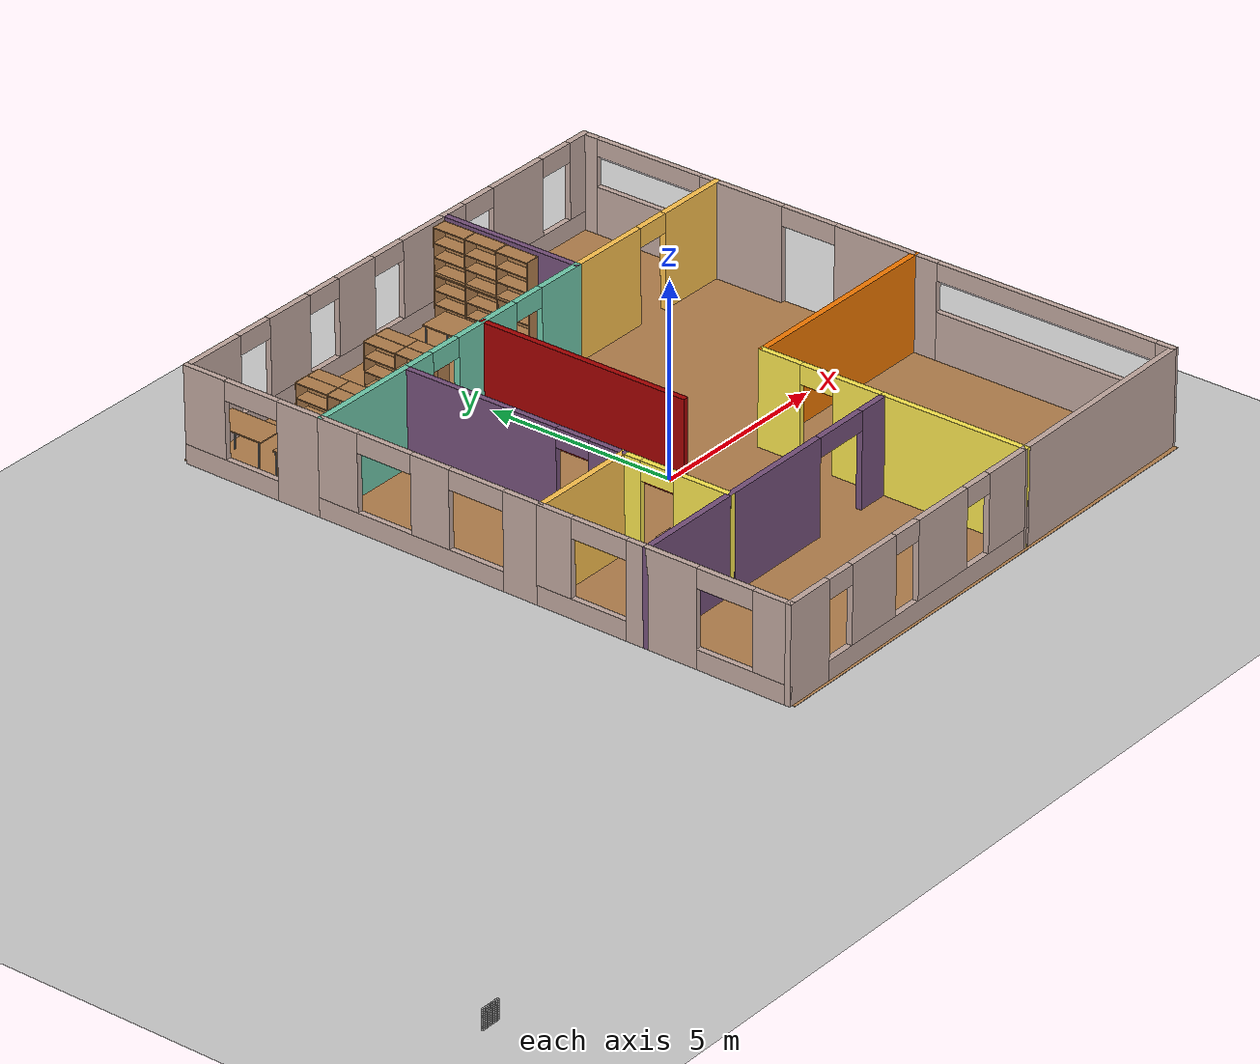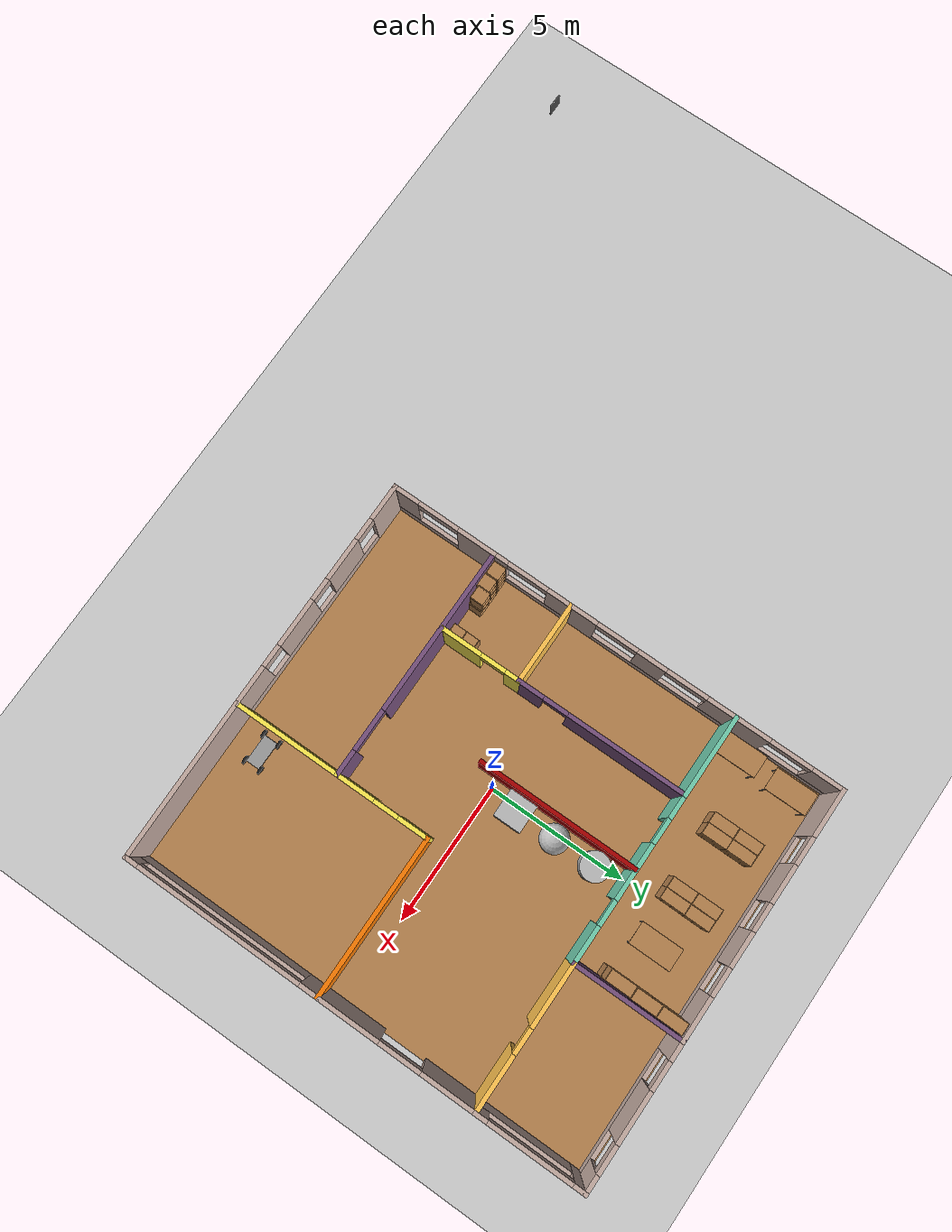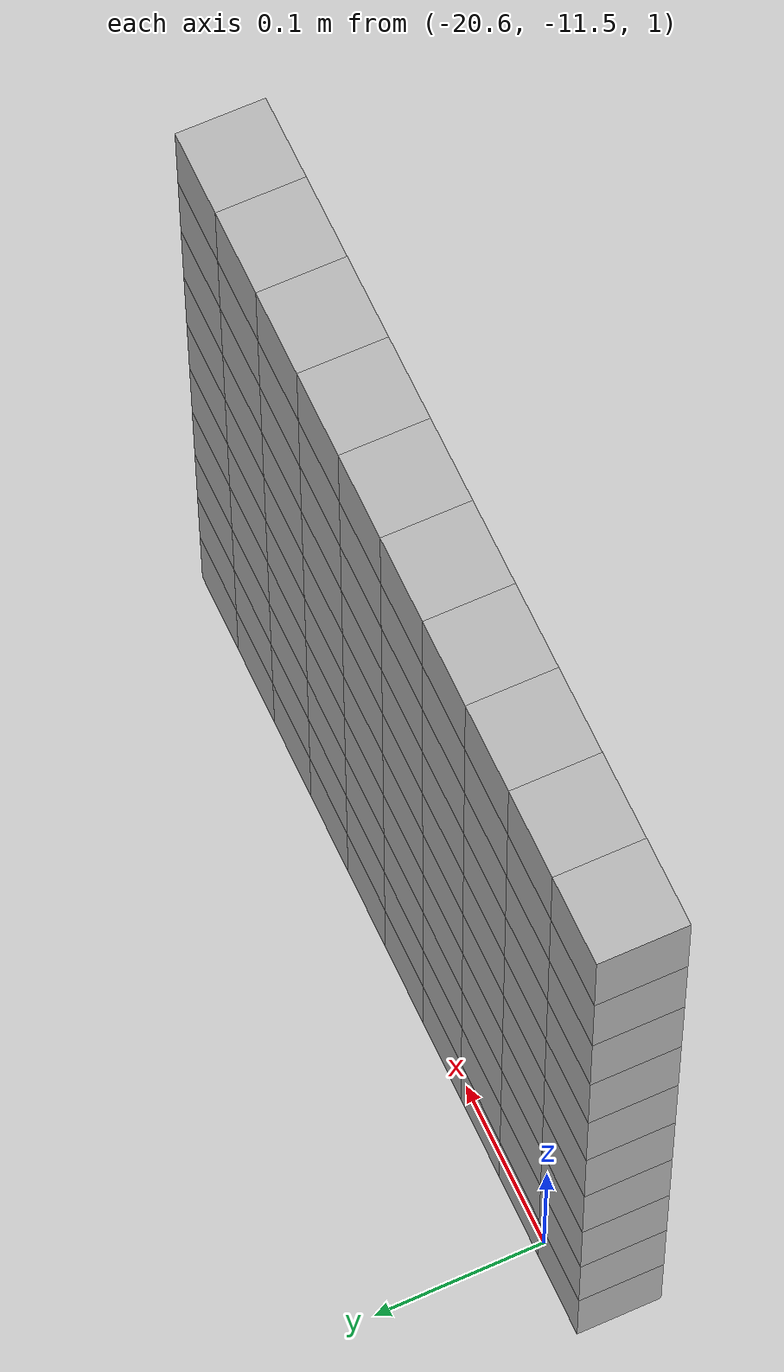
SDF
<sdf version="1.7">
 <world name="default">
  <light name="sun" type="directional">
   <pose>0 0 10 0 -0 0</pose>
   <diffuse>0.8 0.8 0.8 1</diffuse>
   <specular>0.2 0.2 0.2 1</specular>
   <attenuation>
    <range>1000</range>
    <constant>0.9</constant>
    <linear>0.01</linear>
    <quadratic>0.001</quadratic>
   </attenuation>
   <direction>-0.5 0.1 -0.9</direction>
   <spot><inner_angle>0</inner_angle><outer_angle>0</outer_angle><falloff>0</falloff></spot>
  </light>
  <model name="ground_plane">
   <static>1</static>
   <link name="link">
    <collision name="collision">
     <geometry><plane><normal>0 0 1</normal><size>100 100</size></plane></geometry>
     <surface>
      <contact><collide_bitmask>65535</collide_bitmask></contact>
      <friction><ode><mu>100</mu><mu2>50</mu2></ode></friction>
     </surface>
    </collision>
    <visual name="visual">
     <cast_shadows>0</cast_shadows>
     <geometry><plane><normal>0 0 1</normal><size>100 100</size></plane></geometry>
     <material>
      <script><uri>file://media/materials/scripts/gazebo.material</uri><name>Gazebo/Grey</name></script>
     </material>
    </visual>
   </link>
  </model>
  <gravity>0 0 -9.8</gravity>
  <magnetic_field>6e-06 2.3e-05 -4.2e-05</magnetic_field>
  <atmosphere type="adiabatic"/>
  <physics type="ode">
   <max_step_size>0.001</max_step_size>
   <real_time_factor>1</real_time_factor>
   <real_time_update_rate>1000</real_time_update_rate>
  </physics>
  <scene><ambient>0.4 0.4 0.4 1</ambient><background>0.7 0.7 0.7 1</background><shadows>1</shadows></scene>
  <spherical_coordinates>
   <surface_model>EARTH_WGS84</surface_model>
   <latitude_deg>0</latitude_deg>
   <longitude_deg>0</longitude_deg>
   <elevation>0</elevation>
   <heading_deg>0</heading_deg>
  </spherical_coordinates>
  <model name="ground">
   <link name="Wall_2">
    <pose>6.2457 -16.572 0 0 -0 0</pose>
    <inertial>
     <mass>1</mass>
     <inertia><ixx>1</ixx><ixy>0</ixy><ixz>0</ixz><iyy>1</iyy><iyz>0</iyz><izz>1</izz></inertia>
    </inertial>
    <visual name="Wall_2_Visual">
     <pose>0 0 0.005 0 -0 0</pose>
     <geometry><box><size>14 17 0.01</size></box></geometry>
     <material>
      <script><uri>file://media/materials/scripts/gazebo.material</uri><name>Gazebo/Wood</name></script>
      <ambient>0 0 0 1</ambient>
      <shader type="pixel"><normal_map>__default__</normal_map></shader>
      <diffuse>1 1 1 1</diffuse>
      <specular>0.2 0.2 0.2 1</specular>
      <emissive>0 0 0 1</emissive>
     </material>
     <meta><layer>0</layer></meta>
    </visual>
    <collision name="Wall_2_Collision">
     <pose>0 0 0.005 0 -0 0</pose>
     <geometry><box><size>14 17 0.01</size></box></geometry>
     <surface>
      <friction>
       <ode><mu>1</mu><mu2>1</mu2><fdir1>0 0 0</fdir1><slip1>0</slip1><slip2>0</slip2></ode>
       <torsional>
        <coefficient>1</coefficient>
        <patch_radius>0</patch_radius>
        <surface_radius>0</surface_radius>
        <use_patch_radius>1</use_patch_radius>
        <ode><slip>0</slip></ode>
       </torsional>
      </friction>
      <bounce><restitution_coefficient>0</restitution_coefficient><threshold>1e+06</threshold></bounce>
      <contact>
       <collide_without_contact>0</collide_without_contact>
       <collide_without_contact_bitmask>1</collide_without_contact_bitmask>
       <collide_bitmask>1</collide_bitmask>
       <ode>
        <soft_cfm>0</soft_cfm>
        <soft_erp>0.2</soft_erp>
        <kp>1e+13</kp>
        <kd>1</kd>
        <max_vel>0.01</max_vel>
        <min_depth>0</min_depth>
       </ode>
       <bullet>
        <split_impulse>1</split_impulse>
        <split_impulse_penetration_threshold>-0.01</split_impulse_penetration_threshold>
        <soft_cfm>0</soft_cfm>
        <soft_erp>0.2</soft_erp>
        <kp>1e+13</kp>
        <kd>1</kd>
       </bullet>
      </contact>
     </surface>
    </collision>
   </link>
   <static>1</static>
   <pose>-5.17108 17.0771 0 0 -0 0</pose>
  </model>
  <model name="my_build">
   <pose>1.0497 0.473935 0 0 -0 0</pose>
   <link name="Wall_0">
    <collision name="Wall_0_Collision">
     <geometry><box><size>3 0.15 2.5</size></box></geometry>
     <pose>0 0 1.25 0 -0 0</pose>
    </collision>
    <visual name="Wall_0_Visual">
     <pose>0 0 1.25 0 -0 0</pose>
     <geometry><box><size>3 0.15 2.5</size></box></geometry>
     <material>
      <script><uri>file://media/materials/scripts/gazebo.material</uri><name>Gazebo/Grey</name></script>
      <ambient>1 0.764706 0.305882 1</ambient>
     </material>
     <meta><layer>0</layer></meta>
    </visual>
    <pose>-5.54988 -1.62469 0 0 -0 0</pose>
   </link>
   <link name="Wall_1">
    <pose>-4.12488 -3.07619 0 0 -0 -1.5708</pose>
    <visual name="Wall_1_Visual_0">
     <pose>-1.23625 0 1.25 0 -0 0</pose>
     <geometry><box><size>0.580504 0.15 2.5</size></box></geometry>
     <material>
      <script><uri>file://media/materials/scripts/gazebo.material</uri><name>Gazebo/Grey</name></script>
      <ambient>0.988235 0.913725 0.309804 1</ambient>
     </material>
     <meta><layer>0</layer></meta>
    </visual>
    <collision name="Wall_1_Collision_0">
     <geometry><box><size>0.580504 0.15 2.5</size></box></geometry>
     <pose>-1.23625 0 1.25 0 -0 0</pose>
    </collision>
    <visual name="Wall_1_Visual_1">
     <pose>0.740252 0 1.25 0 -0 0</pose>
     <geometry><box><size>1.5725 0.15 2.5</size></box></geometry>
     <material>
      <script><uri>file://media/materials/scripts/gazebo.material</uri><name>Gazebo/Grey</name></script>
      <ambient>0.988235 0.913725 0.309804 1</ambient>
     </material>
     <meta><layer>0</layer></meta>
    </visual>
    <collision name="Wall_1_Collision_1">
     <geometry><box><size>1.5725 0.15 2.5</size></box></geometry>
     <pose>0.740252 0 1.25 0 -0 0</pose>
    </collision>
    <visual name="Wall_1_Visual_2">
     <pose>-0.495996 0 2.25 0 -0 0</pose>
     <geometry><box><size>0.9 0.15 0.5</size></box></geometry>
     <material>
      <script><uri>file://media/materials/scripts/gazebo.material</uri><name>Gazebo/Grey</name></script>
      <ambient>0.988235 0.913725 0.309804 1</ambient>
     </material>
     <meta><layer>0</layer></meta>
    </visual>
    <collision name="Wall_1_Collision_2">
     <geometry><box><size>0.9 0.15 0.5</size></box></geometry>
     <pose>-0.495996 0 2.25 0 -0 0</pose>
    </collision>
   </link>
   <link name="Wall_10">
    <pose>-2.80038 -8.32469 0 0 -0 0</pose>
    <visual name="Wall_10_Visual_0">
     <pose>-3.57259 0 1.25 0 -0 0</pose>
     <geometry><box><size>1.35433 0.15 2.5</size></box></geometry>
     <material>
      <script><uri>file://media/materials/scripts/gazebo.material</uri><name>Gazebo/Grey</name></script>
      <ambient>0.760784 0.662745 0.627451 1</ambient>
     </material>
     <meta><layer>0</layer></meta>
    </visual>
    <collision name="Wall_10_Collision_0">
     <geometry><box><size>1.35433 0.15 2.5</size></box></geometry>
     <pose>-3.57259 0 1.25 0 -0 0</pose>
    </collision>
    <visual name="Wall_10_Visual_1">
     <pose>0.677163 0 0.25 0 -0 0</pose>
     <geometry><box><size>7.14519 0.15 0.5</size></box></geometry>
     <material>
      <script><uri>file://media/materials/scripts/gazebo.material</uri><name>Gazebo/Grey</name></script>
      <ambient>0.760784 0.662745 0.627451 1</ambient>
     </material>
     <meta><layer>0</layer></meta>
    </visual>
    <collision name="Wall_10_Collision_1">
     <geometry><box><size>7.14519 0.15 0.5</size></box></geometry>
     <pose>0.677163 0 0.25 0 -0 0</pose>
    </collision>
    <visual name="Wall_10_Visual_2">
     <pose>-1.32535 0 1.5 0 -0 0</pose>
     <geometry><box><size>1.54015 0.15 2</size></box></geometry>
     <material>
      <script><uri>file://media/materials/scripts/gazebo.material</uri><name>Gazebo/Grey</name></script>
      <ambient>0.760784 0.662745 0.627451 1</ambient>
     </material>
     <meta><layer>0</layer></meta>
    </visual>
    <collision name="Wall_10_Collision_2">
     <geometry><box><size>1.54015 0.15 2</size></box></geometry>
     <pose>-1.32535 0 1.5 0 -0 0</pose>
    </collision>
    <visual name="Wall_10_Visual_3">
     <pose>1.11606 0 1.5 0 -0 0</pose>
     <geometry><box><size>1.74267 0.15 2</size></box></geometry>
     <material>
      <script><uri>file://media/materials/scripts/gazebo.material</uri><name>Gazebo/Grey</name></script>
      <ambient>0.760784 0.662745 0.627451 1</ambient>
     </material>
     <meta><layer>0</layer></meta>
    </visual>
    <collision name="Wall_10_Collision_3">
     <geometry><box><size>1.74267 0.15 2</size></box></geometry>
     <pose>1.11606 0 1.5 0 -0 0</pose>
    </collision>
    <visual name="Wall_10_Visual_4">
     <pose>3.51858 0 1.5 0 -0 0</pose>
     <geometry><box><size>1.46236 0.15 2</size></box></geometry>
     <material>
      <script><uri>file://media/materials/scripts/gazebo.material</uri><name>Gazebo/Grey</name></script>
      <ambient>0.760784 0.662745 0.627451 1</ambient>
     </material>
     <meta><layer>0</layer></meta>
    </visual>
    <collision name="Wall_10_Collision_4">
     <geometry><box><size>1.46236 0.15 2</size></box></geometry>
     <pose>3.51858 0 1.5 0 -0 0</pose>
    </collision>
    <visual name="Wall_10_Visual_5">
     <pose>-2.49543 0 2.25 0 -0 0</pose>
     <geometry><box><size>0.8 0.15 0.5</size></box></geometry>
     <material>
      <script><uri>file://media/materials/scripts/gazebo.material</uri><name>Gazebo/Grey</name></script>
      <ambient>0.760784 0.662745 0.627451 1</ambient>
     </material>
     <meta><layer>0</layer></meta>
    </visual>
    <collision name="Wall_10_Collision_5">
     <geometry><box><size>0.8 0.15 0.5</size></box></geometry>
     <pose>-2.49543 0 2.25 0 -0 0</pose>
    </collision>
    <visual name="Wall_10_Visual_6">
     <pose>-0.155277 0 2.25 0 -0 0</pose>
     <geometry><box><size>0.8 0.15 0.5</size></box></geometry>
     <material>
      <script><uri>file://media/materials/scripts/gazebo.material</uri><name>Gazebo/Grey</name></script>
      <ambient>0.760784 0.662745 0.627451 1</ambient>
     </material>
     <meta><layer>0</layer></meta>
    </visual>
    <collision name="Wall_10_Collision_6">
     <geometry><box><size>0.8 0.15 0.5</size></box></geometry>
     <pose>-0.155277 0 2.25 0 -0 0</pose>
    </collision>
    <visual name="Wall_10_Visual_7">
     <pose>2.3874 0 2.25 0 -0 0</pose>
     <geometry><box><size>0.8 0.15 0.5</size></box></geometry>
     <material>
      <script><uri>file://media/materials/scripts/gazebo.material</uri><name>Gazebo/Grey</name></script>
      <ambient>0.760784 0.662745 0.627451 1</ambient>
     </material>
     <meta><layer>0</layer></meta>
    </visual>
    <collision name="Wall_10_Collision_7">
     <geometry><box><size>0.8 0.15 0.5</size></box></geometry>
     <pose>2.3874 0 2.25 0 -0 0</pose>
    </collision>
   </link>
   <link name="Wall_11">
    <collision name="Wall_11_Collision">
     <geometry><box><size>3.947 0.15 2.5</size></box></geometry>
     <pose>0 0 1.25 0 -0 0</pose>
    </collision>
    <visual name="Wall_11_Visual">
     <pose>0 0 1.25 0 -0 0</pose>
     <geometry><box><size>3.947 0.15 2.5</size></box></geometry>
     <material>
      <script><uri>file://media/materials/scripts/gazebo.material</uri><name>Gazebo/Grey</name></script>
      <ambient>0.988235 0.913725 0.309804 1</ambient>
     </material>
     <meta><layer>0</layer></meta>
    </visual>
    <pose>1.37412 -6.42619 0 0 -0 1.5708</pose>
   </link>
   <link name="Wall_12">
    <pose>-1.37538 -4.52769 0 0 -0 3.14159</pose>
    <visual name="Wall_12_Visual_0">
     <pose>-2.33894 0 1.25 0 -0 0</pose>
     <geometry><box><size>0.971723 0.15 2.5</size></box></geometry>
     <material>
      <script><uri>file://media/materials/scripts/gazebo.material</uri><name>Gazebo/Grey</name></script>
      <ambient>0.458824 0.313726 0.482353 1</ambient>
     </material>
     <meta><layer>0</layer></meta>
    </visual>
    <collision name="Wall_12_Collision_0">
     <geometry><box><size>0.971723 0.15 2.5</size></box></geometry>
     <pose>-2.33894 0 1.25 0 -0 0</pose>
    </collision>
    <visual name="Wall_12_Visual_1">
     <pose>1.23586 0 1.25 0 -0 0</pose>
     <geometry><box><size>3.17787 0.15 2.5</size></box></geometry>
     <material>
      <script><uri>file://media/materials/scripts/gazebo.material</uri><name>Gazebo/Grey</name></script>
      <ambient>0.458824 0.313726 0.482353 1</ambient>
     </material>
     <meta><layer>0</layer></meta>
    </visual>
    <collision name="Wall_12_Collision_1">
     <geometry><box><size>3.17787 0.15 2.5</size></box></geometry>
     <pose>1.23586 0 1.25 0 -0 0</pose>
    </collision>
    <visual name="Wall_12_Visual_2">
     <pose>-1.10308 0 2.25 0 -0 0</pose>
     <geometry><box><size>1.5 0.15 0.5</size></box></geometry>
     <material>
      <script><uri>file://media/materials/scripts/gazebo.material</uri><name>Gazebo/Grey</name></script>
      <ambient>0.458824 0.313726 0.482353 1</ambient>
     </material>
     <meta><layer>0</layer></meta>
    </visual>
    <collision name="Wall_12_Collision_2">
     <geometry><box><size>1.5 0.15 0.5</size></box></geometry>
     <pose>-1.10308 0 2.25 0 -0 0</pose>
    </collision>
   </link>
   <link name="Wall_14">
    <pose>-6.97488 6.40031 0 0 -0 1.5708</pose>
    <visual name="Wall_14_Visual_0">
     <pose>-1.34037 0 1.25 0 -0 0</pose>
     <geometry><box><size>1.31927 0.15 2.5</size></box></geometry>
     <material>
      <script><uri>file://media/materials/scripts/gazebo.material</uri><name>Gazebo/Grey</name></script>
      <ambient>0.760784 0.662745 0.627451 1</ambient>
     </material>
     <meta><layer>0</layer></meta>
    </visual>
    <collision name="Wall_14_Collision_0">
     <geometry><box><size>1.31927 0.15 2.5</size></box></geometry>
     <pose>-1.34037 0 1.25 0 -0 0</pose>
    </collision>
    <visual name="Wall_14_Visual_1">
     <pose>0.659634 0 0.25 0 -0 0</pose>
     <geometry><box><size>2.68073 0.15 0.5</size></box></geometry>
     <material>
      <script><uri>file://media/materials/scripts/gazebo.material</uri><name>Gazebo/Grey</name></script>
      <ambient>0.760784 0.662745 0.627451 1</ambient>
     </material>
     <meta><layer>0</layer></meta>
    </visual>
    <collision name="Wall_14_Collision_1">
     <geometry><box><size>2.68073 0.15 0.5</size></box></geometry>
     <pose>0.659634 0 0.25 0 -0 0</pose>
    </collision>
    <visual name="Wall_14_Visual_2">
     <pose>1.40963 0 1.5 0 -0 0</pose>
     <geometry><box><size>1.18073 0.15 2</size></box></geometry>
     <material>
      <script><uri>file://media/materials/scripts/gazebo.material</uri><name>Gazebo/Grey</name></script>
      <ambient>0.760784 0.662745 0.627451 1</ambient>
     </material>
     <meta><layer>0</layer></meta>
    </visual>
    <collision name="Wall_14_Collision_2">
     <geometry><box><size>1.18073 0.15 2</size></box></geometry>
     <pose>1.40963 0 1.5 0 -0 0</pose>
    </collision>
    <visual name="Wall_14_Visual_3">
     <pose>0.069268 0 2.25 0 -0 0</pose>
     <geometry><box><size>1.5 0.15 0.5</size></box></geometry>
     <material>
      <script><uri>file://media/materials/scripts/gazebo.material</uri><name>Gazebo/Grey</name></script>
      <ambient>0.760784 0.662745 0.627451 1</ambient>
     </material>
     <meta><layer>0</layer></meta>
    </visual>
    <collision name="Wall_14_Collision_3">
     <geometry><box><size>1.5 0.15 0.5</size></box></geometry>
     <pose>0.069268 0 2.25 0 -0 0</pose>
    </collision>
   </link>
   <link name="Wall_15">
    <pose>-2.54988 8.32531 0 0 -0 0</pose>
    <visual name="Wall_15_Visual_0">
     <pose>-3.61615 0 1.25 0 -0 0</pose>
     <geometry><box><size>1.76769 0.15 2.5</size></box></geometry>
     <material>
      <script><uri>file://media/materials/scripts/gazebo.material</uri><name>Gazebo/Grey</name></script>
      <ambient>0.760784 0.662745 0.627451 1</ambient>
     </material>
     <meta><layer>0</layer></meta>
    </visual>
    <collision name="Wall_15_Collision_0">
     <geometry><box><size>1.76769 0.15 2.5</size></box></geometry>
     <pose>-3.61615 0 1.25 0 -0 0</pose>
    </collision>
    <visual name="Wall_15_Visual_1">
     <pose>0.883846 0 0.25 0 -0 0</pose>
     <geometry><box><size>7.23231 0.15 0.5</size></box></geometry>
     <material>
      <script><uri>file://media/materials/scripts/gazebo.material</uri><name>Gazebo/Grey</name></script>
      <ambient>0.760784 0.662745 0.627451 1</ambient>
     </material>
     <meta><layer>0</layer></meta>
    </visual>
    <collision name="Wall_15_Collision_1">
     <geometry><box><size>7.23231 0.15 0.5</size></box></geometry>
     <pose>0.883846 0 0.25 0 -0 0</pose>
    </collision>
    <visual name="Wall_15_Visual_2">
     <pose>-1.04898 0 1.5 0 -0 0</pose>
     <geometry><box><size>1.36665 0.15 2</size></box></geometry>
     <material>
      <script><uri>file://media/materials/scripts/gazebo.material</uri><name>Gazebo/Grey</name></script>
      <ambient>0.760784 0.662745 0.627451 1</ambient>
     </material>
     <meta><layer>0</layer></meta>
    </visual>
    <collision name="Wall_15_Collision_2">
     <geometry><box><size>1.36665 0.15 2</size></box></geometry>
     <pose>-1.04898 0 1.5 0 -0 0</pose>
    </collision>
    <visual name="Wall_15_Visual_3">
     <pose>1.26379 0 1.5 0 -0 0</pose>
     <geometry><box><size>1.25889 0.15 2</size></box></geometry>
     <material>
      <script><uri>file://media/materials/scripts/gazebo.material</uri><name>Gazebo/Grey</name></script>
      <ambient>0.760784 0.662745 0.627451 1</ambient>
     </material>
     <meta><layer>0</layer></meta>
    </visual>
    <collision name="Wall_15_Collision_3">
     <geometry><box><size>1.25889 0.15 2</size></box></geometry>
     <pose>1.26379 0 1.5 0 -0 0</pose>
    </collision>
    <visual name="Wall_15_Visual_4">
     <pose>3.69661 0 1.5 0 -0 0</pose>
     <geometry><box><size>1.60677 0.15 2</size></box></geometry>
     <material>
      <script><uri>file://media/materials/scripts/gazebo.material</uri><name>Gazebo/Grey</name></script>
      <ambient>0.760784 0.662745 0.627451 1</ambient>
     </material>
     <meta><layer>0</layer></meta>
    </visual>
    <collision name="Wall_15_Collision_4">
     <geometry><box><size>1.60677 0.15 2</size></box></geometry>
     <pose>3.69661 0 1.5 0 -0 0</pose>
    </collision>
    <visual name="Wall_15_Visual_5">
     <pose>-2.23231 0 2.25 0 -0 0</pose>
     <geometry><box><size>1 0.15 0.5</size></box></geometry>
     <material>
      <script><uri>file://media/materials/scripts/gazebo.material</uri><name>Gazebo/Grey</name></script>
      <ambient>0.760784 0.662745 0.627451 1</ambient>
     </material>
     <meta><layer>0</layer></meta>
    </visual>
    <collision name="Wall_15_Collision_5">
     <geometry><box><size>1 0.15 0.5</size></box></geometry>
     <pose>-2.23231 0 2.25 0 -0 0</pose>
    </collision>
    <visual name="Wall_15_Visual_6">
     <pose>0.134344 0 2.25 0 -0 0</pose>
     <geometry><box><size>1 0.15 0.5</size></box></geometry>
     <material>
      <script><uri>file://media/materials/scripts/gazebo.material</uri><name>Gazebo/Grey</name></script>
      <ambient>0.760784 0.662745 0.627451 1</ambient>
     </material>
     <meta><layer>0</layer></meta>
    </visual>
    <collision name="Wall_15_Collision_6">
     <geometry><box><size>1 0.15 0.5</size></box></geometry>
     <pose>0.134344 0 2.25 0 -0 0</pose>
    </collision>
    <visual name="Wall_15_Visual_7">
     <pose>2.39323 0 2.25 0 -0 0</pose>
     <geometry><box><size>1 0.15 0.5</size></box></geometry>
     <material>
      <script><uri>file://media/materials/scripts/gazebo.material</uri><name>Gazebo/Grey</name></script>
      <ambient>0.760784 0.662745 0.627451 1</ambient>
     </material>
     <meta><layer>0</layer></meta>
    </visual>
    <collision name="Wall_15_Collision_7">
     <geometry><box><size>1 0.15 0.5</size></box></geometry>
     <pose>2.39323 0 2.25 0 -0 0</pose>
    </collision>
   </link>
   <link name="Wall_16">
    <collision name="Wall_16_Collision">
     <geometry><box><size>4 0.15 2.5</size></box></geometry>
     <pose>0 0 1.25 0 -0 0</pose>
    </collision>
    <visual name="Wall_16_Visual">
     <pose>0 0 1.25 0 -0 0</pose>
     <geometry><box><size>4 0.15 2.5</size></box></geometry>
     <material>
      <script><uri>file://media/materials/scripts/gazebo.material</uri><name>Gazebo/Grey</name></script>
      <ambient>0.458824 0.313726 0.482353 1</ambient>
     </material>
     <meta><layer>0</layer></meta>
    </visual>
    <pose>1.87512 6.40031 0 0 -0 -1.5708</pose>
   </link>
   <link name="Wall_17">
    <pose>-1.12488 4.47531 0 0 -0 3.14159</pose>
    <visual name="Wall_17_Visual_0">
     <pose>-2.37562 0 1.25 0 -0 0</pose>
     <geometry><box><size>1.39876 0.15 2.5</size></box></geometry>
     <material>
      <script><uri>file://media/materials/scripts/gazebo.material</uri><name>Gazebo/Grey</name></script>
      <ambient>0.435294 0.796078 0.67451 1</ambient>
     </material>
     <meta><layer>0</layer></meta>
    </visual>
    <collision name="Wall_17_Collision_0">
     <geometry><box><size>1.39876 0.15 2.5</size></box></geometry>
     <pose>-2.37562 0 1.25 0 -0 0</pose>
    </collision>
    <visual name="Wall_17_Visual_1">
     <pose>0.234108 0 1.25 0 -0 0</pose>
     <geometry><box><size>2.0207 0.15 2.5</size></box></geometry>
     <material>
      <script><uri>file://media/materials/scripts/gazebo.material</uri><name>Gazebo/Grey</name></script>
      <ambient>0.435294 0.796078 0.67451 1</ambient>
     </material>
     <meta><layer>0</layer></meta>
    </visual>
    <collision name="Wall_17_Collision_1">
     <geometry><box><size>2.0207 0.15 2.5</size></box></geometry>
     <pose>0.234108 0 1.25 0 -0 0</pose>
    </collision>
    <visual name="Wall_17_Visual_2">
     <pose>2.60973 0 1.25 0 -0 0</pose>
     <geometry><box><size>0.930542 0.15 2.5</size></box></geometry>
     <material>
      <script><uri>file://media/materials/scripts/gazebo.material</uri><name>Gazebo/Grey</name></script>
      <ambient>0.435294 0.796078 0.67451 1</ambient>
     </material>
     <meta><layer>0</layer></meta>
    </visual>
    <collision name="Wall_17_Collision_2">
     <geometry><box><size>0.930542 0.15 2.5</size></box></geometry>
     <pose>2.60973 0 1.25 0 -0 0</pose>
    </collision>
    <visual name="Wall_17_Visual_3">
     <pose>-1.22624 0 2.25 0 -0 0</pose>
     <geometry><box><size>0.9 0.15 0.5</size></box></geometry>
     <material>
      <script><uri>file://media/materials/scripts/gazebo.material</uri><name>Gazebo/Grey</name></script>
      <ambient>0.435294 0.796078 0.67451 1</ambient>
     </material>
     <meta><layer>0</layer></meta>
    </visual>
    <collision name="Wall_17_Collision_3">
     <geometry><box><size>0.9 0.15 0.5</size></box></geometry>
     <pose>-1.22624 0 2.25 0 -0 0</pose>
    </collision>
    <visual name="Wall_17_Visual_4">
     <pose>1.69446 0 2.25 0 -0 0</pose>
     <geometry><box><size>0.9 0.15 0.5</size></box></geometry>
     <material>
      <script><uri>file://media/materials/scripts/gazebo.material</uri><name>Gazebo/Grey</name></script>
      <ambient>0.435294 0.796078 0.67451 1</ambient>
     </material>
     <meta><layer>0</layer></meta>
    </visual>
    <collision name="Wall_17_Collision_4">
     <geometry><box><size>0.9 0.15 0.5</size></box></geometry>
     <pose>1.69446 0 2.25 0 -0 0</pose>
    </collision>
   </link>
   <link name="Wall_19">
    <pose>4.42512 8.32531 0 0 -0 0</pose>
    <visual name="Wall_19_Visual_0">
     <pose>-2.2474 0 1.25 0 -0 0</pose>
     <geometry><box><size>0.755203 0.15 2.5</size></box></geometry>
     <material>
      <script><uri>file://media/materials/scripts/gazebo.material</uri><name>Gazebo/Grey</name></script>
      <ambient>0.760784 0.662745 0.627451 1</ambient>
     </material>
     <meta><layer>0</layer></meta>
    </visual>
    <collision name="Wall_19_Collision_0">
     <geometry><box><size>0.755203 0.15 2.5</size></box></geometry>
     <pose>-2.2474 0 1.25 0 -0 0</pose>
    </collision>
    <visual name="Wall_19_Visual_1">
     <pose>0.377601 0 0.25 0 -0 0</pose>
     <geometry><box><size>4.4948 0.15 0.5</size></box></geometry>
     <material>
      <script><uri>file://media/materials/scripts/gazebo.material</uri><name>Gazebo/Grey</name></script>
      <ambient>0.760784 0.662745 0.627451 1</ambient>
     </material>
     <meta><layer>0</layer></meta>
    </visual>
    <collision name="Wall_19_Collision_1">
     <geometry><box><size>4.4948 0.15 0.5</size></box></geometry>
     <pose>0.377601 0 0.25 0 -0 0</pose>
    </collision>
    <visual name="Wall_19_Visual_2">
     <pose>0.029706 0 1.5 0 -0 0</pose>
     <geometry><box><size>1.79901 0.15 2</size></box></geometry>
     <material>
      <script><uri>file://media/materials/scripts/gazebo.material</uri><name>Gazebo/Grey</name></script>
      <ambient>0.760784 0.662745 0.627451 1</ambient>
     </material>
     <meta><layer>0</layer></meta>
    </visual>
    <collision name="Wall_19_Collision_2">
     <geometry><box><size>1.79901 0.15 2</size></box></geometry>
     <pose>0.029706 0 1.5 0 -0 0</pose>
    </collision>
    <visual name="Wall_19_Visual_3">
     <pose>2.2771 0 1.5 0 -0 0</pose>
     <geometry><box><size>0.695791 0.15 2</size></box></geometry>
     <material>
      <script><uri>file://media/materials/scripts/gazebo.material</uri><name>Gazebo/Grey</name></script>
      <ambient>0.760784 0.662745 0.627451 1</ambient>
     </material>
     <meta><layer>0</layer></meta>
    </visual>
    <collision name="Wall_19_Collision_3">
     <geometry><box><size>0.695791 0.15 2</size></box></geometry>
     <pose>2.2771 0 1.5 0 -0 0</pose>
    </collision>
    <visual name="Wall_19_Visual_4">
     <pose>-1.3698 0 2.25 0 -0 0</pose>
     <geometry><box><size>1 0.15 0.5</size></box></geometry>
     <material>
      <script><uri>file://media/materials/scripts/gazebo.material</uri><name>Gazebo/Grey</name></script>
      <ambient>0.760784 0.662745 0.627451 1</ambient>
     </material>
     <meta><layer>0</layer></meta>
    </visual>
    <collision name="Wall_19_Collision_4">
     <geometry><box><size>1 0.15 0.5</size></box></geometry>
     <pose>-1.3698 0 2.25 0 -0 0</pose>
    </collision>
    <visual name="Wall_19_Visual_5">
     <pose>1.42921 0 2.25 0 -0 0</pose>
     <geometry><box><size>1 0.15 0.5</size></box></geometry>
     <material>
      <script><uri>file://media/materials/scripts/gazebo.material</uri><name>Gazebo/Grey</name></script>
      <ambient>0.760784 0.662745 0.627451 1</ambient>
     </material>
     <meta><layer>0</layer></meta>
    </visual>
    <collision name="Wall_19_Collision_5">
     <geometry><box><size>1 0.15 0.5</size></box></geometry>
     <pose>1.42921 0 2.25 0 -0 0</pose>
    </collision>
   </link>
   <link name="Wall_2">
    <collision name="Wall_2_Collision">
     <geometry><box><size>3 0.15 2.5</size></box></geometry>
     <pose>0 0 1.25 0 -0 0</pose>
    </collision>
    <visual name="Wall_2_Visual">
     <pose>0 0 1.25 0 -0 0</pose>
     <geometry><box><size>3 0.15 2.5</size></box></geometry>
     <material>
      <script><uri>file://media/materials/scripts/gazebo.material</uri><name>Gazebo/Grey</name></script>
      <ambient>0.458824 0.313726 0.482353 1</ambient>
     </material>
     <meta><layer>0</layer></meta>
    </visual>
    <pose>-5.54988 -4.52769 0 0 -0 3.14159</pose>
   </link>
   <link name="Wall_20">
    <pose>6.97512 6.40031 0 0 -0 -1.5708</pose>
    <visual name="Wall_20_Visual_0">
     <pose>-1.75104 0 1.25 0 -0 0</pose>
     <geometry><box><size>0.497916 0.15 2.5</size></box></geometry>
     <material>
      <script><uri>file://media/materials/scripts/gazebo.material</uri><name>Gazebo/Grey</name></script>
      <ambient>0.760784 0.662745 0.627451 1</ambient>
     </material>
     <meta><layer>0</layer></meta>
    </visual>
    <collision name="Wall_20_Collision_0">
     <geometry><box><size>0.497916 0.15 2.5</size></box></geometry>
     <pose>-1.75104 0 1.25 0 -0 0</pose>
    </collision>
    <visual name="Wall_20_Visual_1">
     <pose>0.248958 0 0.625 0 -0 0</pose>
     <geometry><box><size>3.50208 0.15 1.25</size></box></geometry>
     <material>
      <script><uri>file://media/materials/scripts/gazebo.material</uri><name>Gazebo/Grey</name></script>
      <ambient>0.760784 0.662745 0.627451 1</ambient>
     </material>
     <meta><layer>0</layer></meta>
    </visual>
    <collision name="Wall_20_Collision_1">
     <geometry><box><size>3.50208 0.15 1.25</size></box></geometry>
     <pose>0.248958 0 0.625 0 -0 0</pose>
    </collision>
    <visual name="Wall_20_Visual_2">
     <pose>1.74896 0 1.875 0 -0 0</pose>
     <geometry><box><size>0.502084 0.15 1.25</size></box></geometry>
     <material>
      <script><uri>file://media/materials/scripts/gazebo.material</uri><name>Gazebo/Grey</name></script>
      <ambient>0.760784 0.662745 0.627451 1</ambient>
     </material>
     <meta><layer>0</layer></meta>
    </visual>
    <collision name="Wall_20_Collision_2">
     <geometry><box><size>0.502084 0.15 1.25</size></box></geometry>
     <pose>1.74896 0 1.875 0 -0 0</pose>
    </collision>
    <visual name="Wall_20_Visual_3">
     <pose>-0.002084 0 2.275 0 -0 0</pose>
     <geometry><box><size>3 0.15 0.45</size></box></geometry>
     <material>
      <script><uri>file://media/materials/scripts/gazebo.material</uri><name>Gazebo/Grey</name></script>
      <ambient>0.760784 0.662745 0.627451 1</ambient>
     </material>
     <meta><layer>0</layer></meta>
    </visual>
    <collision name="Wall_20_Collision_3">
     <geometry><box><size>3 0.15 0.45</size></box></geometry>
     <pose>-0.002084 0 2.275 0 -0 0</pose>
    </collision>
   </link>
   <link name="Wall_21">
    <pose>4.42512 4.47531 0 0 -0 3.14159</pose>
    <visual name="Wall_21_Visual_0">
     <pose>-1.60106 0 1.25 0 -0 0</pose>
     <geometry><box><size>2.04788 0.15 2.5</size></box></geometry>
     <material>
      <script><uri>file://media/materials/scripts/gazebo.material</uri><name>Gazebo/Grey</name></script>
      <ambient>1 0.764706 0.305882 1</ambient>
     </material>
     <meta><layer>0</layer></meta>
    </visual>
    <collision name="Wall_21_Collision_0">
     <geometry><box><size>2.04788 0.15 2.5</size></box></geometry>
     <pose>-1.60106 0 1.25 0 -0 0</pose>
    </collision>
    <visual name="Wall_21_Visual_1">
     <pose>1.47394 0 1.25 0 -0 0</pose>
     <geometry><box><size>2.30212 0.15 2.5</size></box></geometry>
     <material>
      <script><uri>file://media/materials/scripts/gazebo.material</uri><name>Gazebo/Grey</name></script>
      <ambient>1 0.764706 0.305882 1</ambient>
     </material>
     <meta><layer>0</layer></meta>
    </visual>
    <collision name="Wall_21_Collision_1">
     <geometry><box><size>2.30212 0.15 2.5</size></box></geometry>
     <pose>1.47394 0 1.25 0 -0 0</pose>
    </collision>
    <visual name="Wall_21_Visual_2">
     <pose>-0.12712 0 2.25 0 -0 0</pose>
     <geometry><box><size>0.9 0.15 0.5</size></box></geometry>
     <material>
      <script><uri>file://media/materials/scripts/gazebo.material</uri><name>Gazebo/Grey</name></script>
      <ambient>1 0.764706 0.305882 1</ambient>
     </material>
     <meta><layer>0</layer></meta>
    </visual>
    <collision name="Wall_21_Collision_2">
     <geometry><box><size>0.9 0.15 0.5</size></box></geometry>
     <pose>-0.12712 0 2.25 0 -0 0</pose>
    </collision>
   </link>
   <link name="Wall_23">
    <pose>1.37412 -2.85269 0 0 -0 1.5708</pose>
    <visual name="Wall_23_Visual_0">
     <pose>-1.03306 0 1.25 0 -0 0</pose>
     <geometry><box><size>1.43387 0.15 2.5</size></box></geometry>
     <material>
      <script><uri>file://media/materials/scripts/gazebo.material</uri><name>Gazebo/Grey</name></script>
      <ambient>0.988235 0.913725 0.309804 1</ambient>
     </material>
     <meta><layer>0</layer></meta>
    </visual>
    <collision name="Wall_23_Collision_0">
     <geometry><box><size>1.43387 0.15 2.5</size></box></geometry>
     <pose>-1.03306 0 1.25 0 -0 0</pose>
    </collision>
    <visual name="Wall_23_Visual_1">
     <pose>1.16694 0 1.25 0 -0 0</pose>
     <geometry><box><size>1.16613 0.15 2.5</size></box></geometry>
     <material>
      <script><uri>file://media/materials/scripts/gazebo.material</uri><name>Gazebo/Grey</name></script>
      <ambient>0.988235 0.913725 0.309804 1</ambient>
     </material>
     <meta><layer>0</layer></meta>
    </visual>
    <collision name="Wall_23_Collision_1">
     <geometry><box><size>1.16613 0.15 2.5</size></box></geometry>
     <pose>1.16694 0 1.25 0 -0 0</pose>
    </collision>
    <visual name="Wall_23_Visual_2">
     <pose>0.133869 0 2.25 0 -0 0</pose>
     <geometry><box><size>0.9 0.15 0.5</size></box></geometry>
     <material>
      <script><uri>file://media/materials/scripts/gazebo.material</uri><name>Gazebo/Grey</name></script>
      <ambient>0.988235 0.913725 0.309804 1</ambient>
     </material>
     <meta><layer>0</layer></meta>
    </visual>
    <collision name="Wall_23_Collision_2">
     <geometry><box><size>0.9 0.15 0.5</size></box></geometry>
     <pose>0.133869 0 2.25 0 -0 0</pose>
    </collision>
   </link>
   <link name="Wall_24">
    <collision name="Wall_24_Collision">
     <geometry><box><size>5.75 0.15 2.5</size></box></geometry>
     <pose>0 0 1.25 0 -0 0</pose>
    </collision>
    <visual name="Wall_24_Visual">
     <pose>0 0 1.25 0 -0 0</pose>
     <geometry><box><size>5.75 0.15 2.5</size></box></geometry>
     <material>
      <script><uri>file://media/materials/scripts/gazebo.material</uri><name>Gazebo/Grey</name></script>
      <ambient>0.960784 0.47451 0 1</ambient>
     </material>
     <meta><layer>0</layer></meta>
    </visual>
    <pose>4.17412 -1.17769 0 0 -0 0</pose>
   </link>
   <link name="Wall_25">
    <pose>6.97412 -4.72769 0 0 -0 -1.5708</pose>
    <visual name="Wall_25_Visual_0">
     <pose>-3.25347 0 1.25 0 -0 0</pose>
     <geometry><box><size>0.743059 0.15 2.5</size></box></geometry>
     <material>
      <script><uri>file://media/materials/scripts/gazebo.material</uri><name>Gazebo/Grey</name></script>
      <ambient>0.760784 0.662745 0.627451 1</ambient>
     </material>
     <meta><layer>0</layer></meta>
    </visual>
    <collision name="Wall_25_Collision_0">
     <geometry><box><size>0.743059 0.15 2.5</size></box></geometry>
     <pose>-3.25347 0 1.25 0 -0 0</pose>
    </collision>
    <visual name="Wall_25_Visual_1">
     <pose>0.37153 0 0.625 0 -0 0</pose>
     <geometry><box><size>6.50694 0.15 1.25</size></box></geometry>
     <material>
      <script><uri>file://media/materials/scripts/gazebo.material</uri><name>Gazebo/Grey</name></script>
      <ambient>0.760784 0.662745 0.627451 1</ambient>
     </material>
     <meta><layer>0</layer></meta>
    </visual>
    <collision name="Wall_25_Collision_1">
     <geometry><box><size>6.50694 0.15 1.25</size></box></geometry>
     <pose>0.37153 0 0.625 0 -0 0</pose>
    </collision>
    <visual name="Wall_25_Visual_2">
     <pose>3.37153 0 1.875 0 -0 0</pose>
     <geometry><box><size>0.506941 0.15 1.25</size></box></geometry>
     <material>
      <script><uri>file://media/materials/scripts/gazebo.material</uri><name>Gazebo/Grey</name></script>
      <ambient>0.760784 0.662745 0.627451 1</ambient>
     </material>
     <meta><layer>0</layer></meta>
    </visual>
    <collision name="Wall_25_Collision_2">
     <geometry><box><size>0.506941 0.15 1.25</size></box></geometry>
     <pose>3.37153 0 1.875 0 -0 0</pose>
    </collision>
    <visual name="Wall_25_Visual_3">
     <pose>0.118059 0 2.275 0 -0 0</pose>
     <geometry><box><size>6 0.15 0.45</size></box></geometry>
     <material>
      <script><uri>file://media/materials/scripts/gazebo.material</uri><name>Gazebo/Grey</name></script>
      <ambient>0.760784 0.662745 0.627451 1</ambient>
     </material>
     <meta><layer>0</layer></meta>
    </visual>
    <collision name="Wall_25_Collision_3">
     <geometry><box><size>6 0.15 0.45</size></box></geometry>
     <pose>0.118059 0 2.275 0 -0 0</pose>
    </collision>
   </link>
   <link name="Wall_26">
    <collision name="Wall_26_Collision">
     <geometry><box><size>5.7502 0.15 2.5</size></box></geometry>
     <pose>0 0 1.25 0 -0 0</pose>
    </collision>
    <visual name="Wall_26_Visual">
     <pose>0 0 1.25 0 -0 0</pose>
     <geometry><box><size>5.7502 0.15 2.5</size></box></geometry>
     <material>
      <script><uri>file://media/materials/scripts/gazebo.material</uri><name>Gazebo/Grey</name></script>
      <ambient>0.760784 0.662745 0.627451 1</ambient>
     </material>
     <meta><layer>0</layer></meta>
    </visual>
    <pose>4.17412 -8.30119 0 0 -0 -3.1332</pose>
   </link>
   <link name="Wall_28">
    <pose>6.97462 1.64881 0 0 -0 -1.57097</pose>
    <visual name="Wall_28_Visual_0">
     <pose>-1.89193 0 1.25 0 -0 0</pose>
     <geometry><box><size>2.01914 0.15 2.5</size></box></geometry>
     <material>
      <script><uri>file://media/materials/scripts/gazebo.material</uri><name>Gazebo/Grey</name></script>
      <ambient>0.760784 0.662745 0.627451 1</ambient>
     </material>
     <meta><layer>0</layer></meta>
    </visual>
    <collision name="Wall_28_Collision_0">
     <geometry><box><size>2.01914 0.15 2.5</size></box></geometry>
     <pose>-1.89193 0 1.25 0 -0 0</pose>
    </collision>
    <visual name="Wall_28_Visual_1">
     <pose>1.75957 0 1.25 0 -0 0</pose>
     <geometry><box><size>2.28386 0.15 2.5</size></box></geometry>
     <material>
      <script><uri>file://media/materials/scripts/gazebo.material</uri><name>Gazebo/Grey</name></script>
      <ambient>0.760784 0.662745 0.627451 1</ambient>
     </material>
     <meta><layer>0</layer></meta>
    </visual>
    <collision name="Wall_28_Collision_1">
     <geometry><box><size>2.28386 0.15 2.5</size></box></geometry>
     <pose>1.75957 0 1.25 0 -0 0</pose>
    </collision>
    <visual name="Wall_28_Visual_2">
     <pose>-0.13236 0 2.25 0 -0 0</pose>
     <geometry><box><size>1.5 0.15 0.5</size></box></geometry>
     <material>
      <script><uri>file://media/materials/scripts/gazebo.material</uri><name>Gazebo/Grey</name></script>
      <ambient>0.760784 0.662745 0.627451 1</ambient>
     </material>
     <meta><layer>0</layer></meta>
    </visual>
    <collision name="Wall_28_Collision_2">
     <geometry><box><size>1.5 0.15 0.5</size></box></geometry>
     <pose>-0.13236 0 2.25 0 -0 0</pose>
    </collision>
   </link>
   <link name="Wall_3">
    <pose>-6.97488 -3.07619 0 0 -0 1.5708</pose>
    <visual name="Wall_3_Visual_0">
     <pose>-1.22389 0 1.25 0 -0 0</pose>
     <geometry><box><size>0.605219 0.15 2.5</size></box></geometry>
     <material>
      <script><uri>file://media/materials/scripts/gazebo.material</uri><name>Gazebo/Grey</name></script>
      <ambient>0.760784 0.662745 0.627451 1</ambient>
     </material>
     <meta><layer>0</layer></meta>
    </visual>
    <collision name="Wall_3_Collision_0">
     <geometry><box><size>0.605219 0.15 2.5</size></box></geometry>
     <pose>-1.22389 0 1.25 0 -0 0</pose>
    </collision>
    <visual name="Wall_3_Visual_1">
     <pose>0.30261 0 0.25 0 -0 0</pose>
     <geometry><box><size>2.44778 0.15 0.5</size></box></geometry>
     <material>
      <script><uri>file://media/materials/scripts/gazebo.material</uri><name>Gazebo/Grey</name></script>
      <ambient>0.760784 0.662745 0.627451 1</ambient>
     </material>
     <meta><layer>0</layer></meta>
    </visual>
    <collision name="Wall_3_Collision_1">
     <geometry><box><size>2.44778 0.15 0.5</size></box></geometry>
     <pose>0.30261 0 0.25 0 -0 0</pose>
    </collision>
    <visual name="Wall_3_Visual_2">
     <pose>1.05261 0 1.5 0 -0 0</pose>
     <geometry><box><size>0.947781 0.15 2</size></box></geometry>
     <material>
      <script><uri>file://media/materials/scripts/gazebo.material</uri><name>Gazebo/Grey</name></script>
      <ambient>0.760784 0.662745 0.627451 1</ambient>
     </material>
     <meta><layer>0</layer></meta>
    </visual>
    <collision name="Wall_3_Collision_2">
     <geometry><box><size>0.947781 0.15 2</size></box></geometry>
     <pose>1.05261 0 1.5 0 -0 0</pose>
    </collision>
    <visual name="Wall_3_Visual_3">
     <pose>-0.171281 0 2.25 0 -0 0</pose>
     <geometry><box><size>1.5 0.15 0.5</size></box></geometry>
     <material>
      <script><uri>file://media/materials/scripts/gazebo.material</uri><name>Gazebo/Grey</name></script>
      <ambient>0.760784 0.662745 0.627451 1</ambient>
     </material>
     <meta><layer>0</layer></meta>
    </visual>
    <collision name="Wall_3_Collision_3">
     <geometry><box><size>1.5 0.15 0.5</size></box></geometry>
     <pose>-0.171281 0 2.25 0 -0 0</pose>
    </collision>
   </link>
   <link name="Wall_32">
    <collision name="Wall_32_Collision">
     <geometry><box><size>5.75 0.15 2.5</size></box></geometry>
     <pose>0 0 1.25 0 -0 0</pose>
    </collision>
    <visual name="Wall_32_Visual">
     <pose>0 0 1.25 0 -0 0</pose>
     <geometry><box><size>5.75 0.15 2.5</size></box></geometry>
     <material>
      <script><uri>file://media/materials/scripts/gazebo.material</uri><name>Gazebo/Grey</name></script>
      <ambient>0.643137 0 0 1</ambient>
     </material>
     <meta><layer>0</layer></meta>
    </visual>
    <pose>-1.43906 1.64205 0 0 -0 -1.5708</pose>
   </link>
   <link name="Wall_5">
    <pose>-6.97488 1.42531 0 0 -0 1.5708</pose>
    <visual name="Wall_5_Visual_0">
     <pose>-2.5905 0 1.25 0 -0 0</pose>
     <geometry><box><size>1.069 0.15 2.5</size></box></geometry>
     <material>
      <script><uri>file://media/materials/scripts/gazebo.material</uri><name>Gazebo/Grey</name></script>
      <ambient>0.760784 0.662745 0.627451 1</ambient>
     </material>
     <meta><layer>0</layer></meta>
    </visual>
    <collision name="Wall_5_Collision_0">
     <geometry><box><size>1.069 0.15 2.5</size></box></geometry>
     <pose>-2.5905 0 1.25 0 -0 0</pose>
    </collision>
    <visual name="Wall_5_Visual_1">
     <pose>0.534501 0 0.25 0 -0 0</pose>
     <geometry><box><size>5.181 0.15 0.5</size></box></geometry>
     <material>
      <script><uri>file://media/materials/scripts/gazebo.material</uri><name>Gazebo/Grey</name></script>
      <ambient>0.760784 0.662745 0.627451 1</ambient>
     </material>
     <meta><layer>0</layer></meta>
    </visual>
    <collision name="Wall_5_Collision_1">
     <geometry><box><size>5.181 0.15 0.5</size></box></geometry>
     <pose>0.534501 0 0.25 0 -0 0</pose>
    </collision>
    <visual name="Wall_5_Visual_2">
     <pose>-0.021208 0 1.5 0 -0 0</pose>
     <geometry><box><size>1.06958 0.15 2</size></box></geometry>
     <material>
      <script><uri>file://media/materials/scripts/gazebo.material</uri><name>Gazebo/Grey</name></script>
      <ambient>0.760784 0.662745 0.627451 1</ambient>
     </material>
     <meta><layer>0</layer></meta>
    </visual>
    <collision name="Wall_5_Collision_2">
     <geometry><box><size>1.06958 0.15 2</size></box></geometry>
     <pose>-0.021208 0 1.5 0 -0 0</pose>
    </collision>
    <visual name="Wall_5_Visual_3">
     <pose>2.56929 0 1.5 0 -0 0</pose>
     <geometry><box><size>1.11142 0.15 2</size></box></geometry>
     <material>
      <script><uri>file://media/materials/scripts/gazebo.material</uri><name>Gazebo/Grey</name></script>
      <ambient>0.760784 0.662745 0.627451 1</ambient>
     </material>
     <meta><layer>0</layer></meta>
    </visual>
    <collision name="Wall_5_Collision_3">
     <geometry><box><size>1.11142 0.15 2</size></box></geometry>
     <pose>2.56929 0 1.5 0 -0 0</pose>
    </collision>
    <visual name="Wall_5_Visual_4">
     <pose>-1.306 0 2.25 0 -0 0</pose>
     <geometry><box><size>1.5 0.15 0.5</size></box></geometry>
     <material>
      <script><uri>file://media/materials/scripts/gazebo.material</uri><name>Gazebo/Grey</name></script>
      <ambient>0.760784 0.662745 0.627451 1</ambient>
     </material>
     <meta><layer>0</layer></meta>
    </visual>
    <collision name="Wall_5_Collision_4">
     <geometry><box><size>1.5 0.15 0.5</size></box></geometry>
     <pose>-1.306 0 2.25 0 -0 0</pose>
    </collision>
    <visual name="Wall_5_Visual_5">
     <pose>1.26358 0 2.25 0 -0 0</pose>
     <geometry><box><size>1.5 0.15 0.5</size></box></geometry>
     <material>
      <script><uri>file://media/materials/scripts/gazebo.material</uri><name>Gazebo/Grey</name></script>
      <ambient>0.760784 0.662745 0.627451 1</ambient>
     </material>
     <meta><layer>0</layer></meta>
    </visual>
    <collision name="Wall_5_Collision_5">
     <geometry><box><size>1.5 0.15 0.5</size></box></geometry>
     <pose>1.26358 0 2.25 0 -0 0</pose>
    </collision>
   </link>
   <link name="Wall_6">
    <collision name="Wall_6_Collision">
     <geometry><box><size>3 0.15 2.5</size></box></geometry>
     <pose>0 0 1.25 0 -0 0</pose>
    </collision>
    <visual name="Wall_6_Visual">
     <pose>0 0 1.25 0 -0 0</pose>
     <geometry><box><size>3 0.15 2.5</size></box></geometry>
     <material>
      <script><uri>file://media/materials/scripts/gazebo.material</uri><name>Gazebo/Grey</name></script>
      <ambient>0.435294 0.796078 0.67451 1</ambient>
     </material>
     <meta><layer>0</layer></meta>
    </visual>
    <pose>-5.54988 4.47531 0 0 -0 0</pose>
   </link>
   <link name="Wall_7">
    <pose>-4.12488 1.42531 0 0 -0 -1.5708</pose>
    <visual name="Wall_7_Visual_0">
     <pose>-0.948043 0 1.25 0 -0 0</pose>
     <geometry><box><size>4.35391 0.15 2.5</size></box></geometry>
     <material>
      <script><uri>file://media/materials/scripts/gazebo.material</uri><name>Gazebo/Grey</name></script>
      <ambient>0.458824 0.313726 0.482353 1</ambient>
     </material>
     <meta><layer>0</layer></meta>
    </visual>
    <collision name="Wall_7_Collision_0">
     <geometry><box><size>4.35391 0.15 2.5</size></box></geometry>
     <pose>-0.948043 0 1.25 0 -0 0</pose>
    </collision>
    <visual name="Wall_7_Visual_1">
     <pose>2.62696 0 1.25 0 -0 0</pose>
     <geometry><box><size>0.996087 0.15 2.5</size></box></geometry>
     <material>
      <script><uri>file://media/materials/scripts/gazebo.material</uri><name>Gazebo/Grey</name></script>
      <ambient>0.458824 0.313726 0.482353 1</ambient>
     </material>
     <meta><layer>0</layer></meta>
    </visual>
    <collision name="Wall_7_Collision_1">
     <geometry><box><size>0.996087 0.15 2.5</size></box></geometry>
     <pose>2.62696 0 1.25 0 -0 0</pose>
    </collision>
    <visual name="Wall_7_Visual_2">
     <pose>1.67891 0 2.25 0 -0 0</pose>
     <geometry><box><size>0.9 0.15 0.5</size></box></geometry>
     <material>
      <script><uri>file://media/materials/scripts/gazebo.material</uri><name>Gazebo/Grey</name></script>
      <ambient>0.458824 0.313726 0.482353 1</ambient>
     </material>
     <meta><layer>0</layer></meta>
    </visual>
    <collision name="Wall_7_Collision_2">
     <geometry><box><size>0.9 0.15 0.5</size></box></geometry>
     <pose>1.67891 0 2.25 0 -0 0</pose>
    </collision>
   </link>
   <link name="Wall_9">
    <pose>-6.97488 -6.42619 0 0 -0 -1.5708</pose>
    <visual name="Wall_9_Visual_0">
     <pose>-1.25198 0 1.25 0 -0 0</pose>
     <geometry><box><size>1.44305 0.15 2.5</size></box></geometry>
     <material>
      <script><uri>file://media/materials/scripts/gazebo.material</uri><name>Gazebo/Grey</name></script>
      <ambient>0.760784 0.662745 0.627451 1</ambient>
     </material>
     <meta><layer>0</layer></meta>
    </visual>
    <collision name="Wall_9_Collision_0">
     <geometry><box><size>1.44305 0.15 2.5</size></box></geometry>
     <pose>-1.25198 0 1.25 0 -0 0</pose>
    </collision>
    <visual name="Wall_9_Visual_1">
     <pose>0.721525 0 0.25 0 -0 0</pose>
     <geometry><box><size>2.50395 0.15 0.5</size></box></geometry>
     <material>
      <script><uri>file://media/materials/scripts/gazebo.material</uri><name>Gazebo/Grey</name></script>
      <ambient>0.760784 0.662745 0.627451 1</ambient>
     </material>
     <meta><layer>0</layer></meta>
    </visual>
    <collision name="Wall_9_Collision_1">
     <geometry><box><size>2.50395 0.15 0.5</size></box></geometry>
     <pose>0.721525 0 0.25 0 -0 0</pose>
    </collision>
    <visual name="Wall_9_Visual_2">
     <pose>1.47152 0 1.5 0 -0 0</pose>
     <geometry><box><size>1.00395 0.15 2</size></box></geometry>
     <material>
      <script><uri>file://media/materials/scripts/gazebo.material</uri><name>Gazebo/Grey</name></script>
      <ambient>0.760784 0.662745 0.627451 1</ambient>
     </material>
     <meta><layer>0</layer></meta>
    </visual>
    <collision name="Wall_9_Collision_2">
     <geometry><box><size>1.00395 0.15 2</size></box></geometry>
     <pose>1.47152 0 1.5 0 -0 0</pose>
    </collision>
    <visual name="Wall_9_Visual_3">
     <pose>0.21955 0 2.25 0 -0 0</pose>
     <geometry><box><size>1.5 0.15 0.5</size></box></geometry>
     <material>
      <script><uri>file://media/materials/scripts/gazebo.material</uri><name>Gazebo/Grey</name></script>
      <ambient>0.760784 0.662745 0.627451 1</ambient>
     </material>
     <meta><layer>0</layer></meta>
    </visual>
    <collision name="Wall_9_Collision_3">
     <geometry><box><size>1.5 0.15 0.5</size></box></geometry>
     <pose>0.21955 0 2.25 0 -0 0</pose>
    </collision>
   </link>
   <static>1</static>
  </model>
  <light name="user_directional_light_2" type="directional">
   <pose>5.46613 -5.52242 1 0 -0 0</pose>
   <diffuse>0.5 0.5 0.5 1</diffuse>
   <specular>0.1 0.1 0.1 1</specular>
   <direction>0.1 0.1 -0.9</direction>
   <attenuation>
    <range>20</range>
    <constant>0.5</constant>
    <linear>0.01</linear>
    <quadratic>0.001</quadratic>
   </attenuation>
  </light>
  <light name="user_directional_light_3" type="directional">
   <pose>-4 -5.52242 1 0 -0 0</pose>
   <diffuse>0.5 0.5 0.5 1</diffuse>
   <specular>0.1 0.1 0.1 1</specular>
   <direction>0.1 0.1 -0.9</direction>
   <attenuation>
    <range>20</range>
    <constant>0.5</constant>
    <linear>0.01</linear>
    <quadratic>0.001</quadratic>
   </attenuation>
  </light>
  <light name="user_directional_light_0" type="directional">
   <pose>-3.89372 6.97303 1 0 -0 0</pose>
   <diffuse>0.5 0.5 0.5 1</diffuse>
   <specular>0.1 0.1 0.1 1</specular>
   <direction>0.1 0.1 -0.9</direction>
   <attenuation>
    <range>20</range>
    <constant>0.5</constant>
    <linear>0.01</linear>
    <quadratic>0.001</quadratic>
   </attenuation>
  </light>
  <light name="user_directional_light_1" type="directional">
   <pose>5.51291 7.11345 1 0 -0 0</pose>
   <diffuse>0.5 0.5 0.5 1</diffuse>
   <specular>0.1 0.1 0.1 1</specular>
   <direction>0.1 0.1 -0.9</direction>
   <attenuation>
    <range>20</range>
    <constant>0.5</constant>
    <linear>0.01</linear>
    <quadratic>0.001</quadratic>
   </attenuation>
  </light>
  <light name="user_directional_light_4" type="directional">
   <pose>0.552178 0.467888 1 0 -0 0</pose>
   <diffuse>0.5 0.5 0.5 1</diffuse>
   <specular>0.1 0.1 0.1 1</specular>
   <direction>0.1 0.1 -0.9</direction>
   <attenuation>
    <range>20</range>
    <constant>0.5</constant>
    <linear>0.01</linear>
    <quadratic>0.001</quadratic>
   </attenuation>
  </light>
  <model name="textured_shapes">
   <pose>0.185477 2.50227 0.51 0 -0 0.000163</pose>
   <link name="box">
    <pose>0 -1.5 0 0 -0 0</pose>
    <collision name="collision"><geometry><box><size>1 1 1</size></box></geometry></collision>
    <visual name="visual">
     <geometry><box><size>1 1 1</size></box></geometry>
     <material>
      <script>
       <uri>model://textured_shapes/materials/scripts</uri>
       <uri>model://textured_shapes/materials/textures</uri>
       <name>TexturedShape/Squares</name>
      </script>
     </material>
    </visual>
    <inertial>
     <inertia><ixx>1</ixx><ixy>0</ixy><ixz>0</ixz><iyy>1</iyy><iyz>0</iyz><izz>1</izz></inertia>
     <mass>1</mass>
    </inertial>
   </link>
   <link name="sphere">
    <collision name="collision"><geometry><sphere><radius>0.5</radius></sphere></geometry></collision>
    <visual name="visual">
     <geometry><sphere><radius>0.5</radius></sphere></geometry>
     <material>
      <script>
       <uri>model://textured_shapes/materials/scripts</uri>
       <uri>model://textured_shapes/materials/textures</uri>
       <name>TexturedShape/Squares</name>
      </script>
     </material>
    </visual>
    <inertial>
     <inertia><ixx>1</ixx><ixy>0</ixy><ixz>0</ixz><iyy>1</iyy><iyz>0</iyz><izz>1</izz></inertia>
     <mass>1</mass>
    </inertial>
   </link>
   <link name="cylinder">
    <pose>0 1.5 0 0 -0 0</pose>
    <collision name="collision">
     <geometry><cylinder><radius>0.5</radius><length>1</length></cylinder></geometry>
    </collision>
    <visual name="visual">
     <geometry><cylinder><radius>0.5</radius><length>1</length></cylinder></geometry>
     <material>
      <script>
       <uri>model://textured_shapes/materials/scripts</uri>
       <uri>model://textured_shapes/materials/textures</uri>
       <name>TexturedShape/Squares</name>
      </script>
     </material>
    </visual>
    <inertial>
     <inertia><ixx>1</ixx><ixy>0</ixy><ixz>0</ixz><iyy>1</iyy><iyz>0</iyz><izz>1</izz></inertia>
     <mass>1</mass>
    </inertial>
   </link>
  </model>
  <model name="table_0">
   <static>1</static>
   <link name="link">
    <collision name="surface">
     <pose>0 0 1 0 -0 0</pose>
     <geometry><box><size>1.5 0.8 0.03</size></box></geometry>
     <surface><friction><ode><mu>0.6</mu><mu2>0.6</mu2></ode></friction></surface>
    </collision>
    <visual name="visual1">
     <pose>0 0 1 0 -0 0</pose>
     <geometry><box><size>1.5 0.8 0.03</size></box></geometry>
     <material>
      <script><uri>file://media/materials/scripts/gazebo.material</uri><name>Gazebo/Wood</name></script>
     </material>
    </visual>
    <collision name="front_left_leg">
     <pose>0.68 0.38 0.5 0 -0 0</pose>
     <geometry><cylinder><radius>0.02</radius><length>1</length></cylinder></geometry>
    </collision>
    <visual name="front_left_leg">
     <pose>0.68 0.38 0.5 0 -0 0</pose>
     <geometry><cylinder><radius>0.02</radius><length>1</length></cylinder></geometry>
     <material>
      <script><uri>file://media/materials/scripts/gazebo.material</uri><name>Gazebo/Grey</name></script>
     </material>
    </visual>
    <collision name="front_right_leg">
     <pose>0.68 -0.38 0.5 0 -0 0</pose>
     <geometry><cylinder><radius>0.02</radius><length>1</length></cylinder></geometry>
    </collision>
    <visual name="front_right_leg">
     <pose>0.68 -0.38 0.5 0 -0 0</pose>
     <geometry><cylinder><radius>0.02</radius><length>1</length></cylinder></geometry>
     <material>
      <script><uri>file://media/materials/scripts/gazebo.material</uri><name>Gazebo/Grey</name></script>
     </material>
    </visual>
    <collision name="back_right_leg">
     <pose>-0.68 -0.38 0.5 0 -0 0</pose>
     <geometry><cylinder><radius>0.02</radius><length>1</length></cylinder></geometry>
    </collision>
    <visual name="back_right_leg">
     <pose>-0.68 -0.38 0.5 0 -0 0</pose>
     <geometry><cylinder><radius>0.02</radius><length>1</length></cylinder></geometry>
     <material>
      <script><uri>file://media/materials/scripts/gazebo.material</uri><name>Gazebo/Grey</name></script>
     </material>
    </visual>
    <collision name="back_left_leg">
     <pose>-0.68 0.38 0.5 0 -0 0</pose>
     <geometry><cylinder><radius>0.02</radius><length>1</length></cylinder></geometry>
    </collision>
    <visual name="back_left_leg">
     <pose>-0.68 0.38 0.5 0 -0 0</pose>
     <geometry><cylinder><radius>0.02</radius><length>1</length></cylinder></geometry>
     <material>
      <script><uri>file://media/materials/scripts/gazebo.material</uri><name>Gazebo/Grey</name></script>
     </material>
    </visual>
   </link>
   <pose>-5.2296 7.75467 0 0 -0 1.5708</pose>
  </model>
  <model name="table_0_clone">
   <static>1</static>
   <link name="link">
    <collision name="surface">
     <pose>0 0 1 0 -0 0</pose>
     <geometry><box><size>1.5 0.8 0.03</size></box></geometry>
     <surface><friction><ode><mu>0.6</mu><mu2>0.6</mu2></ode></friction></surface>
    </collision>
    <visual name="visual1">
     <pose>0 0 1 0 -0 0</pose>
     <geometry><box><size>1.5 0.8 0.03</size></box></geometry>
     <material>
      <script><uri>file://media/materials/scripts/gazebo.material</uri><name>Gazebo/Wood</name></script>
     </material>
    </visual>
    <collision name="front_left_leg">
     <pose>0.68 0.38 0.5 0 -0 0</pose>
     <geometry><cylinder><radius>0.02</radius><length>1</length></cylinder></geometry>
    </collision>
    <visual name="front_left_leg">
     <pose>0.68 0.38 0.5 0 -0 0</pose>
     <geometry><cylinder><radius>0.02</radius><length>1</length></cylinder></geometry>
     <material>
      <script><uri>file://media/materials/scripts/gazebo.material</uri><name>Gazebo/Grey</name></script>
     </material>
    </visual>
    <collision name="front_right_leg">
     <pose>0.68 -0.38 0.5 0 -0 0</pose>
     <geometry><cylinder><radius>0.02</radius><length>1</length></cylinder></geometry>
    </collision>
    <visual name="front_right_leg">
     <pose>0.68 -0.38 0.5 0 -0 0</pose>
     <geometry><cylinder><radius>0.02</radius><length>1</length></cylinder></geometry>
     <material>
      <script><uri>file://media/materials/scripts/gazebo.material</uri><name>Gazebo/Grey</name></script>
     </material>
    </visual>
    <collision name="back_right_leg">
     <pose>-0.68 -0.38 0.5 0 -0 0</pose>
     <geometry><cylinder><radius>0.02</radius><length>1</length></cylinder></geometry>
    </collision>
    <visual name="back_right_leg">
     <pose>-0.68 -0.38 0.5 0 -0 0</pose>
     <geometry><cylinder><radius>0.02</radius><length>1</length></cylinder></geometry>
     <material>
      <script><uri>file://media/materials/scripts/gazebo.material</uri><name>Gazebo/Grey</name></script>
     </material>
    </visual>
    <collision name="back_left_leg">
     <pose>-0.68 0.38 0.5 0 -0 0</pose>
     <geometry><cylinder><radius>0.02</radius><length>1</length></cylinder></geometry>
    </collision>
    <visual name="back_left_leg">
     <pose>-0.68 0.38 0.5 0 -0 0</pose>
     <geometry><cylinder><radius>0.02</radius><length>1</length></cylinder></geometry>
     <material>
      <script><uri>file://media/materials/scripts/gazebo.material</uri><name>Gazebo/Grey</name></script>
     </material>
    </visual>
   </link>
   <pose>-5.32331 5.82081 0 0 -0 1.5708</pose>
  </model>
  <model name="bookshelf">
   <static>1</static>
   <link name="link">
    <inertial><mass>1</mass></inertial>
    <collision name="back">
     <pose>0 0.005 0.6 0 -0 0</pose>
     <geometry><box><size>0.9 0.01 1.2</size></box></geometry>
    </collision>
    <visual name="visual1">
     <pose>0 0.005 0.6 0 -0 0</pose>
     <geometry><box><size>0.9 0.01 1.2</size></box></geometry>
     <material>
      <script><uri>file://media/materials/scripts/gazebo.material</uri><name>Gazebo/Wood</name></script>
     </material>
    </visual>
    <collision name="left_side">
     <pose>0.45 -0.195 0.6 0 -0 0</pose>
     <geometry><box><size>0.02 0.4 1.2</size></box></geometry>
    </collision>
    <visual name="visual2">
     <pose>0.45 -0.195 0.6 0 -0 0</pose>
     <geometry><box><size>0.02 0.4 1.2</size></box></geometry>
     <material>
      <script><uri>file://media/materials/scripts/gazebo.material</uri><name>Gazebo/Wood</name></script>
     </material>
    </visual>
    <collision name="right_side">
     <pose>-0.45 -0.195 0.6 0 -0 0</pose>
     <geometry><box><size>0.02 0.4 1.2</size></box></geometry>
    </collision>
    <visual name="visual3">
     <pose>-0.45 -0.195 0.6 0 -0 0</pose>
     <geometry><box><size>0.02 0.4 1.2</size></box></geometry>
     <material>
      <script><uri>file://media/materials/scripts/gazebo.material</uri><name>Gazebo/Wood</name></script>
     </material>
    </visual>
    <collision name="bottom">
     <pose>0 -0.195 0.03 0 -0 0</pose>
     <geometry><box><size>0.88 0.4 0.06</size></box></geometry>
    </collision>
    <visual name="visual4">
     <pose>0 -0.195 0.03 0 -0 0</pose>
     <geometry><box><size>0.88 0.4 0.06</size></box></geometry>
     <material>
      <script><uri>file://media/materials/scripts/gazebo.material</uri><name>Gazebo/Wood</name></script>
     </material>
    </visual>
    <collision name="top">
     <pose>0 -0.195 1.19 0 -0 0</pose>
     <geometry><box><size>0.88 0.4 0.02</size></box></geometry>
    </collision>
    <visual name="visual5">
     <pose>0 -0.195 1.19 0 -0 0</pose>
     <geometry><box><size>0.88 0.4 0.02</size></box></geometry>
     <material>
      <script><uri>file://media/materials/scripts/gazebo.material</uri><name>Gazebo/Wood</name></script>
     </material>
    </visual>
    <collision name="low_shelf">
     <pose>0 -0.195 0.43 0 -0 0</pose>
     <geometry><box><size>0.88 0.4 0.02</size></box></geometry>
    </collision>
    <visual name="visual6">
     <pose>0 -0.195 0.43 0 -0 0</pose>
     <geometry><box><size>0.88 0.4 0.02</size></box></geometry>
     <material>
      <script><uri>file://media/materials/scripts/gazebo.material</uri><name>Gazebo/Wood</name></script>
     </material>
    </visual>
    <collision name="high_shelf">
     <pose>0 -0.195 0.8 0 -0 0</pose>
     <geometry><box><size>0.88 0.4 0.02</size></box></geometry>
    </collision>
    <visual name="visual7">
     <pose>0 -0.195 0.8 0 -0 0</pose>
     <geometry><box><size>0.88 0.4 0.02</size></box></geometry>
     <material>
      <script><uri>file://media/materials/scripts/gazebo.material</uri><name>Gazebo/Wood</name></script>
     </material>
    </visual>
   </link>
   <pose>2.81633 8.2449 0 0 0 -1.5708</pose>
  </model>
  <model name="bookshelf_clone">
   <static>1</static>
   <link name="link">
    <inertial><mass>1</mass></inertial>
    <collision name="back">
     <pose>0 0.005 0.6 0 -0 0</pose>
     <geometry><box><size>0.9 0.01 1.2</size></box></geometry>
    </collision>
    <visual name="visual1">
     <pose>0 0.005 0.6 0 -0 0</pose>
     <geometry><box><size>0.9 0.01 1.2</size></box></geometry>
     <material>
      <script><uri>file://media/materials/scripts/gazebo.material</uri><name>Gazebo/Wood</name></script>
     </material>
    </visual>
    <collision name="left_side">
     <pose>0.45 -0.195 0.6 0 -0 0</pose>
     <geometry><box><size>0.02 0.4 1.2</size></box></geometry>
    </collision>
    <visual name="visual2">
     <pose>0.45 -0.195 0.6 0 -0 0</pose>
     <geometry><box><size>0.02 0.4 1.2</size></box></geometry>
     <material>
      <script><uri>file://media/materials/scripts/gazebo.material</uri><name>Gazebo/Wood</name></script>
     </material>
    </visual>
    <collision name="right_side">
     <pose>-0.45 -0.195 0.6 0 -0 0</pose>
     <geometry><box><size>0.02 0.4 1.2</size></box></geometry>
    </collision>
    <visual name="visual3">
     <pose>-0.45 -0.195 0.6 0 -0 0</pose>
     <geometry><box><size>0.02 0.4 1.2</size></box></geometry>
     <material>
      <script><uri>file://media/materials/scripts/gazebo.material</uri><name>Gazebo/Wood</name></script>
     </material>
    </visual>
    <collision name="bottom">
     <pose>0 -0.195 0.03 0 -0 0</pose>
     <geometry><box><size>0.88 0.4 0.06</size></box></geometry>
    </collision>
    <visual name="visual4">
     <pose>0 -0.195 0.03 0 -0 0</pose>
     <geometry><box><size>0.88 0.4 0.06</size></box></geometry>
     <material>
      <script><uri>file://media/materials/scripts/gazebo.material</uri><name>Gazebo/Wood</name></script>
     </material>
    </visual>
    <collision name="top">
     <pose>0 -0.195 1.19 0 -0 0</pose>
     <geometry><box><size>0.88 0.4 0.02</size></box></geometry>
    </collision>
    <visual name="visual5">
     <pose>0 -0.195 1.19 0 -0 0</pose>
     <geometry><box><size>0.88 0.4 0.02</size></box></geometry>
     <material>
      <script><uri>file://media/materials/scripts/gazebo.material</uri><name>Gazebo/Wood</name></script>
     </material>
    </visual>
    <collision name="low_shelf">
     <pose>0 -0.195 0.43 0 -0 0</pose>
     <geometry><box><size>0.88 0.4 0.02</size></box></geometry>
    </collision>
    <visual name="visual6">
     <pose>0 -0.195 0.43 0 -0 0</pose>
     <geometry><box><size>0.88 0.4 0.02</size></box></geometry>
     <material>
      <script><uri>file://media/materials/scripts/gazebo.material</uri><name>Gazebo/Wood</name></script>
     </material>
    </visual>
    <collision name="high_shelf">
     <pose>0 -0.195 0.8 0 -0 0</pose>
     <geometry><box><size>0.88 0.4 0.02</size></box></geometry>
    </collision>
    <visual name="visual7">
     <pose>0 -0.195 0.8 0 -0 0</pose>
     <geometry><box><size>0.88 0.4 0.02</size></box></geometry>
     <material>
      <script><uri>file://media/materials/scripts/gazebo.material</uri><name>Gazebo/Wood</name></script>
     </material>
    </visual>
   </link>
   <pose>2.81395 7.31893 0 0 0 -1.5708</pose>
  </model>
  <model name="bookshelf_clone_0">
   <static>1</static>
   <link name="link">
    <inertial><mass>1</mass></inertial>
    <collision name="back">
     <pose>0 0.005 0.6 0 -0 0</pose>
     <geometry><box><size>0.9 0.01 1.2</size></box></geometry>
    </collision>
    <visual name="visual1">
     <pose>0 0.005 0.6 0 -0 0</pose>
     <geometry><box><size>0.9 0.01 1.2</size></box></geometry>
     <material>
      <script><uri>file://media/materials/scripts/gazebo.material</uri><name>Gazebo/Wood</name></script>
     </material>
    </visual>
    <collision name="left_side">
     <pose>0.45 -0.195 0.6 0 -0 0</pose>
     <geometry><box><size>0.02 0.4 1.2</size></box></geometry>
    </collision>
    <visual name="visual2">
     <pose>0.45 -0.195 0.6 0 -0 0</pose>
     <geometry><box><size>0.02 0.4 1.2</size></box></geometry>
     <material>
      <script><uri>file://media/materials/scripts/gazebo.material</uri><name>Gazebo/Wood</name></script>
     </material>
    </visual>
    <collision name="right_side">
     <pose>-0.45 -0.195 0.6 0 -0 0</pose>
     <geometry><box><size>0.02 0.4 1.2</size></box></geometry>
    </collision>
    <visual name="visual3">
     <pose>-0.45 -0.195 0.6 0 -0 0</pose>
     <geometry><box><size>0.02 0.4 1.2</size></box></geometry>
     <material>
      <script><uri>file://media/materials/scripts/gazebo.material</uri><name>Gazebo/Wood</name></script>
     </material>
    </visual>
    <collision name="bottom">
     <pose>0 -0.195 0.03 0 -0 0</pose>
     <geometry><box><size>0.88 0.4 0.06</size></box></geometry>
    </collision>
    <visual name="visual4">
     <pose>0 -0.195 0.03 0 -0 0</pose>
     <geometry><box><size>0.88 0.4 0.06</size></box></geometry>
     <material>
      <script><uri>file://media/materials/scripts/gazebo.material</uri><name>Gazebo/Wood</name></script>
     </material>
    </visual>
    <collision name="top">
     <pose>0 -0.195 1.19 0 -0 0</pose>
     <geometry><box><size>0.88 0.4 0.02</size></box></geometry>
    </collision>
    <visual name="visual5">
     <pose>0 -0.195 1.19 0 -0 0</pose>
     <geometry><box><size>0.88 0.4 0.02</size></box></geometry>
     <material>
      <script><uri>file://media/materials/scripts/gazebo.material</uri><name>Gazebo/Wood</name></script>
     </material>
    </visual>
    <collision name="low_shelf">
     <pose>0 -0.195 0.43 0 -0 0</pose>
     <geometry><box><size>0.88 0.4 0.02</size></box></geometry>
    </collision>
    <visual name="visual6">
     <pose>0 -0.195 0.43 0 -0 0</pose>
     <geometry><box><size>0.88 0.4 0.02</size></box></geometry>
     <material>
      <script><uri>file://media/materials/scripts/gazebo.material</uri><name>Gazebo/Wood</name></script>
     </material>
    </visual>
    <collision name="high_shelf">
     <pose>0 -0.195 0.8 0 -0 0</pose>
     <geometry><box><size>0.88 0.4 0.02</size></box></geometry>
    </collision>
    <visual name="visual7">
     <pose>0 -0.195 0.8 0 -0 0</pose>
     <geometry><box><size>0.88 0.4 0.02</size></box></geometry>
     <material>
      <script><uri>file://media/materials/scripts/gazebo.material</uri><name>Gazebo/Wood</name></script>
     </material>
    </visual>
   </link>
   <pose>2.82717 6.39672 0 0 0 -1.5708</pose>
  </model>
  <model name="bookshelf_clone_1">
   <static>1</static>
   <link name="link">
    <inertial><mass>1</mass></inertial>
    <collision name="back">
     <pose>0 0.005 0.6 0 -0 0</pose>
     <geometry><box><size>0.9 0.01 1.2</size></box></geometry>
    </collision>
    <visual name="visual1">
     <pose>0 0.005 0.6 0 -0 0</pose>
     <geometry><box><size>0.9 0.01 1.2</size></box></geometry>
     <material>
      <script><uri>file://media/materials/scripts/gazebo.material</uri><name>Gazebo/Wood</name></script>
     </material>
    </visual>
    <collision name="left_side">
     <pose>0.45 -0.195 0.6 0 -0 0</pose>
     <geometry><box><size>0.02 0.4 1.2</size></box></geometry>
    </collision>
    <visual name="visual2">
     <pose>0.45 -0.195 0.6 0 -0 0</pose>
     <geometry><box><size>0.02 0.4 1.2</size></box></geometry>
     <material>
      <script><uri>file://media/materials/scripts/gazebo.material</uri><name>Gazebo/Wood</name></script>
     </material>
    </visual>
    <collision name="right_side">
     <pose>-0.45 -0.195 0.6 0 -0 0</pose>
     <geometry><box><size>0.02 0.4 1.2</size></box></geometry>
    </collision>
    <visual name="visual3">
     <pose>-0.45 -0.195 0.6 0 -0 0</pose>
     <geometry><box><size>0.02 0.4 1.2</size></box></geometry>
     <material>
      <script><uri>file://media/materials/scripts/gazebo.material</uri><name>Gazebo/Wood</name></script>
     </material>
    </visual>
    <collision name="bottom">
     <pose>0 -0.195 0.03 0 -0 0</pose>
     <geometry><box><size>0.88 0.4 0.06</size></box></geometry>
    </collision>
    <visual name="visual4">
     <pose>0 -0.195 0.03 0 -0 0</pose>
     <geometry><box><size>0.88 0.4 0.06</size></box></geometry>
     <material>
      <script><uri>file://media/materials/scripts/gazebo.material</uri><name>Gazebo/Wood</name></script>
     </material>
    </visual>
    <collision name="top">
     <pose>0 -0.195 1.19 0 -0 0</pose>
     <geometry><box><size>0.88 0.4 0.02</size></box></geometry>
    </collision>
    <visual name="visual5">
     <pose>0 -0.195 1.19 0 -0 0</pose>
     <geometry><box><size>0.88 0.4 0.02</size></box></geometry>
     <material>
      <script><uri>file://media/materials/scripts/gazebo.material</uri><name>Gazebo/Wood</name></script>
     </material>
    </visual>
    <collision name="low_shelf">
     <pose>0 -0.195 0.43 0 -0 0</pose>
     <geometry><box><size>0.88 0.4 0.02</size></box></geometry>
    </collision>
    <visual name="visual6">
     <pose>0 -0.195 0.43 0 -0 0</pose>
     <geometry><box><size>0.88 0.4 0.02</size></box></geometry>
     <material>
      <script><uri>file://media/materials/scripts/gazebo.material</uri><name>Gazebo/Wood</name></script>
     </material>
    </visual>
    <collision name="high_shelf">
     <pose>0 -0.195 0.8 0 -0 0</pose>
     <geometry><box><size>0.88 0.4 0.02</size></box></geometry>
    </collision>
    <visual name="visual7">
     <pose>0 -0.195 0.8 0 -0 0</pose>
     <geometry><box><size>0.88 0.4 0.02</size></box></geometry>
     <material>
      <script><uri>file://media/materials/scripts/gazebo.material</uri><name>Gazebo/Wood</name></script>
     </material>
    </visual>
   </link>
   <pose>-0.570351 7.49958 0 0 0 -1.5708</pose>
  </model>
  <model name="bookshelf_clone_2">
   <static>1</static>
   <link name="link">
    <inertial><mass>1</mass></inertial>
    <collision name="back">
     <pose>0 0.005 0.6 0 -0 0</pose>
     <geometry><box><size>0.9 0.01 1.2</size></box></geometry>
    </collision>
    <visual name="visual1">
     <pose>0 0.005 0.6 0 -0 0</pose>
     <geometry><box><size>0.9 0.01 1.2</size></box></geometry>
     <material>
      <script><uri>file://media/materials/scripts/gazebo.material</uri><name>Gazebo/Wood</name></script>
     </material>
    </visual>
    <collision name="left_side">
     <pose>0.45 -0.195 0.6 0 -0 0</pose>
     <geometry><box><size>0.02 0.4 1.2</size></box></geometry>
    </collision>
    <visual name="visual2">
     <pose>0.45 -0.195 0.6 0 -0 0</pose>
     <geometry><box><size>0.02 0.4 1.2</size></box></geometry>
     <material>
      <script><uri>file://media/materials/scripts/gazebo.material</uri><name>Gazebo/Wood</name></script>
     </material>
    </visual>
    <collision name="right_side">
     <pose>-0.45 -0.195 0.6 0 -0 0</pose>
     <geometry><box><size>0.02 0.4 1.2</size></box></geometry>
    </collision>
    <visual name="visual3">
     <pose>-0.45 -0.195 0.6 0 -0 0</pose>
     <geometry><box><size>0.02 0.4 1.2</size></box></geometry>
     <material>
      <script><uri>file://media/materials/scripts/gazebo.material</uri><name>Gazebo/Wood</name></script>
     </material>
    </visual>
    <collision name="bottom">
     <pose>0 -0.195 0.03 0 -0 0</pose>
     <geometry><box><size>0.88 0.4 0.06</size></box></geometry>
    </collision>
    <visual name="visual4">
     <pose>0 -0.195 0.03 0 -0 0</pose>
     <geometry><box><size>0.88 0.4 0.06</size></box></geometry>
     <material>
      <script><uri>file://media/materials/scripts/gazebo.material</uri><name>Gazebo/Wood</name></script>
     </material>
    </visual>
    <collision name="top">
     <pose>0 -0.195 1.19 0 -0 0</pose>
     <geometry><box><size>0.88 0.4 0.02</size></box></geometry>
    </collision>
    <visual name="visual5">
     <pose>0 -0.195 1.19 0 -0 0</pose>
     <geometry><box><size>0.88 0.4 0.02</size></box></geometry>
     <material>
      <script><uri>file://media/materials/scripts/gazebo.material</uri><name>Gazebo/Wood</name></script>
     </material>
    </visual>
    <collision name="low_shelf">
     <pose>0 -0.195 0.43 0 -0 0</pose>
     <geometry><box><size>0.88 0.4 0.02</size></box></geometry>
    </collision>
    <visual name="visual6">
     <pose>0 -0.195 0.43 0 -0 0</pose>
     <geometry><box><size>0.88 0.4 0.02</size></box></geometry>
     <material>
      <script><uri>file://media/materials/scripts/gazebo.material</uri><name>Gazebo/Wood</name></script>
     </material>
    </visual>
    <collision name="high_shelf">
     <pose>0 -0.195 0.8 0 -0 0</pose>
     <geometry><box><size>0.88 0.4 0.02</size></box></geometry>
    </collision>
    <visual name="visual7">
     <pose>0 -0.195 0.8 0 -0 0</pose>
     <geometry><box><size>0.88 0.4 0.02</size></box></geometry>
     <material>
      <script><uri>file://media/materials/scripts/gazebo.material</uri><name>Gazebo/Wood</name></script>
     </material>
    </visual>
   </link>
   <pose>-0.563736 6.59398 0 0 0 -1.5708</pose>
  </model>
  <model name="bookshelf_clone_3">
   <static>1</static>
   <link name="link">
    <inertial><mass>1</mass></inertial>
    <collision name="back">
     <pose>0 0.005 0.6 0 -0 0</pose>
     <geometry><box><size>0.9 0.01 1.2</size></box></geometry>
    </collision>
    <visual name="visual1">
     <pose>0 0.005 0.6 0 -0 0</pose>
     <geometry><box><size>0.9 0.01 1.2</size></box></geometry>
     <material>
      <script><uri>file://media/materials/scripts/gazebo.material</uri><name>Gazebo/Wood</name></script>
     </material>
    </visual>
    <collision name="left_side">
     <pose>0.45 -0.195 0.6 0 -0 0</pose>
     <geometry><box><size>0.02 0.4 1.2</size></box></geometry>
    </collision>
    <visual name="visual2">
     <pose>0.45 -0.195 0.6 0 -0 0</pose>
     <geometry><box><size>0.02 0.4 1.2</size></box></geometry>
     <material>
      <script><uri>file://media/materials/scripts/gazebo.material</uri><name>Gazebo/Wood</name></script>
     </material>
    </visual>
    <collision name="right_side">
     <pose>-0.45 -0.195 0.6 0 -0 0</pose>
     <geometry><box><size>0.02 0.4 1.2</size></box></geometry>
    </collision>
    <visual name="visual3">
     <pose>-0.45 -0.195 0.6 0 -0 0</pose>
     <geometry><box><size>0.02 0.4 1.2</size></box></geometry>
     <material>
      <script><uri>file://media/materials/scripts/gazebo.material</uri><name>Gazebo/Wood</name></script>
     </material>
    </visual>
    <collision name="bottom">
     <pose>0 -0.195 0.03 0 -0 0</pose>
     <geometry><box><size>0.88 0.4 0.06</size></box></geometry>
    </collision>
    <visual name="visual4">
     <pose>0 -0.195 0.03 0 -0 0</pose>
     <geometry><box><size>0.88 0.4 0.06</size></box></geometry>
     <material>
      <script><uri>file://media/materials/scripts/gazebo.material</uri><name>Gazebo/Wood</name></script>
     </material>
    </visual>
    <collision name="top">
     <pose>0 -0.195 1.19 0 -0 0</pose>
     <geometry><box><size>0.88 0.4 0.02</size></box></geometry>
    </collision>
    <visual name="visual5">
     <pose>0 -0.195 1.19 0 -0 0</pose>
     <geometry><box><size>0.88 0.4 0.02</size></box></geometry>
     <material>
      <script><uri>file://media/materials/scripts/gazebo.material</uri><name>Gazebo/Wood</name></script>
     </material>
    </visual>
    <collision name="low_shelf">
     <pose>0 -0.195 0.43 0 -0 0</pose>
     <geometry><box><size>0.88 0.4 0.02</size></box></geometry>
    </collision>
    <visual name="visual6">
     <pose>0 -0.195 0.43 0 -0 0</pose>
     <geometry><box><size>0.88 0.4 0.02</size></box></geometry>
     <material>
      <script><uri>file://media/materials/scripts/gazebo.material</uri><name>Gazebo/Wood</name></script>
     </material>
    </visual>
    <collision name="high_shelf">
     <pose>0 -0.195 0.8 0 -0 0</pose>
     <geometry><box><size>0.88 0.4 0.02</size></box></geometry>
    </collision>
    <visual name="visual7">
     <pose>0 -0.195 0.8 0 -0 0</pose>
     <geometry><box><size>0.88 0.4 0.02</size></box></geometry>
     <material>
      <script><uri>file://media/materials/scripts/gazebo.material</uri><name>Gazebo/Wood</name></script>
     </material>
    </visual>
   </link>
   <pose>-2.94499 7.48329 0 0 0 -1.5708</pose>
  </model>
  <model name="bookshelf_clone_4">
   <static>1</static>
   <link name="link">
    <inertial><mass>1</mass></inertial>
    <collision name="back">
     <pose>0 0.005 0.6 0 -0 0</pose>
     <geometry><box><size>0.9 0.01 1.2</size></box></geometry>
    </collision>
    <visual name="visual1">
     <pose>0 0.005 0.6 0 -0 0</pose>
     <geometry><box><size>0.9 0.01 1.2</size></box></geometry>
     <material>
      <script><uri>file://media/materials/scripts/gazebo.material</uri><name>Gazebo/Wood</name></script>
     </material>
    </visual>
    <collision name="left_side">
     <pose>0.45 -0.195 0.6 0 -0 0</pose>
     <geometry><box><size>0.02 0.4 1.2</size></box></geometry>
    </collision>
    <visual name="visual2">
     <pose>0.45 -0.195 0.6 0 -0 0</pose>
     <geometry><box><size>0.02 0.4 1.2</size></box></geometry>
     <material>
      <script><uri>file://media/materials/scripts/gazebo.material</uri><name>Gazebo/Wood</name></script>
     </material>
    </visual>
    <collision name="right_side">
     <pose>-0.45 -0.195 0.6 0 -0 0</pose>
     <geometry><box><size>0.02 0.4 1.2</size></box></geometry>
    </collision>
    <visual name="visual3">
     <pose>-0.45 -0.195 0.6 0 -0 0</pose>
     <geometry><box><size>0.02 0.4 1.2</size></box></geometry>
     <material>
      <script><uri>file://media/materials/scripts/gazebo.material</uri><name>Gazebo/Wood</name></script>
     </material>
    </visual>
    <collision name="bottom">
     <pose>0 -0.195 0.03 0 -0 0</pose>
     <geometry><box><size>0.88 0.4 0.06</size></box></geometry>
    </collision>
    <visual name="visual4">
     <pose>0 -0.195 0.03 0 -0 0</pose>
     <geometry><box><size>0.88 0.4 0.06</size></box></geometry>
     <material>
      <script><uri>file://media/materials/scripts/gazebo.material</uri><name>Gazebo/Wood</name></script>
     </material>
    </visual>
    <collision name="top">
     <pose>0 -0.195 1.19 0 -0 0</pose>
     <geometry><box><size>0.88 0.4 0.02</size></box></geometry>
    </collision>
    <visual name="visual5">
     <pose>0 -0.195 1.19 0 -0 0</pose>
     <geometry><box><size>0.88 0.4 0.02</size></box></geometry>
     <material>
      <script><uri>file://media/materials/scripts/gazebo.material</uri><name>Gazebo/Wood</name></script>
     </material>
    </visual>
    <collision name="low_shelf">
     <pose>0 -0.195 0.43 0 -0 0</pose>
     <geometry><box><size>0.88 0.4 0.02</size></box></geometry>
    </collision>
    <visual name="visual6">
     <pose>0 -0.195 0.43 0 -0 0</pose>
     <geometry><box><size>0.88 0.4 0.02</size></box></geometry>
     <material>
      <script><uri>file://media/materials/scripts/gazebo.material</uri><name>Gazebo/Wood</name></script>
     </material>
    </visual>
    <collision name="high_shelf">
     <pose>0 -0.195 0.8 0 -0 0</pose>
     <geometry><box><size>0.88 0.4 0.02</size></box></geometry>
    </collision>
    <visual name="visual7">
     <pose>0 -0.195 0.8 0 -0 0</pose>
     <geometry><box><size>0.88 0.4 0.02</size></box></geometry>
     <material>
      <script><uri>file://media/materials/scripts/gazebo.material</uri><name>Gazebo/Wood</name></script>
     </material>
    </visual>
   </link>
   <pose>-2.94936 6.5693 0 0 0 -1.5708</pose>
  </model>
  <model name="bookshelf_clone_3_clone">
   <static>1</static>
   <link name="link">
    <inertial><mass>1</mass></inertial>
    <collision name="back">
     <pose>0 0.005 0.6 0 -0 0</pose>
     <geometry><box><size>0.9 0.01 1.2</size></box></geometry>
    </collision>
    <visual name="visual1">
     <pose>0 0.005 0.6 0 -0 0</pose>
     <geometry><box><size>0.9 0.01 1.2</size></box></geometry>
     <material>
      <script><uri>file://media/materials/scripts/gazebo.material</uri><name>Gazebo/Wood</name></script>
     </material>
    </visual>
    <collision name="left_side">
     <pose>0.45 -0.195 0.6 0 -0 0</pose>
     <geometry><box><size>0.02 0.4 1.2</size></box></geometry>
    </collision>
    <visual name="visual2">
     <pose>0.45 -0.195 0.6 0 -0 0</pose>
     <geometry><box><size>0.02 0.4 1.2</size></box></geometry>
     <material>
      <script><uri>file://media/materials/scripts/gazebo.material</uri><name>Gazebo/Wood</name></script>
     </material>
    </visual>
    <collision name="right_side">
     <pose>-0.45 -0.195 0.6 0 -0 0</pose>
     <geometry><box><size>0.02 0.4 1.2</size></box></geometry>
    </collision>
    <visual name="visual3">
     <pose>-0.45 -0.195 0.6 0 -0 0</pose>
     <geometry><box><size>0.02 0.4 1.2</size></box></geometry>
     <material>
      <script><uri>file://media/materials/scripts/gazebo.material</uri><name>Gazebo/Wood</name></script>
     </material>
    </visual>
    <collision name="bottom">
     <pose>0 -0.195 0.03 0 -0 0</pose>
     <geometry><box><size>0.88 0.4 0.06</size></box></geometry>
    </collision>
    <visual name="visual4">
     <pose>0 -0.195 0.03 0 -0 0</pose>
     <geometry><box><size>0.88 0.4 0.06</size></box></geometry>
     <material>
      <script><uri>file://media/materials/scripts/gazebo.material</uri><name>Gazebo/Wood</name></script>
     </material>
    </visual>
    <collision name="top">
     <pose>0 -0.195 1.19 0 -0 0</pose>
     <geometry><box><size>0.88 0.4 0.02</size></box></geometry>
    </collision>
    <visual name="visual5">
     <pose>0 -0.195 1.19 0 -0 0</pose>
     <geometry><box><size>0.88 0.4 0.02</size></box></geometry>
     <material>
      <script><uri>file://media/materials/scripts/gazebo.material</uri><name>Gazebo/Wood</name></script>
     </material>
    </visual>
    <collision name="low_shelf">
     <pose>0 -0.195 0.43 0 -0 0</pose>
     <geometry><box><size>0.88 0.4 0.02</size></box></geometry>
    </collision>
    <visual name="visual6">
     <pose>0 -0.195 0.43 0 -0 0</pose>
     <geometry><box><size>0.88 0.4 0.02</size></box></geometry>
     <material>
      <script><uri>file://media/materials/scripts/gazebo.material</uri><name>Gazebo/Wood</name></script>
     </material>
    </visual>
    <collision name="high_shelf">
     <pose>0 -0.195 0.8 0 -0 0</pose>
     <geometry><box><size>0.88 0.4 0.02</size></box></geometry>
    </collision>
    <visual name="visual7">
     <pose>0 -0.195 0.8 0 -0 0</pose>
     <geometry><box><size>0.88 0.4 0.02</size></box></geometry>
     <material>
      <script><uri>file://media/materials/scripts/gazebo.material</uri><name>Gazebo/Wood</name></script>
     </material>
    </visual>
   </link>
   <pose>-2.93976 7.47947 0 0 -0 1.5708</pose>
  </model>
  <model name="bookshelf_clone_3_clone_clone">
   <static>1</static>
   <link name="link">
    <inertial><mass>1</mass></inertial>
    <collision name="back">
     <pose>0 0.005 0.6 0 -0 0</pose>
     <geometry><box><size>0.9 0.01 1.2</size></box></geometry>
    </collision>
    <visual name="visual1">
     <pose>0 0.005 0.6 0 -0 0</pose>
     <geometry><box><size>0.9 0.01 1.2</size></box></geometry>
     <material>
      <script><uri>file://media/materials/scripts/gazebo.material</uri><name>Gazebo/Wood</name></script>
     </material>
    </visual>
    <collision name="left_side">
     <pose>0.45 -0.195 0.6 0 -0 0</pose>
     <geometry><box><size>0.02 0.4 1.2</size></box></geometry>
    </collision>
    <visual name="visual2">
     <pose>0.45 -0.195 0.6 0 -0 0</pose>
     <geometry><box><size>0.02 0.4 1.2</size></box></geometry>
     <material>
      <script><uri>file://media/materials/scripts/gazebo.material</uri><name>Gazebo/Wood</name></script>
     </material>
    </visual>
    <collision name="right_side">
     <pose>-0.45 -0.195 0.6 0 -0 0</pose>
     <geometry><box><size>0.02 0.4 1.2</size></box></geometry>
    </collision>
    <visual name="visual3">
     <pose>-0.45 -0.195 0.6 0 -0 0</pose>
     <geometry><box><size>0.02 0.4 1.2</size></box></geometry>
     <material>
      <script><uri>file://media/materials/scripts/gazebo.material</uri><name>Gazebo/Wood</name></script>
     </material>
    </visual>
    <collision name="bottom">
     <pose>0 -0.195 0.03 0 -0 0</pose>
     <geometry><box><size>0.88 0.4 0.06</size></box></geometry>
    </collision>
    <visual name="visual4">
     <pose>0 -0.195 0.03 0 -0 0</pose>
     <geometry><box><size>0.88 0.4 0.06</size></box></geometry>
     <material>
      <script><uri>file://media/materials/scripts/gazebo.material</uri><name>Gazebo/Wood</name></script>
     </material>
    </visual>
    <collision name="top">
     <pose>0 -0.195 1.19 0 -0 0</pose>
     <geometry><box><size>0.88 0.4 0.02</size></box></geometry>
    </collision>
    <visual name="visual5">
     <pose>0 -0.195 1.19 0 -0 0</pose>
     <geometry><box><size>0.88 0.4 0.02</size></box></geometry>
     <material>
      <script><uri>file://media/materials/scripts/gazebo.material</uri><name>Gazebo/Wood</name></script>
     </material>
    </visual>
    <collision name="low_shelf">
     <pose>0 -0.195 0.43 0 -0 0</pose>
     <geometry><box><size>0.88 0.4 0.02</size></box></geometry>
    </collision>
    <visual name="visual6">
     <pose>0 -0.195 0.43 0 -0 0</pose>
     <geometry><box><size>0.88 0.4 0.02</size></box></geometry>
     <material>
      <script><uri>file://media/materials/scripts/gazebo.material</uri><name>Gazebo/Wood</name></script>
     </material>
    </visual>
    <collision name="high_shelf">
     <pose>0 -0.195 0.8 0 -0 0</pose>
     <geometry><box><size>0.88 0.4 0.02</size></box></geometry>
    </collision>
    <visual name="visual7">
     <pose>0 -0.195 0.8 0 -0 0</pose>
     <geometry><box><size>0.88 0.4 0.02</size></box></geometry>
     <material>
      <script><uri>file://media/materials/scripts/gazebo.material</uri><name>Gazebo/Wood</name></script>
     </material>
    </visual>
   </link>
   <pose>-2.93897 6.5807 0 0 -0 1.5708</pose>
  </model>
  <model name="bookshelf_clone_3_clone_clone_0">
   <static>1</static>
   <link name="link">
    <inertial><mass>1</mass></inertial>
    <collision name="back">
     <pose>0 0.005 0.6 0 -0 0</pose>
     <geometry><box><size>0.9 0.01 1.2</size></box></geometry>
    </collision>
    <visual name="visual1">
     <pose>0 0.005 0.6 0 -0 0</pose>
     <geometry><box><size>0.9 0.01 1.2</size></box></geometry>
     <material>
      <script><uri>file://media/materials/scripts/gazebo.material</uri><name>Gazebo/Wood</name></script>
     </material>
    </visual>
    <collision name="left_side">
     <pose>0.45 -0.195 0.6 0 -0 0</pose>
     <geometry><box><size>0.02 0.4 1.2</size></box></geometry>
    </collision>
    <visual name="visual2">
     <pose>0.45 -0.195 0.6 0 -0 0</pose>
     <geometry><box><size>0.02 0.4 1.2</size></box></geometry>
     <material>
      <script><uri>file://media/materials/scripts/gazebo.material</uri><name>Gazebo/Wood</name></script>
     </material>
    </visual>
    <collision name="right_side">
     <pose>-0.45 -0.195 0.6 0 -0 0</pose>
     <geometry><box><size>0.02 0.4 1.2</size></box></geometry>
    </collision>
    <visual name="visual3">
     <pose>-0.45 -0.195 0.6 0 -0 0</pose>
     <geometry><box><size>0.02 0.4 1.2</size></box></geometry>
     <material>
      <script><uri>file://media/materials/scripts/gazebo.material</uri><name>Gazebo/Wood</name></script>
     </material>
    </visual>
    <collision name="bottom">
     <pose>0 -0.195 0.03 0 -0 0</pose>
     <geometry><box><size>0.88 0.4 0.06</size></box></geometry>
    </collision>
    <visual name="visual4">
     <pose>0 -0.195 0.03 0 -0 0</pose>
     <geometry><box><size>0.88 0.4 0.06</size></box></geometry>
     <material>
      <script><uri>file://media/materials/scripts/gazebo.material</uri><name>Gazebo/Wood</name></script>
     </material>
    </visual>
    <collision name="top">
     <pose>0 -0.195 1.19 0 -0 0</pose>
     <geometry><box><size>0.88 0.4 0.02</size></box></geometry>
    </collision>
    <visual name="visual5">
     <pose>0 -0.195 1.19 0 -0 0</pose>
     <geometry><box><size>0.88 0.4 0.02</size></box></geometry>
     <material>
      <script><uri>file://media/materials/scripts/gazebo.material</uri><name>Gazebo/Wood</name></script>
     </material>
    </visual>
    <collision name="low_shelf">
     <pose>0 -0.195 0.43 0 -0 0</pose>
     <geometry><box><size>0.88 0.4 0.02</size></box></geometry>
    </collision>
    <visual name="visual6">
     <pose>0 -0.195 0.43 0 -0 0</pose>
     <geometry><box><size>0.88 0.4 0.02</size></box></geometry>
     <material>
      <script><uri>file://media/materials/scripts/gazebo.material</uri><name>Gazebo/Wood</name></script>
     </material>
    </visual>
    <collision name="high_shelf">
     <pose>0 -0.195 0.8 0 -0 0</pose>
     <geometry><box><size>0.88 0.4 0.02</size></box></geometry>
    </collision>
    <visual name="visual7">
     <pose>0 -0.195 0.8 0 -0 0</pose>
     <geometry><box><size>0.88 0.4 0.02</size></box></geometry>
     <material>
      <script><uri>file://media/materials/scripts/gazebo.material</uri><name>Gazebo/Wood</name></script>
     </material>
    </visual>
   </link>
   <pose>-0.55288 7.48852 0 0 -0 1.5708</pose>
  </model>
  <model name="bookshelf_clone_3_clone_clone_1">
   <static>1</static>
   <link name="link">
    <inertial><mass>1</mass></inertial>
    <collision name="back">
     <pose>0 0.005 0.6 0 -0 0</pose>
     <geometry><box><size>0.9 0.01 1.2</size></box></geometry>
    </collision>
    <visual name="visual1">
     <pose>0 0.005 0.6 0 -0 0</pose>
     <geometry><box><size>0.9 0.01 1.2</size></box></geometry>
     <material>
      <script><uri>file://media/materials/scripts/gazebo.material</uri><name>Gazebo/Wood</name></script>
     </material>
    </visual>
    <collision name="left_side">
     <pose>0.45 -0.195 0.6 0 -0 0</pose>
     <geometry><box><size>0.02 0.4 1.2</size></box></geometry>
    </collision>
    <visual name="visual2">
     <pose>0.45 -0.195 0.6 0 -0 0</pose>
     <geometry><box><size>0.02 0.4 1.2</size></box></geometry>
     <material>
      <script><uri>file://media/materials/scripts/gazebo.material</uri><name>Gazebo/Wood</name></script>
     </material>
    </visual>
    <collision name="right_side">
     <pose>-0.45 -0.195 0.6 0 -0 0</pose>
     <geometry><box><size>0.02 0.4 1.2</size></box></geometry>
    </collision>
    <visual name="visual3">
     <pose>-0.45 -0.195 0.6 0 -0 0</pose>
     <geometry><box><size>0.02 0.4 1.2</size></box></geometry>
     <material>
      <script><uri>file://media/materials/scripts/gazebo.material</uri><name>Gazebo/Wood</name></script>
     </material>
    </visual>
    <collision name="bottom">
     <pose>0 -0.195 0.03 0 -0 0</pose>
     <geometry><box><size>0.88 0.4 0.06</size></box></geometry>
    </collision>
    <visual name="visual4">
     <pose>0 -0.195 0.03 0 -0 0</pose>
     <geometry><box><size>0.88 0.4 0.06</size></box></geometry>
     <material>
      <script><uri>file://media/materials/scripts/gazebo.material</uri><name>Gazebo/Wood</name></script>
     </material>
    </visual>
    <collision name="top">
     <pose>0 -0.195 1.19 0 -0 0</pose>
     <geometry><box><size>0.88 0.4 0.02</size></box></geometry>
    </collision>
    <visual name="visual5">
     <pose>0 -0.195 1.19 0 -0 0</pose>
     <geometry><box><size>0.88 0.4 0.02</size></box></geometry>
     <material>
      <script><uri>file://media/materials/scripts/gazebo.material</uri><name>Gazebo/Wood</name></script>
     </material>
    </visual>
    <collision name="low_shelf">
     <pose>0 -0.195 0.43 0 -0 0</pose>
     <geometry><box><size>0.88 0.4 0.02</size></box></geometry>
    </collision>
    <visual name="visual6">
     <pose>0 -0.195 0.43 0 -0 0</pose>
     <geometry><box><size>0.88 0.4 0.02</size></box></geometry>
     <material>
      <script><uri>file://media/materials/scripts/gazebo.material</uri><name>Gazebo/Wood</name></script>
     </material>
    </visual>
    <collision name="high_shelf">
     <pose>0 -0.195 0.8 0 -0 0</pose>
     <geometry><box><size>0.88 0.4 0.02</size></box></geometry>
    </collision>
    <visual name="visual7">
     <pose>0 -0.195 0.8 0 -0 0</pose>
     <geometry><box><size>0.88 0.4 0.02</size></box></geometry>
     <material>
      <script><uri>file://media/materials/scripts/gazebo.material</uri><name>Gazebo/Wood</name></script>
     </material>
    </visual>
   </link>
   <pose>-0.557776 6.59282 0 0 -0 1.5708</pose>
  </model>
  <model name="table_0_clone_0">
   <static>1</static>
   <link name="link">
    <collision name="surface">
     <pose>0 0 1 0 -0 0</pose>
     <geometry><box><size>1.5 0.8 0.03</size></box></geometry>
     <surface><friction><ode><mu>0.6</mu><mu2>0.6</mu2></ode></friction></surface>
    </collision>
    <visual name="visual1">
     <pose>0 0 1 0 -0 0</pose>
     <geometry><box><size>1.5 0.8 0.03</size></box></geometry>
     <material>
      <script><uri>file://media/materials/scripts/gazebo.material</uri><name>Gazebo/Wood</name></script>
     </material>
    </visual>
    <collision name="front_left_leg">
     <pose>0.68 0.38 0.5 0 -0 0</pose>
     <geometry><cylinder><radius>0.02</radius><length>1</length></cylinder></geometry>
    </collision>
    <visual name="front_left_leg">
     <pose>0.68 0.38 0.5 0 -0 0</pose>
     <geometry><cylinder><radius>0.02</radius><length>1</length></cylinder></geometry>
     <material>
      <script><uri>file://media/materials/scripts/gazebo.material</uri><name>Gazebo/Grey</name></script>
     </material>
    </visual>
    <collision name="front_right_leg">
     <pose>0.68 -0.38 0.5 0 -0 0</pose>
     <geometry><cylinder><radius>0.02</radius><length>1</length></cylinder></geometry>
    </collision>
    <visual name="front_right_leg">
     <pose>0.68 -0.38 0.5 0 -0 0</pose>
     <geometry><cylinder><radius>0.02</radius><length>1</length></cylinder></geometry>
     <material>
      <script><uri>file://media/materials/scripts/gazebo.material</uri><name>Gazebo/Grey</name></script>
     </material>
    </visual>
    <collision name="back_right_leg">
     <pose>-0.68 -0.38 0.5 0 -0 0</pose>
     <geometry><cylinder><radius>0.02</radius><length>1</length></cylinder></geometry>
    </collision>
    <visual name="back_right_leg">
     <pose>-0.68 -0.38 0.5 0 -0 0</pose>
     <geometry><cylinder><radius>0.02</radius><length>1</length></cylinder></geometry>
     <material>
      <script><uri>file://media/materials/scripts/gazebo.material</uri><name>Gazebo/Grey</name></script>
     </material>
    </visual>
    <collision name="back_left_leg">
     <pose>-0.68 0.38 0.5 0 -0 0</pose>
     <geometry><cylinder><radius>0.02</radius><length>1</length></cylinder></geometry>
    </collision>
    <visual name="back_left_leg">
     <pose>-0.68 0.38 0.5 0 -0 0</pose>
     <geometry><cylinder><radius>0.02</radius><length>1</length></cylinder></geometry>
     <material>
      <script><uri>file://media/materials/scripts/gazebo.material</uri><name>Gazebo/Grey</name></script>
     </material>
    </visual>
   </link>
   <pose>1.10892 6.87097 0 0 -0 1.5708</pose>
  </model>
  <model name="cabinet">
   <static>1</static>
   <link name="cabinet_bottom_plate">
    <inertial>
     <pose>0 0 -1 0 -0 0</pose>
     <inertia><ixx>2.05</ixx><ixy>0</ixy><ixz>0</ixz><iyy>2.05</iyy><iyz>0</iyz><izz>2.05</izz></inertia>
     <mass>25</mass>
    </inertial>
    <collision name="cabinet_bottom_plate_geom">
     <pose>0 0 0.01 0 -0 0</pose>
     <geometry><box><size>0.45 0.45 0.02</size></box></geometry>
    </collision>
    <visual name="cabinet_bottom_plate_geom_visual">
     <pose>0 0 0.01 0 -0 0</pose>
     <geometry><box><size>0.45 0.45 0.02</size></box></geometry>
     <material>
      <script><uri>file://media/materials/scripts/gazebo.material</uri><name>Gazebo/Wood</name></script>
     </material>
    </visual>
    <collision name="cabinet_bottom_plate_geom_cabinet_back_plate">
     <pose>0.235 0 0.51 0 -0 0</pose>
     <geometry><box><size>0.02 0.45 1.02</size></box></geometry>
    </collision>
    <visual name="cabinet_bottom_plate_geom_cabinet_back_plate_visual">
     <pose>0.235 0 0.51 0 -0 0</pose>
     <geometry><box><size>0.02 0.45 1.02</size></box></geometry>
     <material>
      <script><uri>file://media/materials/scripts/gazebo.material</uri><name>Gazebo/Wood</name></script>
     </material>
    </visual>
    <collision name="cabinet_bottom_plate_geom_cabinet_left_plate">
     <pose>0 0.235 0.51 0 -0 0</pose>
     <geometry><box><size>0.45 0.02 1.02</size></box></geometry>
    </collision>
    <visual name="cabinet_bottom_plate_geom_cabinet_left_plate_visual">
     <pose>0 0.235 0.51 0 -0 0</pose>
     <geometry><box><size>0.45 0.02 1.02</size></box></geometry>
     <material>
      <script><uri>file://media/materials/scripts/gazebo.material</uri><name>Gazebo/Wood</name></script>
     </material>
    </visual>
    <collision name="cabinet_bottom_plate_geom_cabinet_middle_plate">
     <pose>0 0 0.51 0 -0 0</pose>
     <geometry><box><size>0.45 0.45 0.02</size></box></geometry>
    </collision>
    <visual name="cabinet_bottom_plate_geom_cabinet_middle_plate_visual">
     <pose>0 0 0.51 0 -0 0</pose>
     <geometry><box><size>0.45 0.45 0.02</size></box></geometry>
     <material>
      <script><uri>file://media/materials/scripts/gazebo.material</uri><name>Gazebo/Wood</name></script>
     </material>
    </visual>
    <collision name="cabinet_bottom_plate_geom_cabinet_right_plate">
     <pose>0 -0.235 0.51 0 -0 0</pose>
     <geometry><box><size>0.45 0.02 1.02</size></box></geometry>
    </collision>
    <visual name="cabinet_bottom_plate_geom_cabinet_right_plate_visual">
     <pose>0 -0.235 0.51 0 -0 0</pose>
     <geometry><box><size>0.45 0.02 1.02</size></box></geometry>
     <material>
      <script><uri>file://media/materials/scripts/gazebo.material</uri><name>Gazebo/Wood</name></script>
     </material>
    </visual>
    <collision name="cabinet_bottom_plate_geom_cabinet_top_plate">
     <pose>0 0 1.01 0 -0 0</pose>
     <geometry><box><size>0.45 0.45 0.02</size></box></geometry>
    </collision>
    <visual name="cabinet_bottom_plate_geom_cabinet_top_plate_visual">
     <pose>0 0 1.01 0 -0 0</pose>
     <geometry><box><size>0.45 0.45 0.02</size></box></geometry>
     <material>
      <script><uri>file://media/materials/scripts/gazebo.material</uri><name>Gazebo/Wood</name></script>
     </material>
    </visual>
   </link>
   <pose>-3.38057 -3.73395 0 0 -0 0</pose>
  </model>
  <model name="cabinet_0">
   <static>1</static>
   <link name="cabinet_bottom_plate">
    <inertial>
     <pose>0 0 -1 0 -0 0</pose>
     <inertia><ixx>2.05</ixx><ixy>0</ixy><ixz>0</ixz><iyy>2.05</iyy><iyz>0</iyz><izz>2.05</izz></inertia>
     <mass>25</mass>
    </inertial>
    <collision name="cabinet_bottom_plate_geom">
     <pose>0 0 0.01 0 -0 0</pose>
     <geometry><box><size>0.45 0.45 0.02</size></box></geometry>
    </collision>
    <visual name="cabinet_bottom_plate_geom_visual">
     <pose>0 0 0.01 0 -0 0</pose>
     <geometry><box><size>0.45 0.45 0.02</size></box></geometry>
     <material>
      <script><uri>file://media/materials/scripts/gazebo.material</uri><name>Gazebo/Wood</name></script>
     </material>
    </visual>
    <collision name="cabinet_bottom_plate_geom_cabinet_back_plate">
     <pose>0.235 0 0.51 0 -0 0</pose>
     <geometry><box><size>0.02 0.45 1.02</size></box></geometry>
    </collision>
    <visual name="cabinet_bottom_plate_geom_cabinet_back_plate_visual">
     <pose>0.235 0 0.51 0 -0 0</pose>
     <geometry><box><size>0.02 0.45 1.02</size></box></geometry>
     <material>
      <script><uri>file://media/materials/scripts/gazebo.material</uri><name>Gazebo/Wood</name></script>
     </material>
    </visual>
    <collision name="cabinet_bottom_plate_geom_cabinet_left_plate">
     <pose>0 0.235 0.51 0 -0 0</pose>
     <geometry><box><size>0.45 0.02 1.02</size></box></geometry>
    </collision>
    <visual name="cabinet_bottom_plate_geom_cabinet_left_plate_visual">
     <pose>0 0.235 0.51 0 -0 0</pose>
     <geometry><box><size>0.45 0.02 1.02</size></box></geometry>
     <material>
      <script><uri>file://media/materials/scripts/gazebo.material</uri><name>Gazebo/Wood</name></script>
     </material>
    </visual>
    <collision name="cabinet_bottom_plate_geom_cabinet_middle_plate">
     <pose>0 0 0.51 0 -0 0</pose>
     <geometry><box><size>0.45 0.45 0.02</size></box></geometry>
    </collision>
    <visual name="cabinet_bottom_plate_geom_cabinet_middle_plate_visual">
     <pose>0 0 0.51 0 -0 0</pose>
     <geometry><box><size>0.45 0.45 0.02</size></box></geometry>
     <material>
      <script><uri>file://media/materials/scripts/gazebo.material</uri><name>Gazebo/Wood</name></script>
     </material>
    </visual>
    <collision name="cabinet_bottom_plate_geom_cabinet_right_plate">
     <pose>0 -0.235 0.51 0 -0 0</pose>
     <geometry><box><size>0.45 0.02 1.02</size></box></geometry>
    </collision>
    <visual name="cabinet_bottom_plate_geom_cabinet_right_plate_visual">
     <pose>0 -0.235 0.51 0 -0 0</pose>
     <geometry><box><size>0.45 0.02 1.02</size></box></geometry>
     <material>
      <script><uri>file://media/materials/scripts/gazebo.material</uri><name>Gazebo/Wood</name></script>
     </material>
    </visual>
    <collision name="cabinet_bottom_plate_geom_cabinet_top_plate">
     <pose>0 0 1.01 0 -0 0</pose>
     <geometry><box><size>0.45 0.45 0.02</size></box></geometry>
    </collision>
    <visual name="cabinet_bottom_plate_geom_cabinet_top_plate_visual">
     <pose>0 0 1.01 0 -0 0</pose>
     <geometry><box><size>0.45 0.45 0.02</size></box></geometry>
     <material>
      <script><uri>file://media/materials/scripts/gazebo.material</uri><name>Gazebo/Wood</name></script>
     </material>
    </visual>
   </link>
   <pose>-3.37311 -3.24711 0 0 -0 0</pose>
  </model>
  <model name="cabinet_1">
   <static>1</static>
   <link name="cabinet_bottom_plate">
    <inertial>
     <pose>0 0 -1 0 -0 0</pose>
     <inertia><ixx>2.05</ixx><ixy>0</ixy><ixz>0</ixz><iyy>2.05</iyy><iyz>0</iyz><izz>2.05</izz></inertia>
     <mass>25</mass>
    </inertial>
    <collision name="cabinet_bottom_plate_geom">
     <pose>0 0 0.01 0 -0 0</pose>
     <geometry><box><size>0.45 0.45 0.02</size></box></geometry>
    </collision>
    <visual name="cabinet_bottom_plate_geom_visual">
     <pose>0 0 0.01 0 -0 0</pose>
     <geometry><box><size>0.45 0.45 0.02</size></box></geometry>
     <material>
      <script><uri>file://media/materials/scripts/gazebo.material</uri><name>Gazebo/Wood</name></script>
     </material>
    </visual>
    <collision name="cabinet_bottom_plate_geom_cabinet_back_plate">
     <pose>0.235 0 0.51 0 -0 0</pose>
     <geometry><box><size>0.02 0.45 1.02</size></box></geometry>
    </collision>
    <visual name="cabinet_bottom_plate_geom_cabinet_back_plate_visual">
     <pose>0.235 0 0.51 0 -0 0</pose>
     <geometry><box><size>0.02 0.45 1.02</size></box></geometry>
     <material>
      <script><uri>file://media/materials/scripts/gazebo.material</uri><name>Gazebo/Wood</name></script>
     </material>
    </visual>
    <collision name="cabinet_bottom_plate_geom_cabinet_left_plate">
     <pose>0 0.235 0.51 0 -0 0</pose>
     <geometry><box><size>0.45 0.02 1.02</size></box></geometry>
    </collision>
    <visual name="cabinet_bottom_plate_geom_cabinet_left_plate_visual">
     <pose>0 0.235 0.51 0 -0 0</pose>
     <geometry><box><size>0.45 0.02 1.02</size></box></geometry>
     <material>
      <script><uri>file://media/materials/scripts/gazebo.material</uri><name>Gazebo/Wood</name></script>
     </material>
    </visual>
    <collision name="cabinet_bottom_plate_geom_cabinet_middle_plate">
     <pose>0 0 0.51 0 -0 0</pose>
     <geometry><box><size>0.45 0.45 0.02</size></box></geometry>
    </collision>
    <visual name="cabinet_bottom_plate_geom_cabinet_middle_plate_visual">
     <pose>0 0 0.51 0 -0 0</pose>
     <geometry><box><size>0.45 0.45 0.02</size></box></geometry>
     <material>
      <script><uri>file://media/materials/scripts/gazebo.material</uri><name>Gazebo/Wood</name></script>
     </material>
    </visual>
    <collision name="cabinet_bottom_plate_geom_cabinet_right_plate">
     <pose>0 -0.235 0.51 0 -0 0</pose>
     <geometry><box><size>0.45 0.02 1.02</size></box></geometry>
    </collision>
    <visual name="cabinet_bottom_plate_geom_cabinet_right_plate_visual">
     <pose>0 -0.235 0.51 0 -0 0</pose>
     <geometry><box><size>0.45 0.02 1.02</size></box></geometry>
     <material>
      <script><uri>file://media/materials/scripts/gazebo.material</uri><name>Gazebo/Wood</name></script>
     </material>
    </visual>
    <collision name="cabinet_bottom_plate_geom_cabinet_top_plate">
     <pose>0 0 1.01 0 -0 0</pose>
     <geometry><box><size>0.45 0.45 0.02</size></box></geometry>
    </collision>
    <visual name="cabinet_bottom_plate_geom_cabinet_top_plate_visual">
     <pose>0 0 1.01 0 -0 0</pose>
     <geometry><box><size>0.45 0.45 0.02</size></box></geometry>
     <material>
      <script><uri>file://media/materials/scripts/gazebo.material</uri><name>Gazebo/Wood</name></script>
     </material>
    </visual>
   </link>
   <pose>-5.60259 -3.74561 0 0 0 -1.5708</pose>
  </model>
  <model name="cabinet_1_clone">
   <static>1</static>
   <link name="cabinet_bottom_plate">
    <inertial>
     <pose>0 0 -1 0 -0 0</pose>
     <inertia><ixx>2.05</ixx><ixy>0</ixy><ixz>0</ixz><iyy>2.05</iyy><iyz>0</iyz><izz>2.05</izz></inertia>
     <mass>25</mass>
    </inertial>
    <collision name="cabinet_bottom_plate_geom">
     <pose>0 0 0.01 0 -0 0</pose>
     <geometry><box><size>0.45 0.45 0.02</size></box></geometry>
    </collision>
    <visual name="cabinet_bottom_plate_geom_visual">
     <pose>0 0 0.01 0 -0 0</pose>
     <geometry><box><size>0.45 0.45 0.02</size></box></geometry>
     <material>
      <script><uri>file://media/materials/scripts/gazebo.material</uri><name>Gazebo/Wood</name></script>
     </material>
    </visual>
    <collision name="cabinet_bottom_plate_geom_cabinet_back_plate">
     <pose>0.235 0 0.51 0 -0 0</pose>
     <geometry><box><size>0.02 0.45 1.02</size></box></geometry>
    </collision>
    <visual name="cabinet_bottom_plate_geom_cabinet_back_plate_visual">
     <pose>0.235 0 0.51 0 -0 0</pose>
     <geometry><box><size>0.02 0.45 1.02</size></box></geometry>
     <material>
      <script><uri>file://media/materials/scripts/gazebo.material</uri><name>Gazebo/Wood</name></script>
     </material>
    </visual>
    <collision name="cabinet_bottom_plate_geom_cabinet_left_plate">
     <pose>0 0.235 0.51 0 -0 0</pose>
     <geometry><box><size>0.45 0.02 1.02</size></box></geometry>
    </collision>
    <visual name="cabinet_bottom_plate_geom_cabinet_left_plate_visual">
     <pose>0 0.235 0.51 0 -0 0</pose>
     <geometry><box><size>0.45 0.02 1.02</size></box></geometry>
     <material>
      <script><uri>file://media/materials/scripts/gazebo.material</uri><name>Gazebo/Wood</name></script>
     </material>
    </visual>
    <collision name="cabinet_bottom_plate_geom_cabinet_middle_plate">
     <pose>0 0 0.51 0 -0 0</pose>
     <geometry><box><size>0.45 0.45 0.02</size></box></geometry>
    </collision>
    <visual name="cabinet_bottom_plate_geom_cabinet_middle_plate_visual">
     <pose>0 0 0.51 0 -0 0</pose>
     <geometry><box><size>0.45 0.45 0.02</size></box></geometry>
     <material>
      <script><uri>file://media/materials/scripts/gazebo.material</uri><name>Gazebo/Wood</name></script>
     </material>
    </visual>
    <collision name="cabinet_bottom_plate_geom_cabinet_right_plate">
     <pose>0 -0.235 0.51 0 -0 0</pose>
     <geometry><box><size>0.45 0.02 1.02</size></box></geometry>
    </collision>
    <visual name="cabinet_bottom_plate_geom_cabinet_right_plate_visual">
     <pose>0 -0.235 0.51 0 -0 0</pose>
     <geometry><box><size>0.45 0.02 1.02</size></box></geometry>
     <material>
      <script><uri>file://media/materials/scripts/gazebo.material</uri><name>Gazebo/Wood</name></script>
     </material>
    </visual>
    <collision name="cabinet_bottom_plate_geom_cabinet_top_plate">
     <pose>0 0 1.01 0 -0 0</pose>
     <geometry><box><size>0.45 0.45 0.02</size></box></geometry>
    </collision>
    <visual name="cabinet_bottom_plate_geom_cabinet_top_plate_visual">
     <pose>0 0 1.01 0 -0 0</pose>
     <geometry><box><size>0.45 0.45 0.02</size></box></geometry>
     <material>
      <script><uri>file://media/materials/scripts/gazebo.material</uri><name>Gazebo/Wood</name></script>
     </material>
    </visual>
   </link>
   <pose>-5.10994 -3.73868 0 0 0 -1.5708</pose>
  </model>
  <model name="cabinet_1_clone_0">
   <static>1</static>
   <link name="cabinet_bottom_plate">
    <inertial>
     <pose>0 0 -1 0 -0 0</pose>
     <inertia><ixx>2.05</ixx><ixy>0</ixy><ixz>0</ixz><iyy>2.05</iyy><iyz>0</iyz><izz>2.05</izz></inertia>
     <mass>25</mass>
    </inertial>
    <collision name="cabinet_bottom_plate_geom">
     <pose>0 0 0.01 0 -0 0</pose>
     <geometry><box><size>0.45 0.45 0.02</size></box></geometry>
    </collision>
    <visual name="cabinet_bottom_plate_geom_visual">
     <pose>0 0 0.01 0 -0 0</pose>
     <geometry><box><size>0.45 0.45 0.02</size></box></geometry>
     <material>
      <script><uri>file://media/materials/scripts/gazebo.material</uri><name>Gazebo/Wood</name></script>
     </material>
    </visual>
    <collision name="cabinet_bottom_plate_geom_cabinet_back_plate">
     <pose>0.235 0 0.51 0 -0 0</pose>
     <geometry><box><size>0.02 0.45 1.02</size></box></geometry>
    </collision>
    <visual name="cabinet_bottom_plate_geom_cabinet_back_plate_visual">
     <pose>0.235 0 0.51 0 -0 0</pose>
     <geometry><box><size>0.02 0.45 1.02</size></box></geometry>
     <material>
      <script><uri>file://media/materials/scripts/gazebo.material</uri><name>Gazebo/Wood</name></script>
     </material>
    </visual>
    <collision name="cabinet_bottom_plate_geom_cabinet_left_plate">
     <pose>0 0.235 0.51 0 -0 0</pose>
     <geometry><box><size>0.45 0.02 1.02</size></box></geometry>
    </collision>
    <visual name="cabinet_bottom_plate_geom_cabinet_left_plate_visual">
     <pose>0 0.235 0.51 0 -0 0</pose>
     <geometry><box><size>0.45 0.02 1.02</size></box></geometry>
     <material>
      <script><uri>file://media/materials/scripts/gazebo.material</uri><name>Gazebo/Wood</name></script>
     </material>
    </visual>
    <collision name="cabinet_bottom_plate_geom_cabinet_middle_plate">
     <pose>0 0 0.51 0 -0 0</pose>
     <geometry><box><size>0.45 0.45 0.02</size></box></geometry>
    </collision>
    <visual name="cabinet_bottom_plate_geom_cabinet_middle_plate_visual">
     <pose>0 0 0.51 0 -0 0</pose>
     <geometry><box><size>0.45 0.45 0.02</size></box></geometry>
     <material>
      <script><uri>file://media/materials/scripts/gazebo.material</uri><name>Gazebo/Wood</name></script>
     </material>
    </visual>
    <collision name="cabinet_bottom_plate_geom_cabinet_right_plate">
     <pose>0 -0.235 0.51 0 -0 0</pose>
     <geometry><box><size>0.45 0.02 1.02</size></box></geometry>
    </collision>
    <visual name="cabinet_bottom_plate_geom_cabinet_right_plate_visual">
     <pose>0 -0.235 0.51 0 -0 0</pose>
     <geometry><box><size>0.45 0.02 1.02</size></box></geometry>
     <material>
      <script><uri>file://media/materials/scripts/gazebo.material</uri><name>Gazebo/Wood</name></script>
     </material>
    </visual>
    <collision name="cabinet_bottom_plate_geom_cabinet_top_plate">
     <pose>0 0 1.01 0 -0 0</pose>
     <geometry><box><size>0.45 0.45 0.02</size></box></geometry>
    </collision>
    <visual name="cabinet_bottom_plate_geom_cabinet_top_plate_visual">
     <pose>0 0 1.01 0 -0 0</pose>
     <geometry><box><size>0.45 0.45 0.02</size></box></geometry>
     <material>
      <script><uri>file://media/materials/scripts/gazebo.material</uri><name>Gazebo/Wood</name></script>
     </material>
    </visual>
   </link>
   <pose>-4.62982 -3.73699 0 0 0 -1.5708</pose>
  </model>
  <model name="cabinet_1_clone_1">
   <static>1</static>
   <link name="cabinet_bottom_plate">
    <inertial>
     <pose>0 0 -1 0 -0 0</pose>
     <inertia><ixx>2.05</ixx><ixy>0</ixy><ixz>0</ixz><iyy>2.05</iyy><iyz>0</iyz><izz>2.05</izz></inertia>
     <mass>25</mass>
    </inertial>
    <collision name="cabinet_bottom_plate_geom">
     <pose>0 0 0.01 0 -0 0</pose>
     <geometry><box><size>0.45 0.45 0.02</size></box></geometry>
    </collision>
    <visual name="cabinet_bottom_plate_geom_visual">
     <pose>0 0 0.01 0 -0 0</pose>
     <geometry><box><size>0.45 0.45 0.02</size></box></geometry>
     <material>
      <script><uri>file://media/materials/scripts/gazebo.material</uri><name>Gazebo/Wood</name></script>
     </material>
    </visual>
    <collision name="cabinet_bottom_plate_geom_cabinet_back_plate">
     <pose>0.235 0 0.51 0 -0 0</pose>
     <geometry><box><size>0.02 0.45 1.02</size></box></geometry>
    </collision>
    <visual name="cabinet_bottom_plate_geom_cabinet_back_plate_visual">
     <pose>0.235 0 0.51 0 -0 0</pose>
     <geometry><box><size>0.02 0.45 1.02</size></box></geometry>
     <material>
      <script><uri>file://media/materials/scripts/gazebo.material</uri><name>Gazebo/Wood</name></script>
     </material>
    </visual>
    <collision name="cabinet_bottom_plate_geom_cabinet_left_plate">
     <pose>0 0.235 0.51 0 -0 0</pose>
     <geometry><box><size>0.45 0.02 1.02</size></box></geometry>
    </collision>
    <visual name="cabinet_bottom_plate_geom_cabinet_left_plate_visual">
     <pose>0 0.235 0.51 0 -0 0</pose>
     <geometry><box><size>0.45 0.02 1.02</size></box></geometry>
     <material>
      <script><uri>file://media/materials/scripts/gazebo.material</uri><name>Gazebo/Wood</name></script>
     </material>
    </visual>
    <collision name="cabinet_bottom_plate_geom_cabinet_middle_plate">
     <pose>0 0 0.51 0 -0 0</pose>
     <geometry><box><size>0.45 0.45 0.02</size></box></geometry>
    </collision>
    <visual name="cabinet_bottom_plate_geom_cabinet_middle_plate_visual">
     <pose>0 0 0.51 0 -0 0</pose>
     <geometry><box><size>0.45 0.45 0.02</size></box></geometry>
     <material>
      <script><uri>file://media/materials/scripts/gazebo.material</uri><name>Gazebo/Wood</name></script>
     </material>
    </visual>
    <collision name="cabinet_bottom_plate_geom_cabinet_right_plate">
     <pose>0 -0.235 0.51 0 -0 0</pose>
     <geometry><box><size>0.45 0.02 1.02</size></box></geometry>
    </collision>
    <visual name="cabinet_bottom_plate_geom_cabinet_right_plate_visual">
     <pose>0 -0.235 0.51 0 -0 0</pose>
     <geometry><box><size>0.45 0.02 1.02</size></box></geometry>
     <material>
      <script><uri>file://media/materials/scripts/gazebo.material</uri><name>Gazebo/Wood</name></script>
     </material>
    </visual>
    <collision name="cabinet_bottom_plate_geom_cabinet_top_plate">
     <pose>0 0 1.01 0 -0 0</pose>
     <geometry><box><size>0.45 0.45 0.02</size></box></geometry>
    </collision>
    <visual name="cabinet_bottom_plate_geom_cabinet_top_plate_visual">
     <pose>0 0 1.01 0 -0 0</pose>
     <geometry><box><size>0.45 0.45 0.02</size></box></geometry>
     <material>
      <script><uri>file://media/materials/scripts/gazebo.material</uri><name>Gazebo/Wood</name></script>
     </material>
    </visual>
   </link>
   <pose>-4.65564 -3.68973 1.03113 0 0 -1.5708</pose>
  </model>
  <model name="cabinet_1_clone_1_clone">
   <static>1</static>
   <link name="cabinet_bottom_plate">
    <inertial>
     <pose>0 0 -1 0 -0 0</pose>
     <inertia><ixx>2.05</ixx><ixy>0</ixy><ixz>0</ixz><iyy>2.05</iyy><iyz>0</iyz><izz>2.05</izz></inertia>
     <mass>25</mass>
    </inertial>
    <collision name="cabinet_bottom_plate_geom">
     <pose>0 0 0.01 0 -0 0</pose>
     <geometry><box><size>0.45 0.45 0.02</size></box></geometry>
    </collision>
    <visual name="cabinet_bottom_plate_geom_visual">
     <pose>0 0 0.01 0 -0 0</pose>
     <geometry><box><size>0.45 0.45 0.02</size></box></geometry>
     <material>
      <script><uri>file://media/materials/scripts/gazebo.material</uri><name>Gazebo/Wood</name></script>
     </material>
    </visual>
    <collision name="cabinet_bottom_plate_geom_cabinet_back_plate">
     <pose>0.235 0 0.51 0 -0 0</pose>
     <geometry><box><size>0.02 0.45 1.02</size></box></geometry>
    </collision>
    <visual name="cabinet_bottom_plate_geom_cabinet_back_plate_visual">
     <pose>0.235 0 0.51 0 -0 0</pose>
     <geometry><box><size>0.02 0.45 1.02</size></box></geometry>
     <material>
      <script><uri>file://media/materials/scripts/gazebo.material</uri><name>Gazebo/Wood</name></script>
     </material>
    </visual>
    <collision name="cabinet_bottom_plate_geom_cabinet_left_plate">
     <pose>0 0.235 0.51 0 -0 0</pose>
     <geometry><box><size>0.45 0.02 1.02</size></box></geometry>
    </collision>
    <visual name="cabinet_bottom_plate_geom_cabinet_left_plate_visual">
     <pose>0 0.235 0.51 0 -0 0</pose>
     <geometry><box><size>0.45 0.02 1.02</size></box></geometry>
     <material>
      <script><uri>file://media/materials/scripts/gazebo.material</uri><name>Gazebo/Wood</name></script>
     </material>
    </visual>
    <collision name="cabinet_bottom_plate_geom_cabinet_middle_plate">
     <pose>0 0 0.51 0 -0 0</pose>
     <geometry><box><size>0.45 0.45 0.02</size></box></geometry>
    </collision>
    <visual name="cabinet_bottom_plate_geom_cabinet_middle_plate_visual">
     <pose>0 0 0.51 0 -0 0</pose>
     <geometry><box><size>0.45 0.45 0.02</size></box></geometry>
     <material>
      <script><uri>file://media/materials/scripts/gazebo.material</uri><name>Gazebo/Wood</name></script>
     </material>
    </visual>
    <collision name="cabinet_bottom_plate_geom_cabinet_right_plate">
     <pose>0 -0.235 0.51 0 -0 0</pose>
     <geometry><box><size>0.45 0.02 1.02</size></box></geometry>
    </collision>
    <visual name="cabinet_bottom_plate_geom_cabinet_right_plate_visual">
     <pose>0 -0.235 0.51 0 -0 0</pose>
     <geometry><box><size>0.45 0.02 1.02</size></box></geometry>
     <material>
      <script><uri>file://media/materials/scripts/gazebo.material</uri><name>Gazebo/Wood</name></script>
     </material>
    </visual>
    <collision name="cabinet_bottom_plate_geom_cabinet_top_plate">
     <pose>0 0 1.01 0 -0 0</pose>
     <geometry><box><size>0.45 0.45 0.02</size></box></geometry>
    </collision>
    <visual name="cabinet_bottom_plate_geom_cabinet_top_plate_visual">
     <pose>0 0 1.01 0 -0 0</pose>
     <geometry><box><size>0.45 0.45 0.02</size></box></geometry>
     <material>
      <script><uri>file://media/materials/scripts/gazebo.material</uri><name>Gazebo/Wood</name></script>
     </material>
    </visual>
   </link>
   <pose>-5.10264 -3.75351 1.03113 0 0 -1.5708</pose>
  </model>
  <model name="cabinet_1_clone_1_clone_0">
   <static>1</static>
   <link name="cabinet_bottom_plate">
    <inertial>
     <pose>0 0 -1 0 -0 0</pose>
     <inertia><ixx>2.05</ixx><ixy>0</ixy><ixz>0</ixz><iyy>2.05</iyy><iyz>0</iyz><izz>2.05</izz></inertia>
     <mass>25</mass>
    </inertial>
    <collision name="cabinet_bottom_plate_geom">
     <pose>0 0 0.01 0 -0 0</pose>
     <geometry><box><size>0.45 0.45 0.02</size></box></geometry>
    </collision>
    <visual name="cabinet_bottom_plate_geom_visual">
     <pose>0 0 0.01 0 -0 0</pose>
     <geometry><box><size>0.45 0.45 0.02</size></box></geometry>
     <material>
      <script><uri>file://media/materials/scripts/gazebo.material</uri><name>Gazebo/Wood</name></script>
     </material>
    </visual>
    <collision name="cabinet_bottom_plate_geom_cabinet_back_plate">
     <pose>0.235 0 0.51 0 -0 0</pose>
     <geometry><box><size>0.02 0.45 1.02</size></box></geometry>
    </collision>
    <visual name="cabinet_bottom_plate_geom_cabinet_back_plate_visual">
     <pose>0.235 0 0.51 0 -0 0</pose>
     <geometry><box><size>0.02 0.45 1.02</size></box></geometry>
     <material>
      <script><uri>file://media/materials/scripts/gazebo.material</uri><name>Gazebo/Wood</name></script>
     </material>
    </visual>
    <collision name="cabinet_bottom_plate_geom_cabinet_left_plate">
     <pose>0 0.235 0.51 0 -0 0</pose>
     <geometry><box><size>0.45 0.02 1.02</size></box></geometry>
    </collision>
    <visual name="cabinet_bottom_plate_geom_cabinet_left_plate_visual">
     <pose>0 0.235 0.51 0 -0 0</pose>
     <geometry><box><size>0.45 0.02 1.02</size></box></geometry>
     <material>
      <script><uri>file://media/materials/scripts/gazebo.material</uri><name>Gazebo/Wood</name></script>
     </material>
    </visual>
    <collision name="cabinet_bottom_plate_geom_cabinet_middle_plate">
     <pose>0 0 0.51 0 -0 0</pose>
     <geometry><box><size>0.45 0.45 0.02</size></box></geometry>
    </collision>
    <visual name="cabinet_bottom_plate_geom_cabinet_middle_plate_visual">
     <pose>0 0 0.51 0 -0 0</pose>
     <geometry><box><size>0.45 0.45 0.02</size></box></geometry>
     <material>
      <script><uri>file://media/materials/scripts/gazebo.material</uri><name>Gazebo/Wood</name></script>
     </material>
    </visual>
    <collision name="cabinet_bottom_plate_geom_cabinet_right_plate">
     <pose>0 -0.235 0.51 0 -0 0</pose>
     <geometry><box><size>0.45 0.02 1.02</size></box></geometry>
    </collision>
    <visual name="cabinet_bottom_plate_geom_cabinet_right_plate_visual">
     <pose>0 -0.235 0.51 0 -0 0</pose>
     <geometry><box><size>0.45 0.02 1.02</size></box></geometry>
     <material>
      <script><uri>file://media/materials/scripts/gazebo.material</uri><name>Gazebo/Wood</name></script>
     </material>
    </visual>
    <collision name="cabinet_bottom_plate_geom_cabinet_top_plate">
     <pose>0 0 1.01 0 -0 0</pose>
     <geometry><box><size>0.45 0.45 0.02</size></box></geometry>
    </collision>
    <visual name="cabinet_bottom_plate_geom_cabinet_top_plate_visual">
     <pose>0 0 1.01 0 -0 0</pose>
     <geometry><box><size>0.45 0.45 0.02</size></box></geometry>
     <material>
      <script><uri>file://media/materials/scripts/gazebo.material</uri><name>Gazebo/Wood</name></script>
     </material>
    </visual>
   </link>
   <pose>-5.58917 -3.73594 1.03113 0 0 -1.5708</pose>
  </model>
  <model name="bookshelf_clone_5">
   <static>1</static>
   <link name="link">
    <inertial><mass>1</mass></inertial>
    <collision name="back">
     <pose>0 0.005 0.6 0 -0 0</pose>
     <geometry><box><size>0.9 0.01 1.2</size></box></geometry>
    </collision>
    <visual name="visual1">
     <pose>0 0.005 0.6 0 -0 0</pose>
     <geometry><box><size>0.9 0.01 1.2</size></box></geometry>
     <material>
      <script><uri>file://media/materials/scripts/gazebo.material</uri><name>Gazebo/Wood</name></script>
     </material>
    </visual>
    <collision name="left_side">
     <pose>0.45 -0.195 0.6 0 -0 0</pose>
     <geometry><box><size>0.02 0.4 1.2</size></box></geometry>
    </collision>
    <visual name="visual2">
     <pose>0.45 -0.195 0.6 0 -0 0</pose>
     <geometry><box><size>0.02 0.4 1.2</size></box></geometry>
     <material>
      <script><uri>file://media/materials/scripts/gazebo.material</uri><name>Gazebo/Wood</name></script>
     </material>
    </visual>
    <collision name="right_side">
     <pose>-0.45 -0.195 0.6 0 -0 0</pose>
     <geometry><box><size>0.02 0.4 1.2</size></box></geometry>
    </collision>
    <visual name="visual3">
     <pose>-0.45 -0.195 0.6 0 -0 0</pose>
     <geometry><box><size>0.02 0.4 1.2</size></box></geometry>
     <material>
      <script><uri>file://media/materials/scripts/gazebo.material</uri><name>Gazebo/Wood</name></script>
     </material>
    </visual>
    <collision name="bottom">
     <pose>0 -0.195 0.03 0 -0 0</pose>
     <geometry><box><size>0.88 0.4 0.06</size></box></geometry>
    </collision>
    <visual name="visual4">
     <pose>0 -0.195 0.03 0 -0 0</pose>
     <geometry><box><size>0.88 0.4 0.06</size></box></geometry>
     <material>
      <script><uri>file://media/materials/scripts/gazebo.material</uri><name>Gazebo/Wood</name></script>
     </material>
    </visual>
    <collision name="top">
     <pose>0 -0.195 1.19 0 -0 0</pose>
     <geometry><box><size>0.88 0.4 0.02</size></box></geometry>
    </collision>
    <visual name="visual5">
     <pose>0 -0.195 1.19 0 -0 0</pose>
     <geometry><box><size>0.88 0.4 0.02</size></box></geometry>
     <material>
      <script><uri>file://media/materials/scripts/gazebo.material</uri><name>Gazebo/Wood</name></script>
     </material>
    </visual>
    <collision name="low_shelf">
     <pose>0 -0.195 0.43 0 -0 0</pose>
     <geometry><box><size>0.88 0.4 0.02</size></box></geometry>
    </collision>
    <visual name="visual6">
     <pose>0 -0.195 0.43 0 -0 0</pose>
     <geometry><box><size>0.88 0.4 0.02</size></box></geometry>
     <material>
      <script><uri>file://media/materials/scripts/gazebo.material</uri><name>Gazebo/Wood</name></script>
     </material>
    </visual>
    <collision name="high_shelf">
     <pose>0 -0.195 0.8 0 -0 0</pose>
     <geometry><box><size>0.88 0.4 0.02</size></box></geometry>
    </collision>
    <visual name="visual7">
     <pose>0 -0.195 0.8 0 -0 0</pose>
     <geometry><box><size>0.88 0.4 0.02</size></box></geometry>
     <material>
      <script><uri>file://media/materials/scripts/gazebo.material</uri><name>Gazebo/Wood</name></script>
     </material>
    </visual>
   </link>
   <pose>2.81332 8.24107 1.21975 0 0 -1.5708</pose>
  </model>
  <model name="bookshelf_clone_5_clone">
   <static>1</static>
   <link name="link">
    <inertial><mass>1</mass></inertial>
    <collision name="back">
     <pose>0 0.005 0.6 0 -0 0</pose>
     <geometry><box><size>0.9 0.01 1.2</size></box></geometry>
    </collision>
    <visual name="visual1">
     <pose>0 0.005 0.6 0 -0 0</pose>
     <geometry><box><size>0.9 0.01 1.2</size></box></geometry>
     <material>
      <script><uri>file://media/materials/scripts/gazebo.material</uri><name>Gazebo/Wood</name></script>
     </material>
    </visual>
    <collision name="left_side">
     <pose>0.45 -0.195 0.6 0 -0 0</pose>
     <geometry><box><size>0.02 0.4 1.2</size></box></geometry>
    </collision>
    <visual name="visual2">
     <pose>0.45 -0.195 0.6 0 -0 0</pose>
     <geometry><box><size>0.02 0.4 1.2</size></box></geometry>
     <material>
      <script><uri>file://media/materials/scripts/gazebo.material</uri><name>Gazebo/Wood</name></script>
     </material>
    </visual>
    <collision name="right_side">
     <pose>-0.45 -0.195 0.6 0 -0 0</pose>
     <geometry><box><size>0.02 0.4 1.2</size></box></geometry>
    </collision>
    <visual name="visual3">
     <pose>-0.45 -0.195 0.6 0 -0 0</pose>
     <geometry><box><size>0.02 0.4 1.2</size></box></geometry>
     <material>
      <script><uri>file://media/materials/scripts/gazebo.material</uri><name>Gazebo/Wood</name></script>
     </material>
    </visual>
    <collision name="bottom">
     <pose>0 -0.195 0.03 0 -0 0</pose>
     <geometry><box><size>0.88 0.4 0.06</size></box></geometry>
    </collision>
    <visual name="visual4">
     <pose>0 -0.195 0.03 0 -0 0</pose>
     <geometry><box><size>0.88 0.4 0.06</size></box></geometry>
     <material>
      <script><uri>file://media/materials/scripts/gazebo.material</uri><name>Gazebo/Wood</name></script>
     </material>
    </visual>
    <collision name="top">
     <pose>0 -0.195 1.19 0 -0 0</pose>
     <geometry><box><size>0.88 0.4 0.02</size></box></geometry>
    </collision>
    <visual name="visual5">
     <pose>0 -0.195 1.19 0 -0 0</pose>
     <geometry><box><size>0.88 0.4 0.02</size></box></geometry>
     <material>
      <script><uri>file://media/materials/scripts/gazebo.material</uri><name>Gazebo/Wood</name></script>
     </material>
    </visual>
    <collision name="low_shelf">
     <pose>0 -0.195 0.43 0 -0 0</pose>
     <geometry><box><size>0.88 0.4 0.02</size></box></geometry>
    </collision>
    <visual name="visual6">
     <pose>0 -0.195 0.43 0 -0 0</pose>
     <geometry><box><size>0.88 0.4 0.02</size></box></geometry>
     <material>
      <script><uri>file://media/materials/scripts/gazebo.material</uri><name>Gazebo/Wood</name></script>
     </material>
    </visual>
    <collision name="high_shelf">
     <pose>0 -0.195 0.8 0 -0 0</pose>
     <geometry><box><size>0.88 0.4 0.02</size></box></geometry>
    </collision>
    <visual name="visual7">
     <pose>0 -0.195 0.8 0 -0 0</pose>
     <geometry><box><size>0.88 0.4 0.02</size></box></geometry>
     <material>
      <script><uri>file://media/materials/scripts/gazebo.material</uri><name>Gazebo/Wood</name></script>
     </material>
    </visual>
   </link>
   <pose>2.80855 7.32818 1.21975 0 0 -1.5708</pose>
  </model>
  <model name="breakable_test">
   <pose>-20.6198 -11.5238 0.996693 0 -0 0</pose>
   <link name="link_0_0">
    <inertial>
     <mass>0.3375</mass>
     <inertia>
      <ixx>0.000140625</ixx>
      <iyy>0.000140625</iyy>
      <izz>0.000140625</izz>
      <ixy>0</ixy>
      <ixz>0</ixz>
      <iyz>0</iyz>
     </inertia>
    </inertial>
    <collision name="collision"><geometry><box><size>0.05 0.05 0.05</size></box></geometry></collision>
    <visual name="visual"><geometry><box><size>0.05 0.05 0.05</size></box></geometry></visual>
   </link>
   <joint name="joint_0_0" type="revolute">
    <parent>world</parent>
    <child>link_0_0</child>
    <axis>
     <xyz expressed_in="__model__">0 0 1</xyz>
     <limit><lower>0</lower><upper>0</upper></limit>
     <dynamics><spring_reference>0</spring_reference><spring_stiffness>0</spring_stiffness></dynamics>
    </axis>
    <physics><ode><erp>1</erp><cfm>1</cfm><limit><cfm>0</cfm><erp>0.2</erp></limit></ode></physics>
    <sensor name="force_torque" type="force_torque">
     <always_on>1</always_on>
     <update_rate>1000</update_rate>
     <plugin name="breakable_0_0" filename="libBreakableJointPlugin.so">
      <breaking_force_N>50</breaking_force_N>
     </plugin>
    </sensor>
   </joint>
   <link name="link_0_1">
    <pose>0 0 0.05 0 -0 0</pose>
    <inertial>
     <mass>0.3375</mass>
     <inertia>
      <ixx>0.000140625</ixx>
      <iyy>0.000140625</iyy>
      <izz>0.000140625</izz>
      <ixy>0</ixy>
      <ixz>0</ixz>
      <iyz>0</iyz>
     </inertia>
    </inertial>
    <collision name="collision"><geometry><box><size>0.05 0.05 0.05</size></box></geometry></collision>
    <visual name="visual"><geometry><box><size>0.05 0.05 0.05</size></box></geometry></visual>
   </link>
   <joint name="joint_0_1" type="revolute">
    <parent>world</parent>
    <child>link_0_1</child>
    <axis>
     <xyz expressed_in="__model__">0 0 1</xyz>
     <limit><lower>0</lower><upper>0</upper></limit>
     <dynamics><spring_reference>0</spring_reference><spring_stiffness>0</spring_stiffness></dynamics>
    </axis>
    <physics><ode><erp>1</erp><cfm>1</cfm><limit><cfm>0</cfm><erp>0.2</erp></limit></ode></physics>
    <sensor name="force_torque" type="force_torque">
     <always_on>1</always_on>
     <update_rate>1000</update_rate>
     <plugin name="breakable_0_1" filename="libBreakableJointPlugin.so">
      <breaking_force_N>50</breaking_force_N>
     </plugin>
    </sensor>
   </joint>
   <link name="link_0_2">
    <pose>0 0 0.1 0 -0 0</pose>
    <inertial>
     <mass>0.3375</mass>
     <inertia>
      <ixx>0.000140625</ixx>
      <iyy>0.000140625</iyy>
      <izz>0.000140625</izz>
      <ixy>0</ixy>
      <ixz>0</ixz>
      <iyz>0</iyz>
     </inertia>
    </inertial>
    <collision name="collision"><geometry><box><size>0.05 0.05 0.05</size></box></geometry></collision>
    <visual name="visual"><geometry><box><size>0.05 0.05 0.05</size></box></geometry></visual>
   </link>
   <joint name="joint_0_2" type="revolute">
    <parent>world</parent>
    <child>link_0_2</child>
    <axis>
     <xyz expressed_in="__model__">0 0 1</xyz>
     <limit><lower>0</lower><upper>0</upper></limit>
     <dynamics><spring_reference>0</spring_reference><spring_stiffness>0</spring_stiffness></dynamics>
    </axis>
    <physics><ode><erp>1</erp><cfm>1</cfm><limit><cfm>0</cfm><erp>0.2</erp></limit></ode></physics>
    <sensor name="force_torque" type="force_torque">
     <always_on>1</always_on>
     <update_rate>1000</update_rate>
     <plugin name="breakable_0_2" filename="libBreakableJointPlugin.so">
      <breaking_force_N>50</breaking_force_N>
     </plugin>
    </sensor>
   </joint>
   <link name="link_0_3">
    <pose>0 0 0.15 0 -0 0</pose>
    <inertial>
     <mass>0.3375</mass>
     <inertia>
      <ixx>0.000140625</ixx>
      <iyy>0.000140625</iyy>
      <izz>0.000140625</izz>
      <ixy>0</ixy>
      <ixz>0</ixz>
      <iyz>0</iyz>
     </inertia>
    </inertial>
    <collision name="collision"><geometry><box><size>0.05 0.05 0.05</size></box></geometry></collision>
    <visual name="visual"><geometry><box><size>0.05 0.05 0.05</size></box></geometry></visual>
   </link>
   <joint name="joint_0_3" type="revolute">
    <parent>world</parent>
    <child>link_0_3</child>
    <axis>
     <xyz expressed_in="__model__">0 0 1</xyz>
     <limit><lower>0</lower><upper>0</upper></limit>
     <dynamics><spring_reference>0</spring_reference><spring_stiffness>0</spring_stiffness></dynamics>
    </axis>
    <physics><ode><erp>1</erp><cfm>1</cfm><limit><cfm>0</cfm><erp>0.2</erp></limit></ode></physics>
    <sensor name="force_torque" type="force_torque">
     <always_on>1</always_on>
     <update_rate>1000</update_rate>
     <plugin name="breakable_0_3" filename="libBreakableJointPlugin.so">
      <breaking_force_N>50</breaking_force_N>
     </plugin>
    </sensor>
   </joint>
   <link name="link_0_4">
    <pose>0 0 0.2 0 -0 0</pose>
    <inertial>
     <mass>0.3375</mass>
     <inertia>
      <ixx>0.000140625</ixx>
      <iyy>0.000140625</iyy>
      <izz>0.000140625</izz>
      <ixy>0</ixy>
      <ixz>0</ixz>
      <iyz>0</iyz>
     </inertia>
    </inertial>
    <collision name="collision"><geometry><box><size>0.05 0.05 0.05</size></box></geometry></collision>
    <visual name="visual"><geometry><box><size>0.05 0.05 0.05</size></box></geometry></visual>
   </link>
   <joint name="joint_0_4" type="revolute">
    <parent>world</parent>
    <child>link_0_4</child>
    <axis>
     <xyz expressed_in="__model__">0 0 1</xyz>
     <limit><lower>0</lower><upper>0</upper></limit>
     <dynamics><spring_reference>0</spring_reference><spring_stiffness>0</spring_stiffness></dynamics>
    </axis>
    <physics><ode><erp>1</erp><cfm>1</cfm><limit><cfm>0</cfm><erp>0.2</erp></limit></ode></physics>
    <sensor name="force_torque" type="force_torque">
     <always_on>1</always_on>
     <update_rate>1000</update_rate>
     <plugin name="breakable_0_4" filename="libBreakableJointPlugin.so">
      <breaking_force_N>50</breaking_force_N>
     </plugin>
    </sensor>
   </joint>
   <link name="link_0_5">
    <pose>0 0 0.25 0 -0 0</pose>
    <inertial>
     <mass>0.3375</mass>
     <inertia>
      <ixx>0.000140625</ixx>
      <iyy>0.000140625</iyy>
      <izz>0.000140625</izz>
      <ixy>0</ixy>
      <ixz>0</ixz>
      <iyz>0</iyz>
     </inertia>
    </inertial>
    <collision name="collision"><geometry><box><size>0.05 0.05 0.05</size></box></geometry></collision>
    <visual name="visual"><geometry><box><size>0.05 0.05 0.05</size></box></geometry></visual>
   </link>
   <joint name="joint_0_5" type="revolute">
    <parent>world</parent>
    <child>link_0_5</child>
    <axis>
     <xyz expressed_in="__model__">0 0 1</xyz>
     <limit><lower>0</lower><upper>0</upper></limit>
     <dynamics><spring_reference>0</spring_reference><spring_stiffness>0</spring_stiffness></dynamics>
    </axis>
    <physics><ode><erp>1</erp><cfm>1</cfm><limit><cfm>0</cfm><erp>0.2</erp></limit></ode></physics>
    <sensor name="force_torque" type="force_torque">
     <always_on>1</always_on>
     <update_rate>1000</update_rate>
     <plugin name="breakable_0_5" filename="libBreakableJointPlugin.so">
      <breaking_force_N>50</breaking_force_N>
     </plugin>
    </sensor>
   </joint>
   <link name="link_0_6">
    <pose>0 0 0.3 0 -0 0</pose>
    <inertial>
     <mass>0.3375</mass>
     <inertia>
      <ixx>0.000140625</ixx>
      <iyy>0.000140625</iyy>
      <izz>0.000140625</izz>
      <ixy>0</ixy>
      <ixz>0</ixz>
      <iyz>0</iyz>
     </inertia>
    </inertial>
    <collision name="collision"><geometry><box><size>0.05 0.05 0.05</size></box></geometry></collision>
    <visual name="visual"><geometry><box><size>0.05 0.05 0.05</size></box></geometry></visual>
   </link>
   <joint name="joint_0_6" type="revolute">
    <parent>world</parent>
    <child>link_0_6</child>
    <axis>
     <xyz expressed_in="__model__">0 0 1</xyz>
     <limit><lower>0</lower><upper>0</upper></limit>
     <dynamics><spring_reference>0</spring_reference><spring_stiffness>0</spring_stiffness></dynamics>
    </axis>
    <physics><ode><erp>1</erp><cfm>1</cfm><limit><cfm>0</cfm><erp>0.2</erp></limit></ode></physics>
    <sensor name="force_torque" type="force_torque">
     <always_on>1</always_on>
     <update_rate>1000</update_rate>
     <plugin name="breakable_0_6" filename="libBreakableJointPlugin.so">
      <breaking_force_N>50</breaking_force_N>
     </plugin>
    </sensor>
   </joint>
   <link name="link_0_7">
    <pose>0 0 0.35 0 -0 0</pose>
    <inertial>
     <mass>0.3375</mass>
     <inertia>
      <ixx>0.000140625</ixx>
      <iyy>0.000140625</iyy>
      <izz>0.000140625</izz>
      <ixy>0</ixy>
      <ixz>0</ixz>
      <iyz>0</iyz>
     </inertia>
    </inertial>
    <collision name="collision"><geometry><box><size>0.05 0.05 0.05</size></box></geometry></collision>
    <visual name="visual"><geometry><box><size>0.05 0.05 0.05</size></box></geometry></visual>
   </link>
   <joint name="joint_0_7" type="revolute">
    <parent>world</parent>
    <child>link_0_7</child>
    <axis>
     <xyz expressed_in="__model__">0 0 1</xyz>
     <limit><lower>0</lower><upper>0</upper></limit>
     <dynamics><spring_reference>0</spring_reference><spring_stiffness>0</spring_stiffness></dynamics>
    </axis>
    <physics><ode><erp>1</erp><cfm>1</cfm><limit><cfm>0</cfm><erp>0.2</erp></limit></ode></physics>
    <sensor name="force_torque" type="force_torque">
     <always_on>1</always_on>
     <update_rate>1000</update_rate>
     <plugin name="breakable_0_7" filename="libBreakableJointPlugin.so">
      <breaking_force_N>50</breaking_force_N>
     </plugin>
    </sensor>
   </joint>
   <link name="link_0_8">
    <pose>0 0 0.4 0 -0 0</pose>
    <inertial>
     <mass>0.3375</mass>
     <inertia>
      <ixx>0.000140625</ixx>
      <iyy>0.000140625</iyy>
      <izz>0.000140625</izz>
      <ixy>0</ixy>
      <ixz>0</ixz>
      <iyz>0</iyz>
     </inertia>
    </inertial>
    <collision name="collision"><geometry><box><size>0.05 0.05 0.05</size></box></geometry></collision>
    <visual name="visual"><geometry><box><size>0.05 0.05 0.05</size></box></geometry></visual>
   </link>
   <joint name="joint_0_8" type="revolute">
    <parent>world</parent>
    <child>link_0_8</child>
    <axis>
     <xyz expressed_in="__model__">0 0 1</xyz>
     <limit><lower>0</lower><upper>0</upper></limit>
     <dynamics><spring_reference>0</spring_reference><spring_stiffness>0</spring_stiffness></dynamics>
    </axis>
    <physics><ode><erp>1</erp><cfm>1</cfm><limit><cfm>0</cfm><erp>0.2</erp></limit></ode></physics>
    <sensor name="force_torque" type="force_torque">
     <always_on>1</always_on>
     <update_rate>1000</update_rate>
     <plugin name="breakable_0_8" filename="libBreakableJointPlugin.so">
      <breaking_force_N>50</breaking_force_N>
     </plugin>
    </sensor>
   </joint>
   <link name="link_0_9">
    <pose>0 0 0.45 0 -0 0</pose>
    <inertial>
     <mass>0.3375</mass>
     <inertia>
      <ixx>0.000140625</ixx>
      <iyy>0.000140625</iyy>
      <izz>0.000140625</izz>
      <ixy>0</ixy>
      <ixz>0</ixz>
      <iyz>0</iyz>
     </inertia>
    </inertial>
    <collision name="collision"><geometry><box><size>0.05 0.05 0.05</size></box></geometry></collision>
    <visual name="visual"><geometry><box><size>0.05 0.05 0.05</size></box></geometry></visual>
   </link>
   <joint name="joint_0_9" type="revolute">
    <parent>world</parent>
    <child>link_0_9</child>
    <axis>
     <xyz expressed_in="__model__">0 0 1</xyz>
     <limit><lower>0</lower><upper>0</upper></limit>
     <dynamics><spring_reference>0</spring_reference><spring_stiffness>0</spring_stiffness></dynamics>
    </axis>
    <physics><ode><erp>1</erp><cfm>1</cfm><limit><cfm>0</cfm><erp>0.2</erp></limit></ode></physics>
    <sensor name="force_torque" type="force_torque">
     <always_on>1</always_on>
     <update_rate>1000</update_rate>
     <plugin name="breakable_0_9" filename="libBreakableJointPlugin.so">
      <breaking_force_N>50</breaking_force_N>
     </plugin>
    </sensor>
   </joint>
   <link name="link_1_0">
    <pose>0.05 0 0 0 -0 0</pose>
    <inertial>
     <mass>0.3375</mass>
     <inertia>
      <ixx>0.000140625</ixx>
      <iyy>0.000140625</iyy>
      <izz>0.000140625</izz>
      <ixy>0</ixy>
      <ixz>0</ixz>
      <iyz>0</iyz>
     </inertia>
    </inertial>
    <collision name="collision"><geometry><box><size>0.05 0.05 0.05</size></box></geometry></collision>
    <visual name="visual"><geometry><box><size>0.05 0.05 0.05</size></box></geometry></visual>
   </link>
   <joint name="joint_1_0" type="revolute">
    <parent>world</parent>
    <child>link_1_0</child>
    <axis>
     <xyz expressed_in="__model__">0 0 1</xyz>
     <limit><lower>0</lower><upper>0</upper></limit>
     <dynamics><spring_reference>0</spring_reference><spring_stiffness>0</spring_stiffness></dynamics>
    </axis>
    <physics><ode><erp>1</erp><cfm>1</cfm><limit><cfm>0</cfm><erp>0.2</erp></limit></ode></physics>
    <sensor name="force_torque" type="force_torque">
     <always_on>1</always_on>
     <update_rate>1000</update_rate>
     <plugin name="breakable_1_0" filename="libBreakableJointPlugin.so">
      <breaking_force_N>50</breaking_force_N>
     </plugin>
    </sensor>
   </joint>
   <link name="link_1_1">
    <pose>0.05 0 0.05 0 -0 0</pose>
    <inertial>
     <mass>0.3375</mass>
     <inertia>
      <ixx>0.000140625</ixx>
      <iyy>0.000140625</iyy>
      <izz>0.000140625</izz>
      <ixy>0</ixy>
      <ixz>0</ixz>
      <iyz>0</iyz>
     </inertia>
    </inertial>
    <collision name="collision"><geometry><box><size>0.05 0.05 0.05</size></box></geometry></collision>
    <visual name="visual"><geometry><box><size>0.05 0.05 0.05</size></box></geometry></visual>
   </link>
   <joint name="joint_1_1" type="revolute">
    <parent>world</parent>
    <child>link_1_1</child>
    <axis>
     <xyz expressed_in="__model__">0 0 1</xyz>
     <limit><lower>0</lower><upper>0</upper></limit>
     <dynamics><spring_reference>0</spring_reference><spring_stiffness>0</spring_stiffness></dynamics>
    </axis>
    <physics><ode><erp>1</erp><cfm>1</cfm><limit><cfm>0</cfm><erp>0.2</erp></limit></ode></physics>
    <sensor name="force_torque" type="force_torque">
     <always_on>1</always_on>
     <update_rate>1000</update_rate>
     <plugin name="breakable_1_1" filename="libBreakableJointPlugin.so">
      <breaking_force_N>50</breaking_force_N>
     </plugin>
    </sensor>
   </joint>
   <link name="link_1_2">
    <pose>0.05 0 0.1 0 -0 0</pose>
    <inertial>
     <mass>0.3375</mass>
     <inertia>
      <ixx>0.000140625</ixx>
      <iyy>0.000140625</iyy>
      <izz>0.000140625</izz>
      <ixy>0</ixy>
      <ixz>0</ixz>
      <iyz>0</iyz>
     </inertia>
    </inertial>
    <collision name="collision"><geometry><box><size>0.05 0.05 0.05</size></box></geometry></collision>
    <visual name="visual"><geometry><box><size>0.05 0.05 0.05</size></box></geometry></visual>
   </link>
   <joint name="joint_1_2" type="revolute">
    <parent>world</parent>
    <child>link_1_2</child>
    <axis>
     <xyz expressed_in="__model__">0 0 1</xyz>
     <limit><lower>0</lower><upper>0</upper></limit>
     <dynamics><spring_reference>0</spring_reference><spring_stiffness>0</spring_stiffness></dynamics>
    </axis>
    <physics><ode><erp>1</erp><cfm>1</cfm><limit><cfm>0</cfm><erp>0.2</erp></limit></ode></physics>
    <sensor name="force_torque" type="force_torque">
     <always_on>1</always_on>
     <update_rate>1000</update_rate>
     <plugin name="breakable_1_2" filename="libBreakableJointPlugin.so">
      <breaking_force_N>50</breaking_force_N>
     </plugin>
    </sensor>
   </joint>
   <link name="link_1_3">
    <pose>0.05 0 0.15 0 -0 0</pose>
    <inertial>
     <mass>0.3375</mass>
     <inertia>
      <ixx>0.000140625</ixx>
      <iyy>0.000140625</iyy>
      <izz>0.000140625</izz>
      <ixy>0</ixy>
      <ixz>0</ixz>
      <iyz>0</iyz>
     </inertia>
    </inertial>
    <collision name="collision"><geometry><box><size>0.05 0.05 0.05</size></box></geometry></collision>
    <visual name="visual"><geometry><box><size>0.05 0.05 0.05</size></box></geometry></visual>
   </link>
   <joint name="joint_1_3" type="revolute">
    <parent>world</parent>
    <child>link_1_3</child>
    <axis>
     <xyz expressed_in="__model__">0 0 1</xyz>
     <limit><lower>0</lower><upper>0</upper></limit>
     <dynamics><spring_reference>0</spring_reference><spring_stiffness>0</spring_stiffness></dynamics>
    </axis>
    <physics><ode><erp>1</erp><cfm>1</cfm><limit><cfm>0</cfm><erp>0.2</erp></limit></ode></physics>
    <sensor name="force_torque" type="force_torque">
     <always_on>1</always_on>
     <update_rate>1000</update_rate>
     <plugin name="breakable_1_3" filename="libBreakableJointPlugin.so">
      <breaking_force_N>50</breaking_force_N>
     </plugin>
    </sensor>
   </joint>
   <link name="link_1_4">
    <pose>0.05 0 0.2 0 -0 0</pose>
    <inertial>
     <mass>0.3375</mass>
     <inertia>
      <ixx>0.000140625</ixx>
      <iyy>0.000140625</iyy>
      <izz>0.000140625</izz>
      <ixy>0</ixy>
      <ixz>0</ixz>
      <iyz>0</iyz>
     </inertia>
    </inertial>
    <collision name="collision"><geometry><box><size>0.05 0.05 0.05</size></box></geometry></collision>
    <visual name="visual"><geometry><box><size>0.05 0.05 0.05</size></box></geometry></visual>
   </link>
   <joint name="joint_1_4" type="revolute">
    <parent>world</parent>
    <child>link_1_4</child>
    <axis>
     <xyz expressed_in="__model__">0 0 1</xyz>
     <limit><lower>0</lower><upper>0</upper></limit>
     <dynamics><spring_reference>0</spring_reference><spring_stiffness>0</spring_stiffness></dynamics>
    </axis>
    <physics><ode><erp>1</erp><cfm>1</cfm><limit><cfm>0</cfm><erp>0.2</erp></limit></ode></physics>
    <sensor name="force_torque" type="force_torque">
     <always_on>1</always_on>
     <update_rate>1000</update_rate>
     <plugin name="breakable_1_4" filename="libBreakableJointPlugin.so">
      <breaking_force_N>50</breaking_force_N>
     </plugin>
    </sensor>
   </joint>
   <link name="link_1_5">
    <pose>0.05 0 0.25 0 -0 0</pose>
    <inertial>
     <mass>0.3375</mass>
     <inertia>
      <ixx>0.000140625</ixx>
      <iyy>0.000140625</iyy>
      <izz>0.000140625</izz>
      <ixy>0</ixy>
      <ixz>0</ixz>
      <iyz>0</iyz>
     </inertia>
    </inertial>
    <collision name="collision"><geometry><box><size>0.05 0.05 0.05</size></box></geometry></collision>
    <visual name="visual"><geometry><box><size>0.05 0.05 0.05</size></box></geometry></visual>
   </link>
   <joint name="joint_1_5" type="revolute">
    <parent>world</parent>
    <child>link_1_5</child>
    <axis>
     <xyz expressed_in="__model__">0 0 1</xyz>
     <limit><lower>0</lower><upper>0</upper></limit>
     <dynamics><spring_reference>0</spring_reference><spring_stiffness>0</spring_stiffness></dynamics>
    </axis>
    <physics><ode><erp>1</erp><cfm>1</cfm><limit><cfm>0</cfm><erp>0.2</erp></limit></ode></physics>
    <sensor name="force_torque" type="force_torque">
     <always_on>1</always_on>
     <update_rate>1000</update_rate>
     <plugin name="breakable_1_5" filename="libBreakableJointPlugin.so">
      <breaking_force_N>50</breaking_force_N>
     </plugin>
    </sensor>
   </joint>
   <link name="link_1_6">
    <pose>0.05 0 0.3 0 -0 0</pose>
    <inertial>
     <mass>0.3375</mass>
     <inertia>
      <ixx>0.000140625</ixx>
      <iyy>0.000140625</iyy>
      <izz>0.000140625</izz>
      <ixy>0</ixy>
      <ixz>0</ixz>
      <iyz>0</iyz>
     </inertia>
    </inertial>
    <collision name="collision"><geometry><box><size>0.05 0.05 0.05</size></box></geometry></collision>
    <visual name="visual"><geometry><box><size>0.05 0.05 0.05</size></box></geometry></visual>
   </link>
   <joint name="joint_1_6" type="revolute">
    <parent>world</parent>
    <child>link_1_6</child>
    <axis>
     <xyz expressed_in="__model__">0 0 1</xyz>
     <limit><lower>0</lower><upper>0</upper></limit>
     <dynamics><spring_reference>0</spring_reference><spring_stiffness>0</spring_stiffness></dynamics>
    </axis>
    <physics><ode><erp>1</erp><cfm>1</cfm><limit><cfm>0</cfm><erp>0.2</erp></limit></ode></physics>
    <sensor name="force_torque" type="force_torque">
     <always_on>1</always_on>
     <update_rate>1000</update_rate>
     <plugin name="breakable_1_6" filename="libBreakableJointPlugin.so">
      <breaking_force_N>50</breaking_force_N>
     </plugin>
    </sensor>
   </joint>
   <link name="link_1_7">
    <pose>0.05 0 0.35 0 -0 0</pose>
    <inertial>
     <mass>0.3375</mass>
     <inertia>
      <ixx>0.000140625</ixx>
      <iyy>0.000140625</iyy>
      <izz>0.000140625</izz>
      <ixy>0</ixy>
      <ixz>0</ixz>
      <iyz>0</iyz>
     </inertia>
    </inertial>
    <collision name="collision"><geometry><box><size>0.05 0.05 0.05</size></box></geometry></collision>
    <visual name="visual"><geometry><box><size>0.05 0.05 0.05</size></box></geometry></visual>
   </link>
   <joint name="joint_1_7" type="revolute">
    <parent>world</parent>
    <child>link_1_7</child>
    <axis>
     <xyz expressed_in="__model__">0 0 1</xyz>
     <limit><lower>0</lower><upper>0</upper></limit>
     <dynamics><spring_reference>0</spring_reference><spring_stiffness>0</spring_stiffness></dynamics>
    </axis>
    <physics><ode><erp>1</erp><cfm>1</cfm><limit><cfm>0</cfm><erp>0.2</erp></limit></ode></physics>
    <sensor name="force_torque" type="force_torque">
     <always_on>1</always_on>
     <update_rate>1000</update_rate>
     <plugin name="breakable_1_7" filename="libBreakableJointPlugin.so">
      <breaking_force_N>50</breaking_force_N>
     </plugin>
    </sensor>
   </joint>
   <link name="link_1_8">
    <pose>0.05 0 0.4 0 -0 0</pose>
    <inertial>
     <mass>0.3375</mass>
     <inertia>
      <ixx>0.000140625</ixx>
      <iyy>0.000140625</iyy>
      <izz>0.000140625</izz>
      <ixy>0</ixy>
      <ixz>0</ixz>
      <iyz>0</iyz>
     </inertia>
    </inertial>
    <collision name="collision"><geometry><box><size>0.05 0.05 0.05</size></box></geometry></collision>
    <visual name="visual"><geometry><box><size>0.05 0.05 0.05</size></box></geometry></visual>
   </link>
   <joint name="joint_1_8" type="revolute">
    <parent>world</parent>
    <child>link_1_8</child>
    <axis>
     <xyz expressed_in="__model__">0 0 1</xyz>
     <limit><lower>0</lower><upper>0</upper></limit>
     <dynamics><spring_reference>0</spring_reference><spring_stiffness>0</spring_stiffness></dynamics>
    </axis>
    <physics><ode><erp>1</erp><cfm>1</cfm><limit><cfm>0</cfm><erp>0.2</erp></limit></ode></physics>
    <sensor name="force_torque" type="force_torque">
     <always_on>1</always_on>
     <update_rate>1000</update_rate>
     <plugin name="breakable_1_8" filename="libBreakableJointPlugin.so">
      <breaking_force_N>50</breaking_force_N>
     </plugin>
    </sensor>
   </joint>
   <link name="link_1_9">
    <pose>0.05 0 0.45 0 -0 0</pose>
    <inertial>
     <mass>0.3375</mass>
     <inertia>
      <ixx>0.000140625</ixx>
      <iyy>0.000140625</iyy>
      <izz>0.000140625</izz>
      <ixy>0</ixy>
      <ixz>0</ixz>
      <iyz>0</iyz>
     </inertia>
    </inertial>
    <collision name="collision"><geometry><box><size>0.05 0.05 0.05</size></box></geometry></collision>
    <visual name="visual"><geometry><box><size>0.05 0.05 0.05</size></box></geometry></visual>
   </link>
   <joint name="joint_1_9" type="revolute">
    <parent>world</parent>
    <child>link_1_9</child>
    <axis>
     <xyz expressed_in="__model__">0 0 1</xyz>
     <limit><lower>0</lower><upper>0</upper></limit>
     <dynamics><spring_reference>0</spring_reference><spring_stiffness>0</spring_stiffness></dynamics>
    </axis>
    <physics><ode><erp>1</erp><cfm>1</cfm><limit><cfm>0</cfm><erp>0.2</erp></limit></ode></physics>
    <sensor name="force_torque" type="force_torque">
     <always_on>1</always_on>
     <update_rate>1000</update_rate>
     <plugin name="breakable_1_9" filename="libBreakableJointPlugin.so">
      <breaking_force_N>50</breaking_force_N>
     </plugin>
    </sensor>
   </joint>
   <link name="link_2_0">
    <pose>0.1 0 0 0 -0 0</pose>
    <inertial>
     <mass>0.3375</mass>
     <inertia>
      <ixx>0.000140625</ixx>
      <iyy>0.000140625</iyy>
      <izz>0.000140625</izz>
      <ixy>0</ixy>
      <ixz>0</ixz>
      <iyz>0</iyz>
     </inertia>
    </inertial>
    <collision name="collision"><geometry><box><size>0.05 0.05 0.05</size></box></geometry></collision>
    <visual name="visual"><geometry><box><size>0.05 0.05 0.05</size></box></geometry></visual>
   </link>
   <joint name="joint_2_0" type="revolute">
    <parent>world</parent>
    <child>link_2_0</child>
    <axis>
     <xyz expressed_in="__model__">0 0 1</xyz>
     <limit><lower>0</lower><upper>0</upper></limit>
     <dynamics><spring_reference>0</spring_reference><spring_stiffness>0</spring_stiffness></dynamics>
    </axis>
    <physics><ode><erp>1</erp><cfm>1</cfm><limit><cfm>0</cfm><erp>0.2</erp></limit></ode></physics>
    <sensor name="force_torque" type="force_torque">
     <always_on>1</always_on>
     <update_rate>1000</update_rate>
     <plugin name="breakable_2_0" filename="libBreakableJointPlugin.so">
      <breaking_force_N>50</breaking_force_N>
     </plugin>
    </sensor>
   </joint>
   <link name="link_2_1">
    <pose>0.1 0 0.05 0 -0 0</pose>
    <inertial>
     <mass>0.3375</mass>
     <inertia>
      <ixx>0.000140625</ixx>
      <iyy>0.000140625</iyy>
      <izz>0.000140625</izz>
      <ixy>0</ixy>
      <ixz>0</ixz>
      <iyz>0</iyz>
     </inertia>
    </inertial>
    <collision name="collision"><geometry><box><size>0.05 0.05 0.05</size></box></geometry></collision>
    <visual name="visual"><geometry><box><size>0.05 0.05 0.05</size></box></geometry></visual>
   </link>
   <joint name="joint_2_1" type="revolute">
    <parent>world</parent>
    <child>link_2_1</child>
    <axis>
     <xyz expressed_in="__model__">0 0 1</xyz>
     <limit><lower>0</lower><upper>0</upper></limit>
     <dynamics><spring_reference>0</spring_reference><spring_stiffness>0</spring_stiffness></dynamics>
    </axis>
    <physics><ode><erp>1</erp><cfm>1</cfm><limit><cfm>0</cfm><erp>0.2</erp></limit></ode></physics>
    <sensor name="force_torque" type="force_torque">
     <always_on>1</always_on>
     <update_rate>1000</update_rate>
     <plugin name="breakable_2_1" filename="libBreakableJointPlugin.so">
      <breaking_force_N>50</breaking_force_N>
     </plugin>
    </sensor>
   </joint>
   <link name="link_2_2">
    <pose>0.1 0 0.1 0 -0 0</pose>
    <inertial>
     <mass>0.3375</mass>
     <inertia>
      <ixx>0.000140625</ixx>
      <iyy>0.000140625</iyy>
      <izz>0.000140625</izz>
      <ixy>0</ixy>
      <ixz>0</ixz>
      <iyz>0</iyz>
     </inertia>
    </inertial>
    <collision name="collision"><geometry><box><size>0.05 0.05 0.05</size></box></geometry></collision>
    <visual name="visual"><geometry><box><size>0.05 0.05 0.05</size></box></geometry></visual>
   </link>
   <joint name="joint_2_2" type="revolute">
    <parent>world</parent>
    <child>link_2_2</child>
    <axis>
     <xyz expressed_in="__model__">0 0 1</xyz>
     <limit><lower>0</lower><upper>0</upper></limit>
     <dynamics><spring_reference>0</spring_reference><spring_stiffness>0</spring_stiffness></dynamics>
    </axis>
    <physics><ode><erp>1</erp><cfm>1</cfm><limit><cfm>0</cfm><erp>0.2</erp></limit></ode></physics>
    <sensor name="force_torque" type="force_torque">
     <always_on>1</always_on>
     <update_rate>1000</update_rate>
     <plugin name="breakable_2_2" filename="libBreakableJointPlugin.so">
      <breaking_force_N>50</breaking_force_N>
     </plugin>
    </sensor>
   </joint>
   <link name="link_2_3">
    <pose>0.1 0 0.15 0 -0 0</pose>
    <inertial>
     <mass>0.3375</mass>
     <inertia>
      <ixx>0.000140625</ixx>
      <iyy>0.000140625</iyy>
      <izz>0.000140625</izz>
      <ixy>0</ixy>
      <ixz>0</ixz>
      <iyz>0</iyz>
     </inertia>
    </inertial>
    <collision name="collision"><geometry><box><size>0.05 0.05 0.05</size></box></geometry></collision>
    <visual name="visual"><geometry><box><size>0.05 0.05 0.05</size></box></geometry></visual>
   </link>
   <joint name="joint_2_3" type="revolute">
    <parent>world</parent>
    <child>link_2_3</child>
    <axis>
     <xyz expressed_in="__model__">0 0 1</xyz>
     <limit><lower>0</lower><upper>0</upper></limit>
     <dynamics><spring_reference>0</spring_reference><spring_stiffness>0</spring_stiffness></dynamics>
    </axis>
    <physics><ode><erp>1</erp><cfm>1</cfm><limit><cfm>0</cfm><erp>0.2</erp></limit></ode></physics>
    <sensor name="force_torque" type="force_torque">
     <always_on>1</always_on>
     <update_rate>1000</update_rate>
     <plugin name="breakable_2_3" filename="libBreakableJointPlugin.so">
      <breaking_force_N>50</breaking_force_N>
     </plugin>
    </sensor>
   </joint>
   <link name="link_2_4">
    <pose>0.1 0 0.2 0 -0 0</pose>
    <inertial>
     <mass>0.3375</mass>
     <inertia>
      <ixx>0.000140625</ixx>
      <iyy>0.000140625</iyy>
      <izz>0.000140625</izz>
      <ixy>0</ixy>
      <ixz>0</ixz>
      <iyz>0</iyz>
     </inertia>
    </inertial>
    <collision name="collision"><geometry><box><size>0.05 0.05 0.05</size></box></geometry></collision>
    <visual name="visual"><geometry><box><size>0.05 0.05 0.05</size></box></geometry></visual>
   </link>
   <joint name="joint_2_4" type="revolute">
    <parent>world</parent>
    <child>link_2_4</child>
    <axis>
     <xyz expressed_in="__model__">0 0 1</xyz>
     <limit><lower>0</lower><upper>0</upper></limit>
     <dynamics><spring_reference>0</spring_reference><spring_stiffness>0</spring_stiffness></dynamics>
    </axis>
    <physics><ode><erp>1</erp><cfm>1</cfm><limit><cfm>0</cfm><erp>0.2</erp></limit></ode></physics>
    <sensor name="force_torque" type="force_torque">
     <always_on>1</always_on>
     <update_rate>1000</update_rate>
     <plugin name="breakable_2_4" filename="libBreakableJointPlugin.so">
      <breaking_force_N>50</breaking_force_N>
     </plugin>
    </sensor>
   </joint>
   <link name="link_2_5">
    <pose>0.1 0 0.25 0 -0 0</pose>
    <inertial>
     <mass>0.3375</mass>
     <inertia>
      <ixx>0.000140625</ixx>
      <iyy>0.000140625</iyy>
      <izz>0.000140625</izz>
      <ixy>0</ixy>
      <ixz>0</ixz>
      <iyz>0</iyz>
     </inertia>
    </inertial>
    <collision name="collision"><geometry><box><size>0.05 0.05 0.05</size></box></geometry></collision>
    <visual name="visual"><geometry><box><size>0.05 0.05 0.05</size></box></geometry></visual>
   </link>
   <joint name="joint_2_5" type="revolute">
    <parent>world</parent>
    <child>link_2_5</child>
    <axis>
     <xyz expressed_in="__model__">0 0 1</xyz>
     <limit><lower>0</lower><upper>0</upper></limit>
     <dynamics><spring_reference>0</spring_reference><spring_stiffness>0</spring_stiffness></dynamics>
    </axis>
    <physics><ode><erp>1</erp><cfm>1</cfm><limit><cfm>0</cfm><erp>0.2</erp></limit></ode></physics>
    <sensor name="force_torque" type="force_torque">
     <always_on>1</always_on>
     <update_rate>1000</update_rate>
     <plugin name="breakable_2_5" filename="libBreakableJointPlugin.so">
      <breaking_force_N>50</breaking_force_N>
     </plugin>
    </sensor>
   </joint>
   <link name="link_2_6">
    <pose>0.1 0 0.3 0 -0 0</pose>
    <inertial>
     <mass>0.3375</mass>
     <inertia>
      <ixx>0.000140625</ixx>
      <iyy>0.000140625</iyy>
      <izz>0.000140625</izz>
      <ixy>0</ixy>
      <ixz>0</ixz>
      <iyz>0</iyz>
     </inertia>
    </inertial>
    <collision name="collision"><geometry><box><size>0.05 0.05 0.05</size></box></geometry></collision>
    <visual name="visual"><geometry><box><size>0.05 0.05 0.05</size></box></geometry></visual>
   </link>
   <joint name="joint_2_6" type="revolute">
    <parent>world</parent>
    <child>link_2_6</child>
    <axis>
     <xyz expressed_in="__model__">0 0 1</xyz>
     <limit><lower>0</lower><upper>0</upper></limit>
     <dynamics><spring_reference>0</spring_reference><spring_stiffness>0</spring_stiffness></dynamics>
    </axis>
    <physics><ode><erp>1</erp><cfm>1</cfm><limit><cfm>0</cfm><erp>0.2</erp></limit></ode></physics>
    <sensor name="force_torque" type="force_torque">
     <always_on>1</always_on>
     <update_rate>1000</update_rate>
     <plugin name="breakable_2_6" filename="libBreakableJointPlugin.so">
      <breaking_force_N>50</breaking_force_N>
     </plugin>
    </sensor>
   </joint>
   <link name="link_2_7">
    <pose>0.1 0 0.35 0 -0 0</pose>
    <inertial>
     <mass>0.3375</mass>
     <inertia>
      <ixx>0.000140625</ixx>
      <iyy>0.000140625</iyy>
      <izz>0.000140625</izz>
      <ixy>0</ixy>
      <ixz>0</ixz>
      <iyz>0</iyz>
     </inertia>
    </inertial>
    <collision name="collision"><geometry><box><size>0.05 0.05 0.05</size></box></geometry></collision>
    <visual name="visual"><geometry><box><size>0.05 0.05 0.05</size></box></geometry></visual>
   </link>
   <joint name="joint_2_7" type="revolute">
    <parent>world</parent>
    <child>link_2_7</child>
    <axis>
     <xyz expressed_in="__model__">0 0 1</xyz>
     <limit><lower>0</lower><upper>0</upper></limit>
     <dynamics><spring_reference>0</spring_reference><spring_stiffness>0</spring_stiffness></dynamics>
    </axis>
    <physics><ode><erp>1</erp><cfm>1</cfm><limit><cfm>0</cfm><erp>0.2</erp></limit></ode></physics>
    <sensor name="force_torque" type="force_torque">
     <always_on>1</always_on>
     <update_rate>1000</update_rate>
     <plugin name="breakable_2_7" filename="libBreakableJointPlugin.so">
      <breaking_force_N>50</breaking_force_N>
     </plugin>
    </sensor>
   </joint>
   <link name="link_2_8">
    <pose>0.1 0 0.4 0 -0 0</pose>
    <inertial>
     <mass>0.3375</mass>
     <inertia>
      <ixx>0.000140625</ixx>
      <iyy>0.000140625</iyy>
      <izz>0.000140625</izz>
      <ixy>0</ixy>
      <ixz>0</ixz>
      <iyz>0</iyz>
     </inertia>
    </inertial>
    <collision name="collision"><geometry><box><size>0.05 0.05 0.05</size></box></geometry></collision>
    <visual name="visual"><geometry><box><size>0.05 0.05 0.05</size></box></geometry></visual>
   </link>
   <joint name="joint_2_8" type="revolute">
    <parent>world</parent>
    <child>link_2_8</child>
    <axis>
     <xyz expressed_in="__model__">0 0 1</xyz>
     <limit><lower>0</lower><upper>0</upper></limit>
     <dynamics><spring_reference>0</spring_reference><spring_stiffness>0</spring_stiffness></dynamics>
    </axis>
    <physics><ode><erp>1</erp><cfm>1</cfm><limit><cfm>0</cfm><erp>0.2</erp></limit></ode></physics>
    <sensor name="force_torque" type="force_torque">
     <always_on>1</always_on>
     <update_rate>1000</update_rate>
     <plugin name="breakable_2_8" filename="libBreakableJointPlugin.so">
      <breaking_force_N>50</breaking_force_N>
     </plugin>
    </sensor>
   </joint>
   <link name="link_2_9">
    <pose>0.1 0 0.45 0 -0 0</pose>
    <inertial>
     <mass>0.3375</mass>
     <inertia>
      <ixx>0.000140625</ixx>
      <iyy>0.000140625</iyy>
      <izz>0.000140625</izz>
      <ixy>0</ixy>
      <ixz>0</ixz>
      <iyz>0</iyz>
     </inertia>
    </inertial>
    <collision name="collision"><geometry><box><size>0.05 0.05 0.05</size></box></geometry></collision>
    <visual name="visual"><geometry><box><size>0.05 0.05 0.05</size></box></geometry></visual>
   </link>
   <joint name="joint_2_9" type="revolute">
    <parent>world</parent>
    <child>link_2_9</child>
    <axis>
     <xyz expressed_in="__model__">0 0 1</xyz>
     <limit><lower>0</lower><upper>0</upper></limit>
     <dynamics><spring_reference>0</spring_reference><spring_stiffness>0</spring_stiffness></dynamics>
    </axis>
    <physics><ode><erp>1</erp><cfm>1</cfm><limit><cfm>0</cfm><erp>0.2</erp></limit></ode></physics>
    <sensor name="force_torque" type="force_torque">
     <always_on>1</always_on>
     <update_rate>1000</update_rate>
     <plugin name="breakable_2_9" filename="libBreakableJointPlugin.so">
      <breaking_force_N>50</breaking_force_N>
     </plugin>
    </sensor>
   </joint>
   <link name="link_3_0">
    <pose>0.15 0 0 0 -0 0</pose>
    <inertial>
     <mass>0.3375</mass>
     <inertia>
      <ixx>0.000140625</ixx>
      <iyy>0.000140625</iyy>
      <izz>0.000140625</izz>
      <ixy>0</ixy>
      <ixz>0</ixz>
      <iyz>0</iyz>
     </inertia>
    </inertial>
    <collision name="collision"><geometry><box><size>0.05 0.05 0.05</size></box></geometry></collision>
    <visual name="visual"><geometry><box><size>0.05 0.05 0.05</size></box></geometry></visual>
   </link>
   <joint name="joint_3_0" type="revolute">
    <parent>world</parent>
    <child>link_3_0</child>
    <axis>
     <xyz expressed_in="__model__">0 0 1</xyz>
     <limit><lower>0</lower><upper>0</upper></limit>
     <dynamics><spring_reference>0</spring_reference><spring_stiffness>0</spring_stiffness></dynamics>
    </axis>
    <physics><ode><erp>1</erp><cfm>1</cfm><limit><cfm>0</cfm><erp>0.2</erp></limit></ode></physics>
    <sensor name="force_torque" type="force_torque">
     <always_on>1</always_on>
     <update_rate>1000</update_rate>
     <plugin name="breakable_3_0" filename="libBreakableJointPlugin.so">
      <breaking_force_N>50</breaking_force_N>
     </plugin>
    </sensor>
   </joint>
   <link name="link_3_1">
    <pose>0.15 0 0.05 0 -0 0</pose>
    <inertial>
     <mass>0.3375</mass>
     <inertia>
      <ixx>0.000140625</ixx>
      <iyy>0.000140625</iyy>
      <izz>0.000140625</izz>
      <ixy>0</ixy>
      <ixz>0</ixz>
      <iyz>0</iyz>
     </inertia>
    </inertial>
    <collision name="collision"><geometry><box><size>0.05 0.05 0.05</size></box></geometry></collision>
    <visual name="visual"><geometry><box><size>0.05 0.05 0.05</size></box></geometry></visual>
   </link>
   <joint name="joint_3_1" type="revolute">
    <parent>world</parent>
    <child>link_3_1</child>
    <axis>
     <xyz expressed_in="__model__">0 0 1</xyz>
     <limit><lower>0</lower><upper>0</upper></limit>
     <dynamics><spring_reference>0</spring_reference><spring_stiffness>0</spring_stiffness></dynamics>
    </axis>
    <physics><ode><erp>1</erp><cfm>1</cfm><limit><cfm>0</cfm><erp>0.2</erp></limit></ode></physics>
    <sensor name="force_torque" type="force_torque">
     <always_on>1</always_on>
     <update_rate>1000</update_rate>
     <plugin name="breakable_3_1" filename="libBreakableJointPlugin.so">
      <breaking_force_N>50</breaking_force_N>
     </plugin>
    </sensor>
   </joint>
   <link name="link_3_2">
    <pose>0.15 0 0.1 0 -0 0</pose>
    <inertial>
     <mass>0.3375</mass>
     <inertia>
      <ixx>0.000140625</ixx>
      <iyy>0.000140625</iyy>
      <izz>0.000140625</izz>
      <ixy>0</ixy>
      <ixz>0</ixz>
      <iyz>0</iyz>
     </inertia>
    </inertial>
    <collision name="collision"><geometry><box><size>0.05 0.05 0.05</size></box></geometry></collision>
    <visual name="visual"><geometry><box><size>0.05 0.05 0.05</size></box></geometry></visual>
   </link>
   <joint name="joint_3_2" type="revolute">
    <parent>world</parent>
    <child>link_3_2</child>
    <axis>
     <xyz expressed_in="__model__">0 0 1</xyz>
     <limit><lower>0</lower><upper>0</upper></limit>
     <dynamics><spring_reference>0</spring_reference><spring_stiffness>0</spring_stiffness></dynamics>
    </axis>
    <physics><ode><erp>1</erp><cfm>1</cfm><limit><cfm>0</cfm><erp>0.2</erp></limit></ode></physics>
    <sensor name="force_torque" type="force_torque">
     <always_on>1</always_on>
     <update_rate>1000</update_rate>
     <plugin name="breakable_3_2" filename="libBreakableJointPlugin.so">
      <breaking_force_N>50</breaking_force_N>
     </plugin>
    </sensor>
   </joint>
   <link name="link_3_3">
    <pose>0.15 0 0.15 0 -0 0</pose>
    <inertial>
     <mass>0.3375</mass>
     <inertia>
      <ixx>0.000140625</ixx>
      <iyy>0.000140625</iyy>
      <izz>0.000140625</izz>
      <ixy>0</ixy>
      <ixz>0</ixz>
      <iyz>0</iyz>
     </inertia>
    </inertial>
    <collision name="collision"><geometry><box><size>0.05 0.05 0.05</size></box></geometry></collision>
    <visual name="visual"><geometry><box><size>0.05 0.05 0.05</size></box></geometry></visual>
   </link>
   <joint name="joint_3_3" type="revolute">
    <parent>world</parent>
    <child>link_3_3</child>
    <axis>
     <xyz expressed_in="__model__">0 0 1</xyz>
     <limit><lower>0</lower><upper>0</upper></limit>
     <dynamics><spring_reference>0</spring_reference><spring_stiffness>0</spring_stiffness></dynamics>
    </axis>
    <physics><ode><erp>1</erp><cfm>1</cfm><limit><cfm>0</cfm><erp>0.2</erp></limit></ode></physics>
    <sensor name="force_torque" type="force_torque">
     <always_on>1</always_on>
     <update_rate>1000</update_rate>
     <plugin name="breakable_3_3" filename="libBreakableJointPlugin.so">
      <breaking_force_N>50</breaking_force_N>
     </plugin>
    </sensor>
   </joint>
   <link name="link_3_4">
    <pose>0.15 0 0.2 0 -0 0</pose>
    <inertial>
     <mass>0.3375</mass>
     <inertia>
      <ixx>0.000140625</ixx>
      <iyy>0.000140625</iyy>
      <izz>0.000140625</izz>
      <ixy>0</ixy>
      <ixz>0</ixz>
      <iyz>0</iyz>
     </inertia>
    </inertial>
    <collision name="collision"><geometry><box><size>0.05 0.05 0.05</size></box></geometry></collision>
    <visual name="visual"><geometry><box><size>0.05 0.05 0.05</size></box></geometry></visual>
   </link>
   <joint name="joint_3_4" type="revolute">
    <parent>world</parent>
    <child>link_3_4</child>
    <axis>
     <xyz expressed_in="__model__">0 0 1</xyz>
     <limit><lower>0</lower><upper>0</upper></limit>
     <dynamics><spring_reference>0</spring_reference><spring_stiffness>0</spring_stiffness></dynamics>
    </axis>
    <physics><ode><erp>1</erp><cfm>1</cfm><limit><cfm>0</cfm><erp>0.2</erp></limit></ode></physics>
    <sensor name="force_torque" type="force_torque">
     <always_on>1</always_on>
     <update_rate>1000</update_rate>
     <plugin name="breakable_3_4" filename="libBreakableJointPlugin.so">
      <breaking_force_N>50</breaking_force_N>
     </plugin>
    </sensor>
   </joint>
   <link name="link_3_5">
    <pose>0.15 0 0.25 0 -0 0</pose>
    <inertial>
     <mass>0.3375</mass>
     <inertia>
      <ixx>0.000140625</ixx>
      <iyy>0.000140625</iyy>
      <izz>0.000140625</izz>
      <ixy>0</ixy>
      <ixz>0</ixz>
      <iyz>0</iyz>
     </inertia>
    </inertial>
    <collision name="collision"><geometry><box><size>0.05 0.05 0.05</size></box></geometry></collision>
    <visual name="visual"><geometry><box><size>0.05 0.05 0.05</size></box></geometry></visual>
   </link>
   <joint name="joint_3_5" type="revolute">
    <parent>world</parent>
    <child>link_3_5</child>
    <axis>
     <xyz expressed_in="__model__">0 0 1</xyz>
     <limit><lower>0</lower><upper>0</upper></limit>
     <dynamics><spring_reference>0</spring_reference><spring_stiffness>0</spring_stiffness></dynamics>
    </axis>
    <physics><ode><erp>1</erp><cfm>1</cfm><limit><cfm>0</cfm><erp>0.2</erp></limit></ode></physics>
    <sensor name="force_torque" type="force_torque">
     <always_on>1</always_on>
     <update_rate>1000</update_rate>
     <plugin name="breakable_3_5" filename="libBreakableJointPlugin.so">
      <breaking_force_N>50</breaking_force_N>
     </plugin>
    </sensor>
   </joint>
   <link name="link_3_6">
    <pose>0.15 0 0.3 0 -0 0</pose>
    <inertial>
     <mass>0.3375</mass>
     <inertia>
      <ixx>0.000140625</ixx>
      <iyy>0.000140625</iyy>
      <izz>0.000140625</izz>
      <ixy>0</ixy>
      <ixz>0</ixz>
      <iyz>0</iyz>
     </inertia>
    </inertial>
    <collision name="collision"><geometry><box><size>0.05 0.05 0.05</size></box></geometry></collision>
    <visual name="visual"><geometry><box><size>0.05 0.05 0.05</size></box></geometry></visual>
   </link>
   <joint name="joint_3_6" type="revolute">
    <parent>world</parent>
    <child>link_3_6</child>
    <axis>
     <xyz expressed_in="__model__">0 0 1</xyz>
     <limit><lower>0</lower><upper>0</upper></limit>
     <dynamics><spring_reference>0</spring_reference><spring_stiffness>0</spring_stiffness></dynamics>
    </axis>
    <physics><ode><erp>1</erp><cfm>1</cfm><limit><cfm>0</cfm><erp>0.2</erp></limit></ode></physics>
    <sensor name="force_torque" type="force_torque">
     <always_on>1</always_on>
     <update_rate>1000</update_rate>
     <plugin name="breakable_3_6" filename="libBreakableJointPlugin.so">
      <breaking_force_N>50</breaking_force_N>
     </plugin>
    </sensor>
   </joint>
   <link name="link_3_7">
    <pose>0.15 0 0.35 0 -0 0</pose>
    <inertial>
     <mass>0.3375</mass>
     <inertia>
      <ixx>0.000140625</ixx>
      <iyy>0.000140625</iyy>
      <izz>0.000140625</izz>
      <ixy>0</ixy>
      <ixz>0</ixz>
      <iyz>0</iyz>
     </inertia>
    </inertial>
    <collision name="collision"><geometry><box><size>0.05 0.05 0.05</size></box></geometry></collision>
    <visual name="visual"><geometry><box><size>0.05 0.05 0.05</size></box></geometry></visual>
   </link>
   <joint name="joint_3_7" type="revolute">
    <parent>world</parent>
    <child>link_3_7</child>
    <axis>
     <xyz expressed_in="__model__">0 0 1</xyz>
     <limit><lower>0</lower><upper>0</upper></limit>
     <dynamics><spring_reference>0</spring_reference><spring_stiffness>0</spring_stiffness></dynamics>
    </axis>
    <physics><ode><erp>1</erp><cfm>1</cfm><limit><cfm>0</cfm><erp>0.2</erp></limit></ode></physics>
    <sensor name="force_torque" type="force_torque">
     <always_on>1</always_on>
     <update_rate>1000</update_rate>
     <plugin name="breakable_3_7" filename="libBreakableJointPlugin.so">
      <breaking_force_N>50</breaking_force_N>
     </plugin>
    </sensor>
   </joint>
   <link name="link_3_8">
    <pose>0.15 0 0.4 0 -0 0</pose>
    <inertial>
     <mass>0.3375</mass>
     <inertia>
      <ixx>0.000140625</ixx>
      <iyy>0.000140625</iyy>
      <izz>0.000140625</izz>
      <ixy>0</ixy>
      <ixz>0</ixz>
      <iyz>0</iyz>
     </inertia>
    </inertial>
    <collision name="collision"><geometry><box><size>0.05 0.05 0.05</size></box></geometry></collision>
    <visual name="visual"><geometry><box><size>0.05 0.05 0.05</size></box></geometry></visual>
   </link>
   <joint name="joint_3_8" type="revolute">
    <parent>world</parent>
    <child>link_3_8</child>
    <axis>
     <xyz expressed_in="__model__">0 0 1</xyz>
     <limit><lower>0</lower><upper>0</upper></limit>
     <dynamics><spring_reference>0</spring_reference><spring_stiffness>0</spring_stiffness></dynamics>
    </axis>
    <physics><ode><erp>1</erp><cfm>1</cfm><limit><cfm>0</cfm><erp>0.2</erp></limit></ode></physics>
    <sensor name="force_torque" type="force_torque">
     <always_on>1</always_on>
     <update_rate>1000</update_rate>
     <plugin name="breakable_3_8" filename="libBreakableJointPlugin.so">
      <breaking_force_N>50</breaking_force_N>
     </plugin>
    </sensor>
   </joint>
   <link name="link_3_9">
    <pose>0.15 0 0.45 0 -0 0</pose>
    <inertial>
     <mass>0.3375</mass>
     <inertia>
      <ixx>0.000140625</ixx>
      <iyy>0.000140625</iyy>
      <izz>0.000140625</izz>
      <ixy>0</ixy>
      <ixz>0</ixz>
      <iyz>0</iyz>
     </inertia>
    </inertial>
    <collision name="collision"><geometry><box><size>0.05 0.05 0.05</size></box></geometry></collision>
    <visual name="visual"><geometry><box><size>0.05 0.05 0.05</size></box></geometry></visual>
   </link>
   <joint name="joint_3_9" type="revolute">
    <parent>world</parent>
    <child>link_3_9</child>
    <axis>
     <xyz expressed_in="__model__">0 0 1</xyz>
     <limit><lower>0</lower><upper>0</upper></limit>
     <dynamics><spring_reference>0</spring_reference><spring_stiffness>0</spring_stiffness></dynamics>
    </axis>
    <physics><ode><erp>1</erp><cfm>1</cfm><limit><cfm>0</cfm><erp>0.2</erp></limit></ode></physics>
    <sensor name="force_torque" type="force_torque">
     <always_on>1</always_on>
     <update_rate>1000</update_rate>
     <plugin name="breakable_3_9" filename="libBreakableJointPlugin.so">
      <breaking_force_N>50</breaking_force_N>
     </plugin>
    </sensor>
   </joint>
   <link name="link_4_0">
    <pose>0.2 0 0 0 -0 0</pose>
    <inertial>
     <mass>0.3375</mass>
     <inertia>
      <ixx>0.000140625</ixx>
      <iyy>0.000140625</iyy>
      <izz>0.000140625</izz>
      <ixy>0</ixy>
      <ixz>0</ixz>
      <iyz>0</iyz>
     </inertia>
    </inertial>
    <collision name="collision"><geometry><box><size>0.05 0.05 0.05</size></box></geometry></collision>
    <visual name="visual"><geometry><box><size>0.05 0.05 0.05</size></box></geometry></visual>
   </link>
   <joint name="joint_4_0" type="revolute">
    <parent>world</parent>
    <child>link_4_0</child>
    <axis>
     <xyz expressed_in="__model__">0 0 1</xyz>
     <limit><lower>0</lower><upper>0</upper></limit>
     <dynamics><spring_reference>0</spring_reference><spring_stiffness>0</spring_stiffness></dynamics>
    </axis>
    <physics><ode><erp>1</erp><cfm>1</cfm><limit><cfm>0</cfm><erp>0.2</erp></limit></ode></physics>
    <sensor name="force_torque" type="force_torque">
     <always_on>1</always_on>
     <update_rate>1000</update_rate>
     <plugin name="breakable_4_0" filename="libBreakableJointPlugin.so">
      <breaking_force_N>50</breaking_force_N>
     </plugin>
    </sensor>
   </joint>
   <link name="link_4_1">
    <pose>0.2 0 0.05 0 -0 0</pose>
    <inertial>
     <mass>0.3375</mass>
     <inertia>
      <ixx>0.000140625</ixx>
      <iyy>0.000140625</iyy>
      <izz>0.000140625</izz>
      <ixy>0</ixy>
      <ixz>0</ixz>
      <iyz>0</iyz>
     </inertia>
    </inertial>
    <collision name="collision"><geometry><box><size>0.05 0.05 0.05</size></box></geometry></collision>
    <visual name="visual"><geometry><box><size>0.05 0.05 0.05</size></box></geometry></visual>
   </link>
   <joint name="joint_4_1" type="revolute">
    <parent>world</parent>
    <child>link_4_1</child>
    <axis>
     <xyz expressed_in="__model__">0 0 1</xyz>
     <limit><lower>0</lower><upper>0</upper></limit>
     <dynamics><spring_reference>0</spring_reference><spring_stiffness>0</spring_stiffness></dynamics>
    </axis>
    <physics><ode><erp>1</erp><cfm>1</cfm><limit><cfm>0</cfm><erp>0.2</erp></limit></ode></physics>
    <sensor name="force_torque" type="force_torque">
     <always_on>1</always_on>
     <update_rate>1000</update_rate>
     <plugin name="breakable_4_1" filename="libBreakableJointPlugin.so">
      <breaking_force_N>50</breaking_force_N>
     </plugin>
    </sensor>
   </joint>
   <link name="link_4_2">
    <pose>0.2 0 0.1 0 -0 0</pose>
    <inertial>
     <mass>0.3375</mass>
     <inertia>
      <ixx>0.000140625</ixx>
      <iyy>0.000140625</iyy>
      <izz>0.000140625</izz>
      <ixy>0</ixy>
      <ixz>0</ixz>
      <iyz>0</iyz>
     </inertia>
    </inertial>
    <collision name="collision"><geometry><box><size>0.05 0.05 0.05</size></box></geometry></collision>
    <visual name="visual"><geometry><box><size>0.05 0.05 0.05</size></box></geometry></visual>
   </link>
   <joint name="joint_4_2" type="revolute">
    <parent>world</parent>
    <child>link_4_2</child>
    <axis>
     <xyz expressed_in="__model__">0 0 1</xyz>
     <limit><lower>0</lower><upper>0</upper></limit>
     <dynamics><spring_reference>0</spring_reference><spring_stiffness>0</spring_stiffness></dynamics>
    </axis>
    <physics><ode><erp>1</erp><cfm>1</cfm><limit><cfm>0</cfm><erp>0.2</erp></limit></ode></physics>
    <sensor name="force_torque" type="force_torque">
     <always_on>1</always_on>
     <update_rate>1000</update_rate>
     <plugin name="breakable_4_2" filename="libBreakableJointPlugin.so">
      <breaking_force_N>50</breaking_force_N>
     </plugin>
    </sensor>
   </joint>
   <link name="link_4_3">
    <pose>0.2 0 0.15 0 -0 0</pose>
    <inertial>
     <mass>0.3375</mass>
     <inertia>
      <ixx>0.000140625</ixx>
      <iyy>0.000140625</iyy>
      <izz>0.000140625</izz>
      <ixy>0</ixy>
      <ixz>0</ixz>
      <iyz>0</iyz>
     </inertia>
    </inertial>
    <collision name="collision"><geometry><box><size>0.05 0.05 0.05</size></box></geometry></collision>
    <visual name="visual"><geometry><box><size>0.05 0.05 0.05</size></box></geometry></visual>
   </link>
   <joint name="joint_4_3" type="revolute">
    <parent>world</parent>
    <child>link_4_3</child>
    <axis>
     <xyz expressed_in="__model__">0 0 1</xyz>
     <limit><lower>0</lower><upper>0</upper></limit>
     <dynamics><spring_reference>0</spring_reference><spring_stiffness>0</spring_stiffness></dynamics>
    </axis>
    <physics><ode><erp>1</erp><cfm>1</cfm><limit><cfm>0</cfm><erp>0.2</erp></limit></ode></physics>
    <sensor name="force_torque" type="force_torque">
     <always_on>1</always_on>
     <update_rate>1000</update_rate>
     <plugin name="breakable_4_3" filename="libBreakableJointPlugin.so">
      <breaking_force_N>50</breaking_force_N>
     </plugin>
    </sensor>
   </joint>
   <link name="link_4_4">
    <pose>0.2 0 0.2 0 -0 0</pose>
    <inertial>
     <mass>0.3375</mass>
     <inertia>
      <ixx>0.000140625</ixx>
      <iyy>0.000140625</iyy>
      <izz>0.000140625</izz>
      <ixy>0</ixy>
      <ixz>0</ixz>
      <iyz>0</iyz>
     </inertia>
    </inertial>
    <collision name="collision"><geometry><box><size>0.05 0.05 0.05</size></box></geometry></collision>
    <visual name="visual"><geometry><box><size>0.05 0.05 0.05</size></box></geometry></visual>
   </link>
   <joint name="joint_4_4" type="revolute">
    <parent>world</parent>
    <child>link_4_4</child>
    <axis>
     <xyz expressed_in="__model__">0 0 1</xyz>
     <limit><lower>0</lower><upper>0</upper></limit>
     <dynamics><spring_reference>0</spring_reference><spring_stiffness>0</spring_stiffness></dynamics>
    </axis>
    <physics><ode><erp>1</erp><cfm>1</cfm><limit><cfm>0</cfm><erp>0.2</erp></limit></ode></physics>
    <sensor name="force_torque" type="force_torque">
     <always_on>1</always_on>
     <update_rate>1000</update_rate>
     <plugin name="breakable_4_4" filename="libBreakableJointPlugin.so">
      <breaking_force_N>50</breaking_force_N>
     </plugin>
    </sensor>
   </joint>
   <link name="link_4_5">
    <pose>0.2 0 0.25 0 -0 0</pose>
    <inertial>
     <mass>0.3375</mass>
     <inertia>
      <ixx>0.000140625</ixx>
      <iyy>0.000140625</iyy>
      <izz>0.000140625</izz>
      <ixy>0</ixy>
      <ixz>0</ixz>
      <iyz>0</iyz>
     </inertia>
    </inertial>
    <collision name="collision"><geometry><box><size>0.05 0.05 0.05</size></box></geometry></collision>
    <visual name="visual"><geometry><box><size>0.05 0.05 0.05</size></box></geometry></visual>
   </link>
   <joint name="joint_4_5" type="revolute">
    <parent>world</parent>
    <child>link_4_5</child>
    <axis>
     <xyz expressed_in="__model__">0 0 1</xyz>
     <limit><lower>0</lower><upper>0</upper></limit>
     <dynamics><spring_reference>0</spring_reference><spring_stiffness>0</spring_stiffness></dynamics>
    </axis>
    <physics><ode><erp>1</erp><cfm>1</cfm><limit><cfm>0</cfm><erp>0.2</erp></limit></ode></physics>
    <sensor name="force_torque" type="force_torque">
     <always_on>1</always_on>
     <update_rate>1000</update_rate>
     <plugin name="breakable_4_5" filename="libBreakableJointPlugin.so">
      <breaking_force_N>50</breaking_force_N>
     </plugin>
    </sensor>
   </joint>
   <link name="link_4_6">
    <pose>0.2 0 0.3 0 -0 0</pose>
    <inertial>
     <mass>0.3375</mass>
     <inertia>
      <ixx>0.000140625</ixx>
      <iyy>0.000140625</iyy>
      <izz>0.000140625</izz>
      <ixy>0</ixy>
      <ixz>0</ixz>
      <iyz>0</iyz>
     </inertia>
    </inertial>
    <collision name="collision"><geometry><box><size>0.05 0.05 0.05</size></box></geometry></collision>
    <visual name="visual"><geometry><box><size>0.05 0.05 0.05</size></box></geometry></visual>
   </link>
   <joint name="joint_4_6" type="revolute">
    <parent>world</parent>
    <child>link_4_6</child>
    <axis>
     <xyz expressed_in="__model__">0 0 1</xyz>
     <limit><lower>0</lower><upper>0</upper></limit>
     <dynamics><spring_reference>0</spring_reference><spring_stiffness>0</spring_stiffness></dynamics>
    </axis>
    <physics><ode><erp>1</erp><cfm>1</cfm><limit><cfm>0</cfm><erp>0.2</erp></limit></ode></physics>
    <sensor name="force_torque" type="force_torque">
     <always_on>1</always_on>
     <update_rate>1000</update_rate>
     <plugin name="breakable_4_6" filename="libBreakableJointPlugin.so">
      <breaking_force_N>50</breaking_force_N>
     </plugin>
    </sensor>
   </joint>
   <link name="link_4_7">
    <pose>0.2 0 0.35 0 -0 0</pose>
    <inertial>
     <mass>0.3375</mass>
     <inertia>
      <ixx>0.000140625</ixx>
      <iyy>0.000140625</iyy>
      <izz>0.000140625</izz>
      <ixy>0</ixy>
      <ixz>0</ixz>
      <iyz>0</iyz>
     </inertia>
    </inertial>
    <collision name="collision"><geometry><box><size>0.05 0.05 0.05</size></box></geometry></collision>
    <visual name="visual"><geometry><box><size>0.05 0.05 0.05</size></box></geometry></visual>
   </link>
   <joint name="joint_4_7" type="revolute">
    <parent>world</parent>
    <child>link_4_7</child>
    <axis>
     <xyz expressed_in="__model__">0 0 1</xyz>
     <limit><lower>0</lower><upper>0</upper></limit>
     <dynamics><spring_reference>0</spring_reference><spring_stiffness>0</spring_stiffness></dynamics>
    </axis>
    <physics><ode><erp>1</erp><cfm>1</cfm><limit><cfm>0</cfm><erp>0.2</erp></limit></ode></physics>
    <sensor name="force_torque" type="force_torque">
     <always_on>1</always_on>
     <update_rate>1000</update_rate>
     <plugin name="breakable_4_7" filename="libBreakableJointPlugin.so">
      <breaking_force_N>50</breaking_force_N>
     </plugin>
    </sensor>
   </joint>
   <link name="link_4_8">
    <pose>0.2 0 0.4 0 -0 0</pose>
    <inertial>
     <mass>0.3375</mass>
     <inertia>
      <ixx>0.000140625</ixx>
      <iyy>0.000140625</iyy>
      <izz>0.000140625</izz>
      <ixy>0</ixy>
      <ixz>0</ixz>
      <iyz>0</iyz>
     </inertia>
    </inertial>
    <collision name="collision"><geometry><box><size>0.05 0.05 0.05</size></box></geometry></collision>
    <visual name="visual"><geometry><box><size>0.05 0.05 0.05</size></box></geometry></visual>
   </link>
   <joint name="joint_4_8" type="revolute">
    <parent>world</parent>
    <child>link_4_8</child>
    <axis>
     <xyz expressed_in="__model__">0 0 1</xyz>
     <limit><lower>0</lower><upper>0</upper></limit>
     <dynamics><spring_reference>0</spring_reference><spring_stiffness>0</spring_stiffness></dynamics>
    </axis>
    <physics><ode><erp>1</erp><cfm>1</cfm><limit><cfm>0</cfm><erp>0.2</erp></limit></ode></physics>
    <sensor name="force_torque" type="force_torque">
     <always_on>1</always_on>
     <update_rate>1000</update_rate>
     <plugin name="breakable_4_8" filename="libBreakableJointPlugin.so">
      <breaking_force_N>50</breaking_force_N>
     </plugin>
    </sensor>
   </joint>
   <link name="link_4_9">
    <pose>0.2 0 0.45 0 -0 0</pose>
    <inertial>
     <mass>0.3375</mass>
     <inertia>
      <ixx>0.000140625</ixx>
      <iyy>0.000140625</iyy>
      <izz>0.000140625</izz>
      <ixy>0</ixy>
      <ixz>0</ixz>
      <iyz>0</iyz>
     </inertia>
    </inertial>
    <collision name="collision"><geometry><box><size>0.05 0.05 0.05</size></box></geometry></collision>
    <visual name="visual"><geometry><box><size>0.05 0.05 0.05</size></box></geometry></visual>
   </link>
   <joint name="joint_4_9" type="revolute">
    <parent>world</parent>
    <child>link_4_9</child>
    <axis>
     <xyz expressed_in="__model__">0 0 1</xyz>
     <limit><lower>0</lower><upper>0</upper></limit>
     <dynamics><spring_reference>0</spring_reference><spring_stiffness>0</spring_stiffness></dynamics>
    </axis>
    <physics><ode><erp>1</erp><cfm>1</cfm><limit><cfm>0</cfm><erp>0.2</erp></limit></ode></physics>
    <sensor name="force_torque" type="force_torque">
     <always_on>1</always_on>
     <update_rate>1000</update_rate>
     <plugin name="breakable_4_9" filename="libBreakableJointPlugin.so">
      <breaking_force_N>50</breaking_force_N>
     </plugin>
    </sensor>
   </joint>
   <link name="link_5_0">
    <pose>0.25 0 0 0 -0 0</pose>
    <inertial>
     <mass>0.3375</mass>
     <inertia>
      <ixx>0.000140625</ixx>
      <iyy>0.000140625</iyy>
      <izz>0.000140625</izz>
      <ixy>0</ixy>
      <ixz>0</ixz>
      <iyz>0</iyz>
     </inertia>
    </inertial>
    <collision name="collision"><geometry><box><size>0.05 0.05 0.05</size></box></geometry></collision>
    <visual name="visual"><geometry><box><size>0.05 0.05 0.05</size></box></geometry></visual>
   </link>
   <joint name="joint_5_0" type="revolute">
    <parent>world</parent>
    <child>link_5_0</child>
    <axis>
     <xyz expressed_in="__model__">0 0 1</xyz>
     <limit><lower>0</lower><upper>0</upper></limit>
     <dynamics><spring_reference>0</spring_reference><spring_stiffness>0</spring_stiffness></dynamics>
    </axis>
    <physics><ode><erp>1</erp><cfm>1</cfm><limit><cfm>0</cfm><erp>0.2</erp></limit></ode></physics>
    <sensor name="force_torque" type="force_torque">
     <always_on>1</always_on>
     <update_rate>1000</update_rate>
     <plugin name="breakable_5_0" filename="libBreakableJointPlugin.so">
      <breaking_force_N>50</breaking_force_N>
     </plugin>
    </sensor>
   </joint>
   <link name="link_5_1">
    <pose>0.25 0 0.05 0 -0 0</pose>
    <inertial>
     <mass>0.3375</mass>
     <inertia>
      <ixx>0.000140625</ixx>
      <iyy>0.000140625</iyy>
      <izz>0.000140625</izz>
      <ixy>0</ixy>
      <ixz>0</ixz>
      <iyz>0</iyz>
     </inertia>
    </inertial>
    <collision name="collision"><geometry><box><size>0.05 0.05 0.05</size></box></geometry></collision>
    <visual name="visual"><geometry><box><size>0.05 0.05 0.05</size></box></geometry></visual>
   </link>
   <joint name="joint_5_1" type="revolute">
    <parent>world</parent>
    <child>link_5_1</child>
    <axis>
     <xyz expressed_in="__model__">0 0 1</xyz>
     <limit><lower>0</lower><upper>0</upper></limit>
     <dynamics><spring_reference>0</spring_reference><spring_stiffness>0</spring_stiffness></dynamics>
    </axis>
    <physics><ode><erp>1</erp><cfm>1</cfm><limit><cfm>0</cfm><erp>0.2</erp></limit></ode></physics>
    <sensor name="force_torque" type="force_torque">
     <always_on>1</always_on>
     <update_rate>1000</update_rate>
     <plugin name="breakable_5_1" filename="libBreakableJointPlugin.so">
      <breaking_force_N>50</breaking_force_N>
     </plugin>
    </sensor>
   </joint>
   <link name="link_5_2">
    <pose>0.25 0 0.1 0 -0 0</pose>
    <inertial>
     <mass>0.3375</mass>
     <inertia>
      <ixx>0.000140625</ixx>
      <iyy>0.000140625</iyy>
      <izz>0.000140625</izz>
      <ixy>0</ixy>
      <ixz>0</ixz>
      <iyz>0</iyz>
     </inertia>
    </inertial>
    <collision name="collision"><geometry><box><size>0.05 0.05 0.05</size></box></geometry></collision>
    <visual name="visual"><geometry><box><size>0.05 0.05 0.05</size></box></geometry></visual>
   </link>
   <joint name="joint_5_2" type="revolute">
    <parent>world</parent>
    <child>link_5_2</child>
    <axis>
     <xyz expressed_in="__model__">0 0 1</xyz>
     <limit><lower>0</lower><upper>0</upper></limit>
     <dynamics><spring_reference>0</spring_reference><spring_stiffness>0</spring_stiffness></dynamics>
    </axis>
    <physics><ode><erp>1</erp><cfm>1</cfm><limit><cfm>0</cfm><erp>0.2</erp></limit></ode></physics>
    <sensor name="force_torque" type="force_torque">
     <always_on>1</always_on>
     <update_rate>1000</update_rate>
     <plugin name="breakable_5_2" filename="libBreakableJointPlugin.so">
      <breaking_force_N>50</breaking_force_N>
     </plugin>
    </sensor>
   </joint>
   <link name="link_5_3">
    <pose>0.25 0 0.15 0 -0 0</pose>
    <inertial>
     <mass>0.3375</mass>
     <inertia>
      <ixx>0.000140625</ixx>
      <iyy>0.000140625</iyy>
      <izz>0.000140625</izz>
      <ixy>0</ixy>
      <ixz>0</ixz>
      <iyz>0</iyz>
     </inertia>
    </inertial>
    <collision name="collision"><geometry><box><size>0.05 0.05 0.05</size></box></geometry></collision>
    <visual name="visual"><geometry><box><size>0.05 0.05 0.05</size></box></geometry></visual>
   </link>
   <joint name="joint_5_3" type="revolute">
    <parent>world</parent>
    <child>link_5_3</child>
    <axis>
     <xyz expressed_in="__model__">0 0 1</xyz>
     <limit><lower>0</lower><upper>0</upper></limit>
     <dynamics><spring_reference>0</spring_reference><spring_stiffness>0</spring_stiffness></dynamics>
    </axis>
    <physics><ode><erp>1</erp><cfm>1</cfm><limit><cfm>0</cfm><erp>0.2</erp></limit></ode></physics>
    <sensor name="force_torque" type="force_torque">
     <always_on>1</always_on>
     <update_rate>1000</update_rate>
     <plugin name="breakable_5_3" filename="libBreakableJointPlugin.so">
      <breaking_force_N>50</breaking_force_N>
     </plugin>
    </sensor>
   </joint>
   <link name="link_5_4">
    <pose>0.25 0 0.2 0 -0 0</pose>
    <inertial>
     <mass>0.3375</mass>
     <inertia>
      <ixx>0.000140625</ixx>
      <iyy>0.000140625</iyy>
      <izz>0.000140625</izz>
      <ixy>0</ixy>
      <ixz>0</ixz>
      <iyz>0</iyz>
     </inertia>
    </inertial>
    <collision name="collision"><geometry><box><size>0.05 0.05 0.05</size></box></geometry></collision>
    <visual name="visual"><geometry><box><size>0.05 0.05 0.05</size></box></geometry></visual>
   </link>
   <joint name="joint_5_4" type="revolute">
    <parent>world</parent>
    <child>link_5_4</child>
    <axis>
     <xyz expressed_in="__model__">0 0 1</xyz>
     <limit><lower>0</lower><upper>0</upper></limit>
     <dynamics><spring_reference>0</spring_reference><spring_stiffness>0</spring_stiffness></dynamics>
    </axis>
    <physics><ode><erp>1</erp><cfm>1</cfm><limit><cfm>0</cfm><erp>0.2</erp></limit></ode></physics>
    <sensor name="force_torque" type="force_torque">
     <always_on>1</always_on>
     <update_rate>1000</update_rate>
     <plugin name="breakable_5_4" filename="libBreakableJointPlugin.so">
      <breaking_force_N>50</breaking_force_N>
     </plugin>
    </sensor>
   </joint>
   <link name="link_5_5">
    <pose>0.25 0 0.25 0 -0 0</pose>
    <inertial>
     <mass>0.3375</mass>
     <inertia>
      <ixx>0.000140625</ixx>
      <iyy>0.000140625</iyy>
      <izz>0.000140625</izz>
      <ixy>0</ixy>
      <ixz>0</ixz>
      <iyz>0</iyz>
     </inertia>
    </inertial>
    <collision name="collision"><geometry><box><size>0.05 0.05 0.05</size></box></geometry></collision>
    <visual name="visual"><geometry><box><size>0.05 0.05 0.05</size></box></geometry></visual>
   </link>
   <joint name="joint_5_5" type="revolute">
    <parent>world</parent>
    <child>link_5_5</child>
    <axis>
     <xyz expressed_in="__model__">0 0 1</xyz>
     <limit><lower>0</lower><upper>0</upper></limit>
     <dynamics><spring_reference>0</spring_reference><spring_stiffness>0</spring_stiffness></dynamics>
    </axis>
    <physics><ode><erp>1</erp><cfm>1</cfm><limit><cfm>0</cfm><erp>0.2</erp></limit></ode></physics>
    <sensor name="force_torque" type="force_torque">
     <always_on>1</always_on>
     <update_rate>1000</update_rate>
     <plugin name="breakable_5_5" filename="libBreakableJointPlugin.so">
      <breaking_force_N>50</breaking_force_N>
     </plugin>
    </sensor>
   </joint>
   <link name="link_5_6">
    <pose>0.25 0 0.3 0 -0 0</pose>
    <inertial>
     <mass>0.3375</mass>
     <inertia>
      <ixx>0.000140625</ixx>
      <iyy>0.000140625</iyy>
      <izz>0.000140625</izz>
      <ixy>0</ixy>
      <ixz>0</ixz>
      <iyz>0</iyz>
     </inertia>
    </inertial>
    <collision name="collision"><geometry><box><size>0.05 0.05 0.05</size></box></geometry></collision>
    <visual name="visual"><geometry><box><size>0.05 0.05 0.05</size></box></geometry></visual>
   </link>
   <joint name="joint_5_6" type="revolute">
    <parent>world</parent>
    <child>link_5_6</child>
    <axis>
     <xyz expressed_in="__model__">0 0 1</xyz>
     <limit><lower>0</lower><upper>0</upper></limit>
     <dynamics><spring_reference>0</spring_reference><spring_stiffness>0</spring_stiffness></dynamics>
    </axis>
    <physics><ode><erp>1</erp><cfm>1</cfm><limit><cfm>0</cfm><erp>0.2</erp></limit></ode></physics>
    <sensor name="force_torque" type="force_torque">
     <always_on>1</always_on>
     <update_rate>1000</update_rate>
     <plugin name="breakable_5_6" filename="libBreakableJointPlugin.so">
      <breaking_force_N>50</breaking_force_N>
     </plugin>
    </sensor>
   </joint>
   <link name="link_5_7">
    <pose>0.25 0 0.35 0 -0 0</pose>
    <inertial>
     <mass>0.3375</mass>
     <inertia>
      <ixx>0.000140625</ixx>
      <iyy>0.000140625</iyy>
      <izz>0.000140625</izz>
      <ixy>0</ixy>
      <ixz>0</ixz>
      <iyz>0</iyz>
     </inertia>
    </inertial>
    <collision name="collision"><geometry><box><size>0.05 0.05 0.05</size></box></geometry></collision>
    <visual name="visual"><geometry><box><size>0.05 0.05 0.05</size></box></geometry></visual>
   </link>
   <joint name="joint_5_7" type="revolute">
    <parent>world</parent>
    <child>link_5_7</child>
    <axis>
     <xyz expressed_in="__model__">0 0 1</xyz>
     <limit><lower>0</lower><upper>0</upper></limit>
     <dynamics><spring_reference>0</spring_reference><spring_stiffness>0</spring_stiffness></dynamics>
    </axis>
    <physics><ode><erp>1</erp><cfm>1</cfm><limit><cfm>0</cfm><erp>0.2</erp></limit></ode></physics>
    <sensor name="force_torque" type="force_torque">
     <always_on>1</always_on>
     <update_rate>1000</update_rate>
     <plugin name="breakable_5_7" filename="libBreakableJointPlugin.so">
      <breaking_force_N>50</breaking_force_N>
     </plugin>
    </sensor>
   </joint>
   <link name="link_5_8">
    <pose>0.25 0 0.4 0 -0 0</pose>
    <inertial>
     <mass>0.3375</mass>
     <inertia>
      <ixx>0.000140625</ixx>
      <iyy>0.000140625</iyy>
      <izz>0.000140625</izz>
      <ixy>0</ixy>
      <ixz>0</ixz>
      <iyz>0</iyz>
     </inertia>
    </inertial>
    <collision name="collision"><geometry><box><size>0.05 0.05 0.05</size></box></geometry></collision>
    <visual name="visual"><geometry><box><size>0.05 0.05 0.05</size></box></geometry></visual>
   </link>
   <joint name="joint_5_8" type="revolute">
    <parent>world</parent>
    <child>link_5_8</child>
    <axis>
     <xyz expressed_in="__model__">0 0 1</xyz>
     <limit><lower>0</lower><upper>0</upper></limit>
     <dynamics><spring_reference>0</spring_reference><spring_stiffness>0</spring_stiffness></dynamics>
    </axis>
    <physics><ode><erp>1</erp><cfm>1</cfm><limit><cfm>0</cfm><erp>0.2</erp></limit></ode></physics>
    <sensor name="force_torque" type="force_torque">
     <always_on>1</always_on>
     <update_rate>1000</update_rate>
     <plugin name="breakable_5_8" filename="libBreakableJointPlugin.so">
      <breaking_force_N>50</breaking_force_N>
     </plugin>
    </sensor>
   </joint>
   <link name="link_5_9">
    <pose>0.25 0 0.45 0 -0 0</pose>
    <inertial>
     <mass>0.3375</mass>
     <inertia>
      <ixx>0.000140625</ixx>
      <iyy>0.000140625</iyy>
      <izz>0.000140625</izz>
      <ixy>0</ixy>
      <ixz>0</ixz>
      <iyz>0</iyz>
     </inertia>
    </inertial>
    <collision name="collision"><geometry><box><size>0.05 0.05 0.05</size></box></geometry></collision>
    <visual name="visual"><geometry><box><size>0.05 0.05 0.05</size></box></geometry></visual>
   </link>
   <joint name="joint_5_9" type="revolute">
    <parent>world</parent>
    <child>link_5_9</child>
    <axis>
     <xyz expressed_in="__model__">0 0 1</xyz>
     <limit><lower>0</lower><upper>0</upper></limit>
     <dynamics><spring_reference>0</spring_reference><spring_stiffness>0</spring_stiffness></dynamics>
    </axis>
    <physics><ode><erp>1</erp><cfm>1</cfm><limit><cfm>0</cfm><erp>0.2</erp></limit></ode></physics>
    <sensor name="force_torque" type="force_torque">
     <always_on>1</always_on>
     <update_rate>1000</update_rate>
     <plugin name="breakable_5_9" filename="libBreakableJointPlugin.so">
      <breaking_force_N>50</breaking_force_N>
     </plugin>
    </sensor>
   </joint>
   <link name="link_6_0">
    <pose>0.3 0 0 0 -0 0</pose>
    <inertial>
     <mass>0.3375</mass>
     <inertia>
      <ixx>0.000140625</ixx>
      <iyy>0.000140625</iyy>
      <izz>0.000140625</izz>
      <ixy>0</ixy>
      <ixz>0</ixz>
      <iyz>0</iyz>
     </inertia>
    </inertial>
    <collision name="collision"><geometry><box><size>0.05 0.05 0.05</size></box></geometry></collision>
    <visual name="visual"><geometry><box><size>0.05 0.05 0.05</size></box></geometry></visual>
   </link>
   <joint name="joint_6_0" type="revolute">
    <parent>world</parent>
    <child>link_6_0</child>
    <axis>
     <xyz expressed_in="__model__">0 0 1</xyz>
     <limit><lower>0</lower><upper>0</upper></limit>
     <dynamics><spring_reference>0</spring_reference><spring_stiffness>0</spring_stiffness></dynamics>
    </axis>
    <physics><ode><erp>1</erp><cfm>1</cfm><limit><cfm>0</cfm><erp>0.2</erp></limit></ode></physics>
    <sensor name="force_torque" type="force_torque">
     <always_on>1</always_on>
     <update_rate>1000</update_rate>
     <plugin name="breakable_6_0" filename="libBreakableJointPlugin.so">
      <breaking_force_N>50</breaking_force_N>
     </plugin>
    </sensor>
   </joint>
   <link name="link_6_1">
    <pose>0.3 0 0.05 0 -0 0</pose>
    <inertial>
     <mass>0.3375</mass>
     <inertia>
      <ixx>0.000140625</ixx>
      <iyy>0.000140625</iyy>
      <izz>0.000140625</izz>
      <ixy>0</ixy>
      <ixz>0</ixz>
      <iyz>0</iyz>
     </inertia>
    </inertial>
    <collision name="collision"><geometry><box><size>0.05 0.05 0.05</size></box></geometry></collision>
    <visual name="visual"><geometry><box><size>0.05 0.05 0.05</size></box></geometry></visual>
   </link>
   <joint name="joint_6_1" type="revolute">
    <parent>world</parent>
    <child>link_6_1</child>
    <axis>
     <xyz expressed_in="__model__">0 0 1</xyz>
     <limit><lower>0</lower><upper>0</upper></limit>
     <dynamics><spring_reference>0</spring_reference><spring_stiffness>0</spring_stiffness></dynamics>
    </axis>
    <physics><ode><erp>1</erp><cfm>1</cfm><limit><cfm>0</cfm><erp>0.2</erp></limit></ode></physics>
    <sensor name="force_torque" type="force_torque">
     <always_on>1</always_on>
     <update_rate>1000</update_rate>
     <plugin name="breakable_6_1" filename="libBreakableJointPlugin.so">
      <breaking_force_N>50</breaking_force_N>
     </plugin>
    </sensor>
   </joint>
   <link name="link_6_2">
    <pose>0.3 0 0.1 0 -0 0</pose>
    <inertial>
     <mass>0.3375</mass>
     <inertia>
      <ixx>0.000140625</ixx>
      <iyy>0.000140625</iyy>
      <izz>0.000140625</izz>
      <ixy>0</ixy>
      <ixz>0</ixz>
      <iyz>0</iyz>
     </inertia>
    </inertial>
    <collision name="collision"><geometry><box><size>0.05 0.05 0.05</size></box></geometry></collision>
    <visual name="visual"><geometry><box><size>0.05 0.05 0.05</size></box></geometry></visual>
   </link>
   <joint name="joint_6_2" type="revolute">
    <parent>world</parent>
    <child>link_6_2</child>
    <axis>
     <xyz expressed_in="__model__">0 0 1</xyz>
     <limit><lower>0</lower><upper>0</upper></limit>
     <dynamics><spring_reference>0</spring_reference><spring_stiffness>0</spring_stiffness></dynamics>
    </axis>
    <physics><ode><erp>1</erp><cfm>1</cfm><limit><cfm>0</cfm><erp>0.2</erp></limit></ode></physics>
    <sensor name="force_torque" type="force_torque">
     <always_on>1</always_on>
     <update_rate>1000</update_rate>
     <plugin name="breakable_6_2" filename="libBreakableJointPlugin.so">
      <breaking_force_N>50</breaking_force_N>
     </plugin>
    </sensor>
   </joint>
   <link name="link_6_3">
    <pose>0.3 0 0.15 0 -0 0</pose>
    <inertial>
     <mass>0.3375</mass>
     <inertia>
      <ixx>0.000140625</ixx>
      <iyy>0.000140625</iyy>
      <izz>0.000140625</izz>
      <ixy>0</ixy>
      <ixz>0</ixz>
      <iyz>0</iyz>
     </inertia>
    </inertial>
    <collision name="collision"><geometry><box><size>0.05 0.05 0.05</size></box></geometry></collision>
    <visual name="visual"><geometry><box><size>0.05 0.05 0.05</size></box></geometry></visual>
   </link>
   <joint name="joint_6_3" type="revolute">
    <parent>world</parent>
    <child>link_6_3</child>
    <axis>
     <xyz expressed_in="__model__">0 0 1</xyz>
     <limit><lower>0</lower><upper>0</upper></limit>
     <dynamics><spring_reference>0</spring_reference><spring_stiffness>0</spring_stiffness></dynamics>
    </axis>
    <physics><ode><erp>1</erp><cfm>1</cfm><limit><cfm>0</cfm><erp>0.2</erp></limit></ode></physics>
    <sensor name="force_torque" type="force_torque">
     <always_on>1</always_on>
     <update_rate>1000</update_rate>
     <plugin name="breakable_6_3" filename="libBreakableJointPlugin.so">
      <breaking_force_N>50</breaking_force_N>
     </plugin>
    </sensor>
   </joint>
   <link name="link_6_4">
    <pose>0.3 0 0.2 0 -0 0</pose>
    <inertial>
     <mass>0.3375</mass>
     <inertia>
      <ixx>0.000140625</ixx>
      <iyy>0.000140625</iyy>
      <izz>0.000140625</izz>
      <ixy>0</ixy>
      <ixz>0</ixz>
      <iyz>0</iyz>
     </inertia>
    </inertial>
    <collision name="collision"><geometry><box><size>0.05 0.05 0.05</size></box></geometry></collision>
    <visual name="visual"><geometry><box><size>0.05 0.05 0.05</size></box></geometry></visual>
   </link>
   <joint name="joint_6_4" type="revolute">
    <parent>world</parent>
    <child>link_6_4</child>
    <axis>
     <xyz expressed_in="__model__">0 0 1</xyz>
     <limit><lower>0</lower><upper>0</upper></limit>
     <dynamics><spring_reference>0</spring_reference><spring_stiffness>0</spring_stiffness></dynamics>
    </axis>
    <physics><ode><erp>1</erp><cfm>1</cfm><limit><cfm>0</cfm><erp>0.2</erp></limit></ode></physics>
    <sensor name="force_torque" type="force_torque">
     <always_on>1</always_on>
     <update_rate>1000</update_rate>
     <plugin name="breakable_6_4" filename="libBreakableJointPlugin.so">
      <breaking_force_N>50</breaking_force_N>
     </plugin>
    </sensor>
   </joint>
   <link name="link_6_5">
    <pose>0.3 0 0.25 0 -0 0</pose>
    <inertial>
     <mass>0.3375</mass>
     <inertia>
      <ixx>0.000140625</ixx>
      <iyy>0.000140625</iyy>
      <izz>0.000140625</izz>
      <ixy>0</ixy>
      <ixz>0</ixz>
      <iyz>0</iyz>
     </inertia>
    </inertial>
    <collision name="collision"><geometry><box><size>0.05 0.05 0.05</size></box></geometry></collision>
    <visual name="visual"><geometry><box><size>0.05 0.05 0.05</size></box></geometry></visual>
   </link>
   <joint name="joint_6_5" type="revolute">
    <parent>world</parent>
    <child>link_6_5</child>
    <axis>
     <xyz expressed_in="__model__">0 0 1</xyz>
     <limit><lower>0</lower><upper>0</upper></limit>
     <dynamics><spring_reference>0</spring_reference><spring_stiffness>0</spring_stiffness></dynamics>
    </axis>
    <physics><ode><erp>1</erp><cfm>1</cfm><limit><cfm>0</cfm><erp>0.2</erp></limit></ode></physics>
    <sensor name="force_torque" type="force_torque">
     <always_on>1</always_on>
     <update_rate>1000</update_rate>
     <plugin name="breakable_6_5" filename="libBreakableJointPlugin.so">
      <breaking_force_N>50</breaking_force_N>
     </plugin>
    </sensor>
   </joint>
   <link name="link_6_6">
    <pose>0.3 0 0.3 0 -0 0</pose>
    <inertial>
     <mass>0.3375</mass>
     <inertia>
      <ixx>0.000140625</ixx>
      <iyy>0.000140625</iyy>
      <izz>0.000140625</izz>
      <ixy>0</ixy>
      <ixz>0</ixz>
      <iyz>0</iyz>
     </inertia>
    </inertial>
    <collision name="collision"><geometry><box><size>0.05 0.05 0.05</size></box></geometry></collision>
    <visual name="visual"><geometry><box><size>0.05 0.05 0.05</size></box></geometry></visual>
   </link>
   <joint name="joint_6_6" type="revolute">
    <parent>world</parent>
    <child>link_6_6</child>
    <axis>
     <xyz expressed_in="__model__">0 0 1</xyz>
     <limit><lower>0</lower><upper>0</upper></limit>
     <dynamics><spring_reference>0</spring_reference><spring_stiffness>0</spring_stiffness></dynamics>
    </axis>
    <physics><ode><erp>1</erp><cfm>1</cfm><limit><cfm>0</cfm><erp>0.2</erp></limit></ode></physics>
    <sensor name="force_torque" type="force_torque">
     <always_on>1</always_on>
     <update_rate>1000</update_rate>
     <plugin name="breakable_6_6" filename="libBreakableJointPlugin.so">
      <breaking_force_N>50</breaking_force_N>
     </plugin>
    </sensor>
   </joint>
   <link name="link_6_7">
    <pose>0.3 0 0.35 0 -0 0</pose>
    <inertial>
     <mass>0.3375</mass>
     <inertia>
      <ixx>0.000140625</ixx>
      <iyy>0.000140625</iyy>
      <izz>0.000140625</izz>
      <ixy>0</ixy>
      <ixz>0</ixz>
      <iyz>0</iyz>
     </inertia>
    </inertial>
    <collision name="collision"><geometry><box><size>0.05 0.05 0.05</size></box></geometry></collision>
    <visual name="visual"><geometry><box><size>0.05 0.05 0.05</size></box></geometry></visual>
   </link>
   <joint name="joint_6_7" type="revolute">
    <parent>world</parent>
    <child>link_6_7</child>
    <axis>
     <xyz expressed_in="__model__">0 0 1</xyz>
     <limit><lower>0</lower><upper>0</upper></limit>
     <dynamics><spring_reference>0</spring_reference><spring_stiffness>0</spring_stiffness></dynamics>
    </axis>
    <physics><ode><erp>1</erp><cfm>1</cfm><limit><cfm>0</cfm><erp>0.2</erp></limit></ode></physics>
    <sensor name="force_torque" type="force_torque">
     <always_on>1</always_on>
     <update_rate>1000</update_rate>
     <plugin name="breakable_6_7" filename="libBreakableJointPlugin.so">
      <breaking_force_N>50</breaking_force_N>
     </plugin>
    </sensor>
   </joint>
   <link name="link_6_8">
    <pose>0.3 0 0.4 0 -0 0</pose>
    <inertial>
     <mass>0.3375</mass>
     <inertia>
      <ixx>0.000140625</ixx>
      <iyy>0.000140625</iyy>
      <izz>0.000140625</izz>
      <ixy>0</ixy>
      <ixz>0</ixz>
      <iyz>0</iyz>
     </inertia>
    </inertial>
    <collision name="collision"><geometry><box><size>0.05 0.05 0.05</size></box></geometry></collision>
    <visual name="visual"><geometry><box><size>0.05 0.05 0.05</size></box></geometry></visual>
   </link>
   <joint name="joint_6_8" type="revolute">
    <parent>world</parent>
    <child>link_6_8</child>
    <axis>
     <xyz expressed_in="__model__">0 0 1</xyz>
     <limit><lower>0</lower><upper>0</upper></limit>
     <dynamics><spring_reference>0</spring_reference><spring_stiffness>0</spring_stiffness></dynamics>
    </axis>
    <physics><ode><erp>1</erp><cfm>1</cfm><limit><cfm>0</cfm><erp>0.2</erp></limit></ode></physics>
    <sensor name="force_torque" type="force_torque">
     <always_on>1</always_on>
     <update_rate>1000</update_rate>
     <plugin name="breakable_6_8" filename="libBreakableJointPlugin.so">
      <breaking_force_N>50</breaking_force_N>
     </plugin>
    </sensor>
   </joint>
   <link name="link_6_9">
    <pose>0.3 0 0.45 0 -0 0</pose>
    <inertial>
     <mass>0.3375</mass>
     <inertia>
      <ixx>0.000140625</ixx>
      <iyy>0.000140625</iyy>
      <izz>0.000140625</izz>
      <ixy>0</ixy>
      <ixz>0</ixz>
      <iyz>0</iyz>
     </inertia>
    </inertial>
    <collision name="collision"><geometry><box><size>0.05 0.05 0.05</size></box></geometry></collision>
    <visual name="visual"><geometry><box><size>0.05 0.05 0.05</size></box></geometry></visual>
   </link>
   <joint name="joint_6_9" type="revolute">
    <parent>world</parent>
    <child>link_6_9</child>
    <axis>
     <xyz expressed_in="__model__">0 0 1</xyz>
     <limit><lower>0</lower><upper>0</upper></limit>
     <dynamics><spring_reference>0</spring_reference><spring_stiffness>0</spring_stiffness></dynamics>
    </axis>
    <physics><ode><erp>1</erp><cfm>1</cfm><limit><cfm>0</cfm><erp>0.2</erp></limit></ode></physics>
    <sensor name="force_torque" type="force_torque">
     <always_on>1</always_on>
     <update_rate>1000</update_rate>
     <plugin name="breakable_6_9" filename="libBreakableJointPlugin.so">
      <breaking_force_N>50</breaking_force_N>
     </plugin>
    </sensor>
   </joint>
   <link name="link_7_0">
    <pose>0.35 0 0 0 -0 0</pose>
    <inertial>
     <mass>0.3375</mass>
     <inertia>
      <ixx>0.000140625</ixx>
      <iyy>0.000140625</iyy>
      <izz>0.000140625</izz>
      <ixy>0</ixy>
      <ixz>0</ixz>
      <iyz>0</iyz>
     </inertia>
    </inertial>
    <collision name="collision"><geometry><box><size>0.05 0.05 0.05</size></box></geometry></collision>
    <visual name="visual"><geometry><box><size>0.05 0.05 0.05</size></box></geometry></visual>
   </link>
   <joint name="joint_7_0" type="revolute">
    <parent>world</parent>
    <child>link_7_0</child>
    <axis>
     <xyz expressed_in="__model__">0 0 1</xyz>
     <limit><lower>0</lower><upper>0</upper></limit>
     <dynamics><spring_reference>0</spring_reference><spring_stiffness>0</spring_stiffness></dynamics>
    </axis>
    <physics><ode><erp>1</erp><cfm>1</cfm><limit><cfm>0</cfm><erp>0.2</erp></limit></ode></physics>
    <sensor name="force_torque" type="force_torque">
     <always_on>1</always_on>
     <update_rate>1000</update_rate>
     <plugin name="breakable_7_0" filename="libBreakableJointPlugin.so">
      <breaking_force_N>50</breaking_force_N>
     </plugin>
    </sensor>
   </joint>
   <link name="link_7_1">
    <pose>0.35 0 0.05 0 -0 0</pose>
    <inertial>
     <mass>0.3375</mass>
     <inertia>
      <ixx>0.000140625</ixx>
      <iyy>0.000140625</iyy>
      <izz>0.000140625</izz>
      <ixy>0</ixy>
      <ixz>0</ixz>
      <iyz>0</iyz>
     </inertia>
    </inertial>
    <collision name="collision"><geometry><box><size>0.05 0.05 0.05</size></box></geometry></collision>
    <visual name="visual"><geometry><box><size>0.05 0.05 0.05</size></box></geometry></visual>
   </link>
   <joint name="joint_7_1" type="revolute">
    <parent>world</parent>
    <child>link_7_1</child>
    <axis>
     <xyz expressed_in="__model__">0 0 1</xyz>
     <limit><lower>0</lower><upper>0</upper></limit>
     <dynamics><spring_reference>0</spring_reference><spring_stiffness>0</spring_stiffness></dynamics>
    </axis>
    <physics><ode><erp>1</erp><cfm>1</cfm><limit><cfm>0</cfm><erp>0.2</erp></limit></ode></physics>
    <sensor name="force_torque" type="force_torque">
     <always_on>1</always_on>
     <update_rate>1000</update_rate>
     <plugin name="breakable_7_1" filename="libBreakableJointPlugin.so">
      <breaking_force_N>50</breaking_force_N>
     </plugin>
    </sensor>
   </joint>
   <link name="link_7_2">
    <pose>0.35 0 0.1 0 -0 0</pose>
    <inertial>
     <mass>0.3375</mass>
     <inertia>
      <ixx>0.000140625</ixx>
      <iyy>0.000140625</iyy>
      <izz>0.000140625</izz>
      <ixy>0</ixy>
      <ixz>0</ixz>
      <iyz>0</iyz>
     </inertia>
    </inertial>
    <collision name="collision"><geometry><box><size>0.05 0.05 0.05</size></box></geometry></collision>
    <visual name="visual"><geometry><box><size>0.05 0.05 0.05</size></box></geometry></visual>
   </link>
   <joint name="joint_7_2" type="revolute">
    <parent>world</parent>
    <child>link_7_2</child>
    <axis>
     <xyz expressed_in="__model__">0 0 1</xyz>
     <limit><lower>0</lower><upper>0</upper></limit>
     <dynamics><spring_reference>0</spring_reference><spring_stiffness>0</spring_stiffness></dynamics>
    </axis>
    <physics><ode><erp>1</erp><cfm>1</cfm><limit><cfm>0</cfm><erp>0.2</erp></limit></ode></physics>
    <sensor name="force_torque" type="force_torque">
     <always_on>1</always_on>
     <update_rate>1000</update_rate>
     <plugin name="breakable_7_2" filename="libBreakableJointPlugin.so">
      <breaking_force_N>50</breaking_force_N>
     </plugin>
    </sensor>
   </joint>
   <link name="link_7_3">
    <pose>0.35 0 0.15 0 -0 0</pose>
    <inertial>
     <mass>0.3375</mass>
     <inertia>
      <ixx>0.000140625</ixx>
      <iyy>0.000140625</iyy>
      <izz>0.000140625</izz>
      <ixy>0</ixy>
      <ixz>0</ixz>
      <iyz>0</iyz>
     </inertia>
    </inertial>
    <collision name="collision"><geometry><box><size>0.05 0.05 0.05</size></box></geometry></collision>
    <visual name="visual"><geometry><box><size>0.05 0.05 0.05</size></box></geometry></visual>
   </link>
   <joint name="joint_7_3" type="revolute">
    <parent>world</parent>
    <child>link_7_3</child>
    <axis>
     <xyz expressed_in="__model__">0 0 1</xyz>
     <limit><lower>0</lower><upper>0</upper></limit>
     <dynamics><spring_reference>0</spring_reference><spring_stiffness>0</spring_stiffness></dynamics>
    </axis>
    <physics><ode><erp>1</erp><cfm>1</cfm><limit><cfm>0</cfm><erp>0.2</erp></limit></ode></physics>
    <sensor name="force_torque" type="force_torque">
     <always_on>1</always_on>
     <update_rate>1000</update_rate>
     <plugin name="breakable_7_3" filename="libBreakableJointPlugin.so">
      <breaking_force_N>50</breaking_force_N>
     </plugin>
    </sensor>
   </joint>
   <link name="link_7_4">
    <pose>0.35 0 0.2 0 -0 0</pose>
    <inertial>
     <mass>0.3375</mass>
     <inertia>
      <ixx>0.000140625</ixx>
      <iyy>0.000140625</iyy>
      <izz>0.000140625</izz>
      <ixy>0</ixy>
      <ixz>0</ixz>
      <iyz>0</iyz>
     </inertia>
    </inertial>
    <collision name="collision"><geometry><box><size>0.05 0.05 0.05</size></box></geometry></collision>
    <visual name="visual"><geometry><box><size>0.05 0.05 0.05</size></box></geometry></visual>
   </link>
   <joint name="joint_7_4" type="revolute">
    <parent>world</parent>
    <child>link_7_4</child>
    <axis>
     <xyz expressed_in="__model__">0 0 1</xyz>
     <limit><lower>0</lower><upper>0</upper></limit>
     <dynamics><spring_reference>0</spring_reference><spring_stiffness>0</spring_stiffness></dynamics>
    </axis>
    <physics><ode><erp>1</erp><cfm>1</cfm><limit><cfm>0</cfm><erp>0.2</erp></limit></ode></physics>
    <sensor name="force_torque" type="force_torque">
     <always_on>1</always_on>
     <update_rate>1000</update_rate>
     <plugin name="breakable_7_4" filename="libBreakableJointPlugin.so">
      <breaking_force_N>50</breaking_force_N>
     </plugin>
    </sensor>
   </joint>
   <link name="link_7_5">
    <pose>0.35 0 0.25 0 -0 0</pose>
    <inertial>
     <mass>0.3375</mass>
     <inertia>
      <ixx>0.000140625</ixx>
      <iyy>0.000140625</iyy>
      <izz>0.000140625</izz>
      <ixy>0</ixy>
      <ixz>0</ixz>
      <iyz>0</iyz>
     </inertia>
    </inertial>
    <collision name="collision"><geometry><box><size>0.05 0.05 0.05</size></box></geometry></collision>
    <visual name="visual"><geometry><box><size>0.05 0.05 0.05</size></box></geometry></visual>
   </link>
   <joint name="joint_7_5" type="revolute">
    <parent>world</parent>
    <child>link_7_5</child>
    <axis>
     <xyz expressed_in="__model__">0 0 1</xyz>
     <limit><lower>0</lower><upper>0</upper></limit>
     <dynamics><spring_reference>0</spring_reference><spring_stiffness>0</spring_stiffness></dynamics>
    </axis>
    <physics><ode><erp>1</erp><cfm>1</cfm><limit><cfm>0</cfm><erp>0.2</erp></limit></ode></physics>
    <sensor name="force_torque" type="force_torque">
     <always_on>1</always_on>
     <update_rate>1000</update_rate>
     <plugin name="breakable_7_5" filename="libBreakableJointPlugin.so">
      <breaking_force_N>50</breaking_force_N>
     </plugin>
    </sensor>
   </joint>
   <link name="link_7_6">
    <pose>0.35 0 0.3 0 -0 0</pose>
    <inertial>
     <mass>0.3375</mass>
     <inertia>
      <ixx>0.000140625</ixx>
      <iyy>0.000140625</iyy>
      <izz>0.000140625</izz>
      <ixy>0</ixy>
      <ixz>0</ixz>
      <iyz>0</iyz>
     </inertia>
    </inertial>
    <collision name="collision"><geometry><box><size>0.05 0.05 0.05</size></box></geometry></collision>
    <visual name="visual"><geometry><box><size>0.05 0.05 0.05</size></box></geometry></visual>
   </link>
   <joint name="joint_7_6" type="revolute">
    <parent>world</parent>
    <child>link_7_6</child>
    <axis>
     <xyz expressed_in="__model__">0 0 1</xyz>
     <limit><lower>0</lower><upper>0</upper></limit>
     <dynamics><spring_reference>0</spring_reference><spring_stiffness>0</spring_stiffness></dynamics>
    </axis>
    <physics><ode><erp>1</erp><cfm>1</cfm><limit><cfm>0</cfm><erp>0.2</erp></limit></ode></physics>
    <sensor name="force_torque" type="force_torque">
     <always_on>1</always_on>
     <update_rate>1000</update_rate>
     <plugin name="breakable_7_6" filename="libBreakableJointPlugin.so">
      <breaking_force_N>50</breaking_force_N>
     </plugin>
    </sensor>
   </joint>
   <link name="link_7_7">
    <pose>0.35 0 0.35 0 -0 0</pose>
    <inertial>
     <mass>0.3375</mass>
     <inertia>
      <ixx>0.000140625</ixx>
      <iyy>0.000140625</iyy>
      <izz>0.000140625</izz>
      <ixy>0</ixy>
      <ixz>0</ixz>
      <iyz>0</iyz>
     </inertia>
    </inertial>
    <collision name="collision"><geometry><box><size>0.05 0.05 0.05</size></box></geometry></collision>
    <visual name="visual"><geometry><box><size>0.05 0.05 0.05</size></box></geometry></visual>
   </link>
   <joint name="joint_7_7" type="revolute">
    <parent>world</parent>
    <child>link_7_7</child>
    <axis>
     <xyz expressed_in="__model__">0 0 1</xyz>
     <limit><lower>0</lower><upper>0</upper></limit>
     <dynamics><spring_reference>0</spring_reference><spring_stiffness>0</spring_stiffness></dynamics>
    </axis>
    <physics><ode><erp>1</erp><cfm>1</cfm><limit><cfm>0</cfm><erp>0.2</erp></limit></ode></physics>
    <sensor name="force_torque" type="force_torque">
     <always_on>1</always_on>
     <update_rate>1000</update_rate>
     <plugin name="breakable_7_7" filename="libBreakableJointPlugin.so">
      <breaking_force_N>50</breaking_force_N>
     </plugin>
    </sensor>
   </joint>
   <link name="link_7_8">
    <pose>0.35 0 0.4 0 -0 0</pose>
    <inertial>
     <mass>0.3375</mass>
     <inertia>
      <ixx>0.000140625</ixx>
      <iyy>0.000140625</iyy>
      <izz>0.000140625</izz>
      <ixy>0</ixy>
      <ixz>0</ixz>
      <iyz>0</iyz>
     </inertia>
    </inertial>
    <collision name="collision"><geometry><box><size>0.05 0.05 0.05</size></box></geometry></collision>
    <visual name="visual"><geometry><box><size>0.05 0.05 0.05</size></box></geometry></visual>
   </link>
   <joint name="joint_7_8" type="revolute">
    <parent>world</parent>
    <child>link_7_8</child>
    <axis>
     <xyz expressed_in="__model__">0 0 1</xyz>
     <limit><lower>0</lower><upper>0</upper></limit>
     <dynamics><spring_reference>0</spring_reference><spring_stiffness>0</spring_stiffness></dynamics>
    </axis>
    <physics><ode><erp>1</erp><cfm>1</cfm><limit><cfm>0</cfm><erp>0.2</erp></limit></ode></physics>
    <sensor name="force_torque" type="force_torque">
     <always_on>1</always_on>
     <update_rate>1000</update_rate>
     <plugin name="breakable_7_8" filename="libBreakableJointPlugin.so">
      <breaking_force_N>50</breaking_force_N>
     </plugin>
    </sensor>
   </joint>
   <link name="link_7_9">
    <pose>0.35 0 0.45 0 -0 0</pose>
    <inertial>
     <mass>0.3375</mass>
     <inertia>
      <ixx>0.000140625</ixx>
      <iyy>0.000140625</iyy>
      <izz>0.000140625</izz>
      <ixy>0</ixy>
      <ixz>0</ixz>
      <iyz>0</iyz>
     </inertia>
    </inertial>
    <collision name="collision"><geometry><box><size>0.05 0.05 0.05</size></box></geometry></collision>
    <visual name="visual"><geometry><box><size>0.05 0.05 0.05</size></box></geometry></visual>
   </link>
   <joint name="joint_7_9" type="revolute">
    <parent>world</parent>
    <child>link_7_9</child>
    <axis>
     <xyz expressed_in="__model__">0 0 1</xyz>
     <limit><lower>0</lower><upper>0</upper></limit>
     <dynamics><spring_reference>0</spring_reference><spring_stiffness>0</spring_stiffness></dynamics>
    </axis>
    <physics><ode><erp>1</erp><cfm>1</cfm><limit><cfm>0</cfm><erp>0.2</erp></limit></ode></physics>
    <sensor name="force_torque" type="force_torque">
     <always_on>1</always_on>
     <update_rate>1000</update_rate>
     <plugin name="breakable_7_9" filename="libBreakableJointPlugin.so">
      <breaking_force_N>50</breaking_force_N>
     </plugin>
    </sensor>
   </joint>
   <link name="link_8_0">
    <pose>0.4 0 0 0 -0 0</pose>
    <inertial>
     <mass>0.3375</mass>
     <inertia>
      <ixx>0.000140625</ixx>
      <iyy>0.000140625</iyy>
      <izz>0.000140625</izz>
      <ixy>0</ixy>
      <ixz>0</ixz>
      <iyz>0</iyz>
     </inertia>
    </inertial>
    <collision name="collision"><geometry><box><size>0.05 0.05 0.05</size></box></geometry></collision>
    <visual name="visual"><geometry><box><size>0.05 0.05 0.05</size></box></geometry></visual>
   </link>
   <joint name="joint_8_0" type="revolute">
    <parent>world</parent>
    <child>link_8_0</child>
    <axis>
     <xyz expressed_in="__model__">0 0 1</xyz>
     <limit><lower>0</lower><upper>0</upper></limit>
     <dynamics><spring_reference>0</spring_reference><spring_stiffness>0</spring_stiffness></dynamics>
    </axis>
    <physics><ode><erp>1</erp><cfm>1</cfm><limit><cfm>0</cfm><erp>0.2</erp></limit></ode></physics>
    <sensor name="force_torque" type="force_torque">
     <always_on>1</always_on>
     <update_rate>1000</update_rate>
     <plugin name="breakable_8_0" filename="libBreakableJointPlugin.so">
      <breaking_force_N>50</breaking_force_N>
     </plugin>
    </sensor>
   </joint>
   <link name="link_8_1">
    <pose>0.4 0 0.05 0 -0 0</pose>
    <inertial>
     <mass>0.3375</mass>
     <inertia>
      <ixx>0.000140625</ixx>
      <iyy>0.000140625</iyy>
      <izz>0.000140625</izz>
      <ixy>0</ixy>
      <ixz>0</ixz>
      <iyz>0</iyz>
     </inertia>
    </inertial>
    <collision name="collision"><geometry><box><size>0.05 0.05 0.05</size></box></geometry></collision>
    <visual name="visual"><geometry><box><size>0.05 0.05 0.05</size></box></geometry></visual>
   </link>
   <joint name="joint_8_1" type="revolute">
    <parent>world</parent>
    <child>link_8_1</child>
    <axis>
     <xyz expressed_in="__model__">0 0 1</xyz>
     <limit><lower>0</lower><upper>0</upper></limit>
     <dynamics><spring_reference>0</spring_reference><spring_stiffness>0</spring_stiffness></dynamics>
    </axis>
    <physics><ode><erp>1</erp><cfm>1</cfm><limit><cfm>0</cfm><erp>0.2</erp></limit></ode></physics>
    <sensor name="force_torque" type="force_torque">
     <always_on>1</always_on>
     <update_rate>1000</update_rate>
     <plugin name="breakable_8_1" filename="libBreakableJointPlugin.so">
      <breaking_force_N>50</breaking_force_N>
     </plugin>
    </sensor>
   </joint>
   <link name="link_8_2">
    <pose>0.4 0 0.1 0 -0 0</pose>
    <inertial>
     <mass>0.3375</mass>
     <inertia>
      <ixx>0.000140625</ixx>
      <iyy>0.000140625</iyy>
      <izz>0.000140625</izz>
      <ixy>0</ixy>
      <ixz>0</ixz>
      <iyz>0</iyz>
     </inertia>
    </inertial>
    <collision name="collision"><geometry><box><size>0.05 0.05 0.05</size></box></geometry></collision>
    <visual name="visual"><geometry><box><size>0.05 0.05 0.05</size></box></geometry></visual>
   </link>
   <joint name="joint_8_2" type="revolute">
    <parent>world</parent>
    <child>link_8_2</child>
    <axis>
     <xyz expressed_in="__model__">0 0 1</xyz>
     <limit><lower>0</lower><upper>0</upper></limit>
     <dynamics><spring_reference>0</spring_reference><spring_stiffness>0</spring_stiffness></dynamics>
    </axis>
    <physics><ode><erp>1</erp><cfm>1</cfm><limit><cfm>0</cfm><erp>0.2</erp></limit></ode></physics>
    <sensor name="force_torque" type="force_torque">
     <always_on>1</always_on>
     <update_rate>1000</update_rate>
     <plugin name="breakable_8_2" filename="libBreakableJointPlugin.so">
      <breaking_force_N>50</breaking_force_N>
     </plugin>
    </sensor>
   </joint>
   <link name="link_8_3">
    <pose>0.4 0 0.15 0 -0 0</pose>
    <inertial>
     <mass>0.3375</mass>
     <inertia>
      <ixx>0.000140625</ixx>
      <iyy>0.000140625</iyy>
      <izz>0.000140625</izz>
      <ixy>0</ixy>
      <ixz>0</ixz>
      <iyz>0</iyz>
     </inertia>
    </inertial>
    <collision name="collision"><geometry><box><size>0.05 0.05 0.05</size></box></geometry></collision>
    <visual name="visual"><geometry><box><size>0.05 0.05 0.05</size></box></geometry></visual>
   </link>
   <joint name="joint_8_3" type="revolute">
    <parent>world</parent>
    <child>link_8_3</child>
    <axis>
     <xyz expressed_in="__model__">0 0 1</xyz>
     <limit><lower>0</lower><upper>0</upper></limit>
     <dynamics><spring_reference>0</spring_reference><spring_stiffness>0</spring_stiffness></dynamics>
    </axis>
    <physics><ode><erp>1</erp><cfm>1</cfm><limit><cfm>0</cfm><erp>0.2</erp></limit></ode></physics>
    <sensor name="force_torque" type="force_torque">
     <always_on>1</always_on>
     <update_rate>1000</update_rate>
     <plugin name="breakable_8_3" filename="libBreakableJointPlugin.so">
      <breaking_force_N>50</breaking_force_N>
     </plugin>
    </sensor>
   </joint>
   <link name="link_8_4">
    <pose>0.4 0 0.2 0 -0 0</pose>
    <inertial>
     <mass>0.3375</mass>
     <inertia>
      <ixx>0.000140625</ixx>
      <iyy>0.000140625</iyy>
      <izz>0.000140625</izz>
      <ixy>0</ixy>
      <ixz>0</ixz>
      <iyz>0</iyz>
     </inertia>
    </inertial>
    <collision name="collision"><geometry><box><size>0.05 0.05 0.05</size></box></geometry></collision>
    <visual name="visual"><geometry><box><size>0.05 0.05 0.05</size></box></geometry></visual>
   </link>
   <joint name="joint_8_4" type="revolute">
    <parent>world</parent>
    <child>link_8_4</child>
    <axis>
     <xyz expressed_in="__model__">0 0 1</xyz>
     <limit><lower>0</lower><upper>0</upper></limit>
     <dynamics><spring_reference>0</spring_reference><spring_stiffness>0</spring_stiffness></dynamics>
    </axis>
    <physics><ode><erp>1</erp><cfm>1</cfm><limit><cfm>0</cfm><erp>0.2</erp></limit></ode></physics>
    <sensor name="force_torque" type="force_torque">
     <always_on>1</always_on>
     <update_rate>1000</update_rate>
     <plugin name="breakable_8_4" filename="libBreakableJointPlugin.so">
      <breaking_force_N>50</breaking_force_N>
     </plugin>
    </sensor>
   </joint>
   <link name="link_8_5">
    <pose>0.4 0 0.25 0 -0 0</pose>
    <inertial>
     <mass>0.3375</mass>
     <inertia>
      <ixx>0.000140625</ixx>
      <iyy>0.000140625</iyy>
      <izz>0.000140625</izz>
      <ixy>0</ixy>
      <ixz>0</ixz>
      <iyz>0</iyz>
     </inertia>
    </inertial>
    <collision name="collision"><geometry><box><size>0.05 0.05 0.05</size></box></geometry></collision>
    <visual name="visual"><geometry><box><size>0.05 0.05 0.05</size></box></geometry></visual>
   </link>
   <joint name="joint_8_5" type="revolute">
    <parent>world</parent>
    <child>link_8_5</child>
    <axis>
     <xyz expressed_in="__model__">0 0 1</xyz>
     <limit><lower>0</lower><upper>0</upper></limit>
     <dynamics><spring_reference>0</spring_reference><spring_stiffness>0</spring_stiffness></dynamics>
    </axis>
    <physics><ode><erp>1</erp><cfm>1</cfm><limit><cfm>0</cfm><erp>0.2</erp></limit></ode></physics>
    <sensor name="force_torque" type="force_torque">
     <always_on>1</always_on>
     <update_rate>1000</update_rate>
     <plugin name="breakable_8_5" filename="libBreakableJointPlugin.so">
      <breaking_force_N>50</breaking_force_N>
     </plugin>
    </sensor>
   </joint>
   <link name="link_8_6">
    <pose>0.4 0 0.3 0 -0 0</pose>
    <inertial>
     <mass>0.3375</mass>
     <inertia>
      <ixx>0.000140625</ixx>
      <iyy>0.000140625</iyy>
      <izz>0.000140625</izz>
      <ixy>0</ixy>
      <ixz>0</ixz>
      <iyz>0</iyz>
     </inertia>
    </inertial>
    <collision name="collision"><geometry><box><size>0.05 0.05 0.05</size></box></geometry></collision>
    <visual name="visual"><geometry><box><size>0.05 0.05 0.05</size></box></geometry></visual>
   </link>
   <joint name="joint_8_6" type="revolute">
    <parent>world</parent>
    <child>link_8_6</child>
    <axis>
     <xyz expressed_in="__model__">0 0 1</xyz>
     <limit><lower>0</lower><upper>0</upper></limit>
     <dynamics><spring_reference>0</spring_reference><spring_stiffness>0</spring_stiffness></dynamics>
    </axis>
    <physics><ode><erp>1</erp><cfm>1</cfm><limit><cfm>0</cfm><erp>0.2</erp></limit></ode></physics>
    <sensor name="force_torque" type="force_torque">
     <always_on>1</always_on>
     <update_rate>1000</update_rate>
     <plugin name="breakable_8_6" filename="libBreakableJointPlugin.so">
      <breaking_force_N>50</breaking_force_N>
     </plugin>
    </sensor>
   </joint>
   <link name="link_8_7">
    <pose>0.4 0 0.35 0 -0 0</pose>
    <inertial>
     <mass>0.3375</mass>
     <inertia>
      <ixx>0.000140625</ixx>
      <iyy>0.000140625</iyy>
      <izz>0.000140625</izz>
      <ixy>0</ixy>
      <ixz>0</ixz>
      <iyz>0</iyz>
     </inertia>
    </inertial>
    <collision name="collision"><geometry><box><size>0.05 0.05 0.05</size></box></geometry></collision>
    <visual name="visual"><geometry><box><size>0.05 0.05 0.05</size></box></geometry></visual>
   </link>
   <joint name="joint_8_7" type="revolute">
    <parent>world</parent>
    <child>link_8_7</child>
    <axis>
     <xyz expressed_in="__model__">0 0 1</xyz>
     <limit><lower>0</lower><upper>0</upper></limit>
     <dynamics><spring_reference>0</spring_reference><spring_stiffness>0</spring_stiffness></dynamics>
    </axis>
    <physics><ode><erp>1</erp><cfm>1</cfm><limit><cfm>0</cfm><erp>0.2</erp></limit></ode></physics>
    <sensor name="force_torque" type="force_torque">
     <always_on>1</always_on>
     <update_rate>1000</update_rate>
     <plugin name="breakable_8_7" filename="libBreakableJointPlugin.so">
      <breaking_force_N>50</breaking_force_N>
     </plugin>
    </sensor>
   </joint>
   <link name="link_8_8">
    <pose>0.4 0 0.4 0 -0 0</pose>
    <inertial>
     <mass>0.3375</mass>
     <inertia>
      <ixx>0.000140625</ixx>
      <iyy>0.000140625</iyy>
      <izz>0.000140625</izz>
      <ixy>0</ixy>
      <ixz>0</ixz>
      <iyz>0</iyz>
     </inertia>
    </inertial>
    <collision name="collision"><geometry><box><size>0.05 0.05 0.05</size></box></geometry></collision>
    <visual name="visual"><geometry><box><size>0.05 0.05 0.05</size></box></geometry></visual>
   </link>
   <joint name="joint_8_8" type="revolute">
    <parent>world</parent>
    <child>link_8_8</child>
    <axis>
     <xyz expressed_in="__model__">0 0 1</xyz>
     <limit><lower>0</lower><upper>0</upper></limit>
     <dynamics><spring_reference>0</spring_reference><spring_stiffness>0</spring_stiffness></dynamics>
    </axis>
    <physics><ode><erp>1</erp><cfm>1</cfm><limit><cfm>0</cfm><erp>0.2</erp></limit></ode></physics>
    <sensor name="force_torque" type="force_torque">
     <always_on>1</always_on>
     <update_rate>1000</update_rate>
     <plugin name="breakable_8_8" filename="libBreakableJointPlugin.so">
      <breaking_force_N>50</breaking_force_N>
     </plugin>
    </sensor>
   </joint>
   <link name="link_8_9">
    <pose>0.4 0 0.45 0 -0 0</pose>
    <inertial>
     <mass>0.3375</mass>
     <inertia>
      <ixx>0.000140625</ixx>
      <iyy>0.000140625</iyy>
      <izz>0.000140625</izz>
      <ixy>0</ixy>
      <ixz>0</ixz>
      <iyz>0</iyz>
     </inertia>
    </inertial>
    <collision name="collision"><geometry><box><size>0.05 0.05 0.05</size></box></geometry></collision>
    <visual name="visual"><geometry><box><size>0.05 0.05 0.05</size></box></geometry></visual>
   </link>
   <joint name="joint_8_9" type="revolute">
    <parent>world</parent>
    <child>link_8_9</child>
    <axis>
     <xyz expressed_in="__model__">0 0 1</xyz>
     <limit><lower>0</lower><upper>0</upper></limit>
     <dynamics><spring_reference>0</spring_reference><spring_stiffness>0</spring_stiffness></dynamics>
    </axis>
    <physics><ode><erp>1</erp><cfm>1</cfm><limit><cfm>0</cfm><erp>0.2</erp></limit></ode></physics>
    <sensor name="force_torque" type="force_torque">
     <always_on>1</always_on>
     <update_rate>1000</update_rate>
     <plugin name="breakable_8_9" filename="libBreakableJointPlugin.so">
      <breaking_force_N>50</breaking_force_N>
     </plugin>
    </sensor>
   </joint>
   <link name="link_9_0">
    <pose>0.45 0 0 0 -0 0</pose>
    <inertial>
     <mass>0.3375</mass>
     <inertia>
      <ixx>0.000140625</ixx>
      <iyy>0.000140625</iyy>
      <izz>0.000140625</izz>
      <ixy>0</ixy>
      <ixz>0</ixz>
      <iyz>0</iyz>
     </inertia>
    </inertial>
    <collision name="collision"><geometry><box><size>0.05 0.05 0.05</size></box></geometry></collision>
    <visual name="visual"><geometry><box><size>0.05 0.05 0.05</size></box></geometry></visual>
   </link>
   <joint name="joint_9_0" type="revolute">
    <parent>world</parent>
    <child>link_9_0</child>
    <axis>
     <xyz expressed_in="__model__">0 0 1</xyz>
     <limit><lower>0</lower><upper>0</upper></limit>
     <dynamics><spring_reference>0</spring_reference><spring_stiffness>0</spring_stiffness></dynamics>
    </axis>
    <physics><ode><erp>1</erp><cfm>1</cfm><limit><cfm>0</cfm><erp>0.2</erp></limit></ode></physics>
    <sensor name="force_torque" type="force_torque">
     <always_on>1</always_on>
     <update_rate>1000</update_rate>
     <plugin name="breakable_9_0" filename="libBreakableJointPlugin.so">
      <breaking_force_N>50</breaking_force_N>
     </plugin>
    </sensor>
   </joint>
   <link name="link_9_1">
    <pose>0.45 0 0.05 0 -0 0</pose>
    <inertial>
     <mass>0.3375</mass>
     <inertia>
      <ixx>0.000140625</ixx>
      <iyy>0.000140625</iyy>
      <izz>0.000140625</izz>
      <ixy>0</ixy>
      <ixz>0</ixz>
      <iyz>0</iyz>
     </inertia>
    </inertial>
    <collision name="collision"><geometry><box><size>0.05 0.05 0.05</size></box></geometry></collision>
    <visual name="visual"><geometry><box><size>0.05 0.05 0.05</size></box></geometry></visual>
   </link>
   <joint name="joint_9_1" type="revolute">
    <parent>world</parent>
    <child>link_9_1</child>
    <axis>
     <xyz expressed_in="__model__">0 0 1</xyz>
     <limit><lower>0</lower><upper>0</upper></limit>
     <dynamics><spring_reference>0</spring_reference><spring_stiffness>0</spring_stiffness></dynamics>
    </axis>
    <physics><ode><erp>1</erp><cfm>1</cfm><limit><cfm>0</cfm><erp>0.2</erp></limit></ode></physics>
    <sensor name="force_torque" type="force_torque">
     <always_on>1</always_on>
     <update_rate>1000</update_rate>
     <plugin name="breakable_9_1" filename="libBreakableJointPlugin.so">
      <breaking_force_N>50</breaking_force_N>
     </plugin>
    </sensor>
   </joint>
   <link name="link_9_2">
    <pose>0.45 0 0.1 0 -0 0</pose>
    <inertial>
     <mass>0.3375</mass>
     <inertia>
      <ixx>0.000140625</ixx>
      <iyy>0.000140625</iyy>
      <izz>0.000140625</izz>
      <ixy>0</ixy>
      <ixz>0</ixz>
      <iyz>0</iyz>
     </inertia>
    </inertial>
    <collision name="collision"><geometry><box><size>0.05 0.05 0.05</size></box></geometry></collision>
    <visual name="visual"><geometry><box><size>0.05 0.05 0.05</size></box></geometry></visual>
   </link>
   <joint name="joint_9_2" type="revolute">
    <parent>world</parent>
    <child>link_9_2</child>
    <axis>
     <xyz expressed_in="__model__">0 0 1</xyz>
     <limit><lower>0</lower><upper>0</upper></limit>
     <dynamics><spring_reference>0</spring_reference><spring_stiffness>0</spring_stiffness></dynamics>
    </axis>
    <physics><ode><erp>1</erp><cfm>1</cfm><limit><cfm>0</cfm><erp>0.2</erp></limit></ode></physics>
    <sensor name="force_torque" type="force_torque">
     <always_on>1</always_on>
     <update_rate>1000</update_rate>
     <plugin name="breakable_9_2" filename="libBreakableJointPlugin.so">
      <breaking_force_N>50</breaking_force_N>
     </plugin>
    </sensor>
   </joint>
   <link name="link_9_3">
    <pose>0.45 0 0.15 0 -0 0</pose>
    <inertial>
     <mass>0.3375</mass>
     <inertia>
      <ixx>0.000140625</ixx>
      <iyy>0.000140625</iyy>
      <izz>0.000140625</izz>
      <ixy>0</ixy>
      <ixz>0</ixz>
      <iyz>0</iyz>
     </inertia>
    </inertial>
    <collision name="collision"><geometry><box><size>0.05 0.05 0.05</size></box></geometry></collision>
    <visual name="visual"><geometry><box><size>0.05 0.05 0.05</size></box></geometry></visual>
   </link>
   <joint name="joint_9_3" type="revolute">
    <parent>world</parent>
    <child>link_9_3</child>
    <axis>
     <xyz expressed_in="__model__">0 0 1</xyz>
     <limit><lower>0</lower><upper>0</upper></limit>
     <dynamics><spring_reference>0</spring_reference><spring_stiffness>0</spring_stiffness></dynamics>
    </axis>
    <physics><ode><erp>1</erp><cfm>1</cfm><limit><cfm>0</cfm><erp>0.2</erp></limit></ode></physics>
    <sensor name="force_torque" type="force_torque">
     <always_on>1</always_on>
     <update_rate>1000</update_rate>
     <plugin name="breakable_9_3" filename="libBreakableJointPlugin.so">
      <breaking_force_N>50</breaking_force_N>
     </plugin>
    </sensor>
   </joint>
   <link name="link_9_4">
    <pose>0.45 0 0.2 0 -0 0</pose>
    <inertial>
     <mass>0.3375</mass>
     <inertia>
      <ixx>0.000140625</ixx>
      <iyy>0.000140625</iyy>
      <izz>0.000140625</izz>
      <ixy>0</ixy>
      <ixz>0</ixz>
      <iyz>0</iyz>
     </inertia>
    </inertial>
    <collision name="collision"><geometry><box><size>0.05 0.05 0.05</size></box></geometry></collision>
    <visual name="visual"><geometry><box><size>0.05 0.05 0.05</size></box></geometry></visual>
   </link>
   <joint name="joint_9_4" type="revolute">
    <parent>world</parent>
    <child>link_9_4</child>
    <axis>
     <xyz expressed_in="__model__">0 0 1</xyz>
     <limit><lower>0</lower><upper>0</upper></limit>
     <dynamics><spring_reference>0</spring_reference><spring_stiffness>0</spring_stiffness></dynamics>
    </axis>
    <physics><ode><erp>1</erp><cfm>1</cfm><limit><cfm>0</cfm><erp>0.2</erp></limit></ode></physics>
    <sensor name="force_torque" type="force_torque">
     <always_on>1</always_on>
     <update_rate>1000</update_rate>
     <plugin name="breakable_9_4" filename="libBreakableJointPlugin.so">
      <breaking_force_N>50</breaking_force_N>
     </plugin>
    </sensor>
   </joint>
   <link name="link_9_5">
    <pose>0.45 0 0.25 0 -0 0</pose>
    <inertial>
     <mass>0.3375</mass>
     <inertia>
      <ixx>0.000140625</ixx>
      <iyy>0.000140625</iyy>
      <izz>0.000140625</izz>
      <ixy>0</ixy>
      <ixz>0</ixz>
      <iyz>0</iyz>
     </inertia>
    </inertial>
    <collision name="collision"><geometry><box><size>0.05 0.05 0.05</size></box></geometry></collision>
    <visual name="visual"><geometry><box><size>0.05 0.05 0.05</size></box></geometry></visual>
   </link>
   <joint name="joint_9_5" type="revolute">
    <parent>world</parent>
    <child>link_9_5</child>
    <axis>
     <xyz expressed_in="__model__">0 0 1</xyz>
     <limit><lower>0</lower><upper>0</upper></limit>
     <dynamics><spring_reference>0</spring_reference><spring_stiffness>0</spring_stiffness></dynamics>
    </axis>
    <physics><ode><erp>1</erp><cfm>1</cfm><limit><cfm>0</cfm><erp>0.2</erp></limit></ode></physics>
    <sensor name="force_torque" type="force_torque">
     <always_on>1</always_on>
     <update_rate>1000</update_rate>
     <plugin name="breakable_9_5" filename="libBreakableJointPlugin.so">
      <breaking_force_N>50</breaking_force_N>
     </plugin>
    </sensor>
   </joint>
   <link name="link_9_6">
    <pose>0.45 0 0.3 0 -0 0</pose>
    <inertial>
     <mass>0.3375</mass>
     <inertia>
      <ixx>0.000140625</ixx>
      <iyy>0.000140625</iyy>
      <izz>0.000140625</izz>
      <ixy>0</ixy>
      <ixz>0</ixz>
      <iyz>0</iyz>
     </inertia>
    </inertial>
    <collision name="collision"><geometry><box><size>0.05 0.05 0.05</size></box></geometry></collision>
    <visual name="visual"><geometry><box><size>0.05 0.05 0.05</size></box></geometry></visual>
   </link>
   <joint name="joint_9_6" type="revolute">
    <parent>world</parent>
    <child>link_9_6</child>
    <axis>
     <xyz expressed_in="__model__">0 0 1</xyz>
     <limit><lower>0</lower><upper>0</upper></limit>
     <dynamics><spring_reference>0</spring_reference><spring_stiffness>0</spring_stiffness></dynamics>
    </axis>
    <physics><ode><erp>1</erp><cfm>1</cfm><limit><cfm>0</cfm><erp>0.2</erp></limit></ode></physics>
    <sensor name="force_torque" type="force_torque">
     <always_on>1</always_on>
     <update_rate>1000</update_rate>
     <plugin name="breakable_9_6" filename="libBreakableJointPlugin.so">
      <breaking_force_N>50</breaking_force_N>
     </plugin>
    </sensor>
   </joint>
   <link name="link_9_7">
    <pose>0.45 0 0.35 0 -0 0</pose>
    <inertial>
     <mass>0.3375</mass>
     <inertia>
      <ixx>0.000140625</ixx>
      <iyy>0.000140625</iyy>
      <izz>0.000140625</izz>
      <ixy>0</ixy>
      <ixz>0</ixz>
      <iyz>0</iyz>
     </inertia>
    </inertial>
    <collision name="collision"><geometry><box><size>0.05 0.05 0.05</size></box></geometry></collision>
    <visual name="visual"><geometry><box><size>0.05 0.05 0.05</size></box></geometry></visual>
   </link>
   <joint name="joint_9_7" type="revolute">
    <parent>world</parent>
    <child>link_9_7</child>
    <axis>
     <xyz expressed_in="__model__">0 0 1</xyz>
     <limit><lower>0</lower><upper>0</upper></limit>
     <dynamics><spring_reference>0</spring_reference><spring_stiffness>0</spring_stiffness></dynamics>
    </axis>
    <physics><ode><erp>1</erp><cfm>1</cfm><limit><cfm>0</cfm><erp>0.2</erp></limit></ode></physics>
    <sensor name="force_torque" type="force_torque">
     <always_on>1</always_on>
     <update_rate>1000</update_rate>
     <plugin name="breakable_9_7" filename="libBreakableJointPlugin.so">
      <breaking_force_N>50</breaking_force_N>
     </plugin>
    </sensor>
   </joint>
   <link name="link_9_8">
    <pose>0.45 0 0.4 0 -0 0</pose>
    <inertial>
     <mass>0.3375</mass>
     <inertia>
      <ixx>0.000140625</ixx>
      <iyy>0.000140625</iyy>
      <izz>0.000140625</izz>
      <ixy>0</ixy>
      <ixz>0</ixz>
      <iyz>0</iyz>
     </inertia>
    </inertial>
    <collision name="collision"><geometry><box><size>0.05 0.05 0.05</size></box></geometry></collision>
    <visual name="visual"><geometry><box><size>0.05 0.05 0.05</size></box></geometry></visual>
   </link>
   <joint name="joint_9_8" type="revolute">
    <parent>world</parent>
    <child>link_9_8</child>
    <axis>
     <xyz expressed_in="__model__">0 0 1</xyz>
     <limit><lower>0</lower><upper>0</upper></limit>
     <dynamics><spring_reference>0</spring_reference><spring_stiffness>0</spring_stiffness></dynamics>
    </axis>
    <physics><ode><erp>1</erp><cfm>1</cfm><limit><cfm>0</cfm><erp>0.2</erp></limit></ode></physics>
    <sensor name="force_torque" type="force_torque">
     <always_on>1</always_on>
     <update_rate>1000</update_rate>
     <plugin name="breakable_9_8" filename="libBreakableJointPlugin.so">
      <breaking_force_N>50</breaking_force_N>
     </plugin>
    </sensor>
   </joint>
   <link name="link_9_9">
    <pose>0.45 0 0.45 0 -0 0</pose>
    <inertial>
     <mass>0.3375</mass>
     <inertia>
      <ixx>0.000140625</ixx>
      <iyy>0.000140625</iyy>
      <izz>0.000140625</izz>
      <ixy>0</ixy>
      <ixz>0</ixz>
      <iyz>0</iyz>
     </inertia>
    </inertial>
    <collision name="collision"><geometry><box><size>0.05 0.05 0.05</size></box></geometry></collision>
    <visual name="visual"><geometry><box><size>0.05 0.05 0.05</size></box></geometry></visual>
   </link>
   <joint name="joint_9_9" type="revolute">
    <parent>world</parent>
    <child>link_9_9</child>
    <axis>
     <xyz expressed_in="__model__">0 0 1</xyz>
     <limit><lower>0</lower><upper>0</upper></limit>
     <dynamics><spring_reference>0</spring_reference><spring_stiffness>0</spring_stiffness></dynamics>
    </axis>
    <physics><ode><erp>1</erp><cfm>1</cfm><limit><cfm>0</cfm><erp>0.2</erp></limit></ode></physics>
    <sensor name="force_torque" type="force_torque">
     <always_on>1</always_on>
     <update_rate>1000</update_rate>
     <plugin name="breakable_9_9" filename="libBreakableJointPlugin.so">
      <breaking_force_N>50</breaking_force_N>
     </plugin>
    </sensor>
   </joint>
  </model>
  <model name="cart_rigid_suspension">
   <link name="chassis">
    <pose>0 0 0.15 0 -0 0</pose>
    <inertial>
     <pose>0.1 0 0 0 -0 0</pose>
     <mass>10</mass>
     <inertia>
      <ixx>0.216667</ixx>
      <iyy>0.841667</iyy>
      <izz>1.04167</izz>
      <ixy>0</ixy>
      <ixz>0</ixz>
      <iyz>0</iyz>
     </inertia>
    </inertial>
    <collision name="collision"><geometry><box><size>1 0.5 0.1</size></box></geometry></collision>
    <visual name="visual">
     <geometry><box><size>1 0.5 0.1</size></box></geometry>
     <material>
      <script><uri>file://media/materials/scripts/gazebo.material</uri><name>Gazebo/Grey</name></script>
     </material>
    </visual>
   </link>
   <link name="wheel_front_left">
    <pose>0.5 0.298 0.15 -1.5708 0 0</pose>
    <inertial>
     <mass>0.5</mass>
     <inertia>
      <ixx>0.00307917</ixx>
      <iyy>0.00307917</iyy>
      <izz>0.005625</izz>
      <ixy>0</ixy>
      <ixz>0</ixz>
      <iyz>0</iyz>
     </inertia>
    </inertial>
    <collision name="collision">
     <geometry><cylinder><radius>0.15</radius><length>0.08</length></cylinder></geometry>
    </collision>
    <visual name="visual">
     <geometry><cylinder><radius>0.15</radius><length>0.08</length></cylinder></geometry>
     <material>
      <script><uri>file://media/materials/scripts/gazebo.material</uri><name>Gazebo/Black</name></script>
     </material>
    </visual>
   </link>
   <joint name="wheel_front_left_spin" type="revolute">
    <parent>chassis</parent>
    <child>wheel_front_left</child>
    <axis>
     <xyz>0 0 1</xyz>
     <limit><lower>-1e+16</lower><upper>1e+16</upper></limit>
     <dynamics><spring_reference>0</spring_reference><spring_stiffness>0</spring_stiffness></dynamics>
    </axis>
   </joint>
   <link name="wheel_front_right">
    <pose>0.5 -0.298 0.15 -1.5708 0 0</pose>
    <inertial>
     <mass>0.5</mass>
     <inertia>
      <ixx>0.00307917</ixx>
      <iyy>0.00307917</iyy>
      <izz>0.005625</izz>
      <ixy>0</ixy>
      <ixz>0</ixz>
      <iyz>0</iyz>
     </inertia>
    </inertial>
    <collision name="collision">
     <geometry><cylinder><radius>0.15</radius><length>0.08</length></cylinder></geometry>
    </collision>
    <visual name="visual">
     <geometry><cylinder><radius>0.15</radius><length>0.08</length></cylinder></geometry>
     <material>
      <script><uri>file://media/materials/scripts/gazebo.material</uri><name>Gazebo/Black</name></script>
     </material>
    </visual>
   </link>
   <joint name="wheel_front_right_spin" type="revolute">
    <parent>chassis</parent>
    <child>wheel_front_right</child>
    <axis>
     <xyz>0 0 1</xyz>
     <limit><lower>-1e+16</lower><upper>1e+16</upper></limit>
     <dynamics><spring_reference>0</spring_reference><spring_stiffness>0</spring_stiffness></dynamics>
    </axis>
   </joint>
   <link name="wheel_rear_left">
    <pose>-0.5 0.298 0.15 -1.5708 0 0</pose>
    <inertial>
     <mass>0.5</mass>
     <inertia>
      <ixx>0.00307917</ixx>
      <iyy>0.00307917</iyy>
      <izz>0.005625</izz>
      <ixy>0</ixy>
      <ixz>0</ixz>
      <iyz>0</iyz>
     </inertia>
    </inertial>
    <collision name="collision">
     <geometry><cylinder><radius>0.15</radius><length>0.08</length></cylinder></geometry>
    </collision>
    <visual name="visual">
     <geometry><cylinder><radius>0.15</radius><length>0.08</length></cylinder></geometry>
     <material>
      <script><uri>file://media/materials/scripts/gazebo.material</uri><name>Gazebo/Black</name></script>
     </material>
    </visual>
   </link>
   <joint name="wheel_rear_left_spin" type="revolute">
    <parent>chassis</parent>
    <child>wheel_rear_left</child>
    <axis>
     <xyz>0 0 1</xyz>
     <limit><lower>-1e+16</lower><upper>1e+16</upper></limit>
     <dynamics><spring_reference>0</spring_reference><spring_stiffness>0</spring_stiffness></dynamics>
    </axis>
   </joint>
   <link name="wheel_rear_right">
    <pose>-0.5 -0.298 0.15 -1.5708 0 0</pose>
    <inertial>
     <mass>0.5</mass>
     <inertia>
      <ixx>0.00307917</ixx>
      <iyy>0.00307917</iyy>
      <izz>0.005625</izz>
      <ixy>0</ixy>
      <ixz>0</ixz>
      <iyz>0</iyz>
     </inertia>
    </inertial>
    <collision name="collision">
     <geometry><cylinder><radius>0.15</radius><length>0.08</length></cylinder></geometry>
    </collision>
    <visual name="visual">
     <geometry><cylinder><radius>0.15</radius><length>0.08</length></cylinder></geometry>
     <material>
      <script><uri>file://media/materials/scripts/gazebo.material</uri><name>Gazebo/Black</name></script>
     </material>
    </visual>
   </link>
   <joint name="wheel_rear_right_spin" type="revolute">
    <parent>chassis</parent>
    <child>wheel_rear_right</child>
    <axis>
     <xyz>0 0 1</xyz>
     <limit><lower>-1e+16</lower><upper>1e+16</upper></limit>
     <dynamics><spring_reference>0</spring_reference><spring_stiffness>0</spring_stiffness></dynamics>
    </axis>
   </joint>
   <pose>3.26518 -6.73612 0.01 0 -0 -1.1e-05</pose>
  </model>
  <model name="bookshelf_clone_5_clone_clone">
   <static>1</static>
   <link name="link">
    <inertial><mass>1</mass></inertial>
    <collision name="back">
     <pose>0 0.005 0.6 0 -0 0</pose>
     <geometry><box><size>0.9 0.01 1.2</size></box></geometry>
    </collision>
    <visual name="visual1">
     <pose>0 0.005 0.6 0 -0 0</pose>
     <geometry><box><size>0.9 0.01 1.2</size></box></geometry>
     <material>
      <script><uri>file://media/materials/scripts/gazebo.material</uri><name>Gazebo/Wood</name></script>
     </material>
    </visual>
    <collision name="left_side">
     <pose>0.45 -0.195 0.6 0 -0 0</pose>
     <geometry><box><size>0.02 0.4 1.2</size></box></geometry>
    </collision>
    <visual name="visual2">
     <pose>0.45 -0.195 0.6 0 -0 0</pose>
     <geometry><box><size>0.02 0.4 1.2</size></box></geometry>
     <material>
      <script><uri>file://media/materials/scripts/gazebo.material</uri><name>Gazebo/Wood</name></script>
     </material>
    </visual>
    <collision name="right_side">
     <pose>-0.45 -0.195 0.6 0 -0 0</pose>
     <geometry><box><size>0.02 0.4 1.2</size></box></geometry>
    </collision>
    <visual name="visual3">
     <pose>-0.45 -0.195 0.6 0 -0 0</pose>
     <geometry><box><size>0.02 0.4 1.2</size></box></geometry>
     <material>
      <script><uri>file://media/materials/scripts/gazebo.material</uri><name>Gazebo/Wood</name></script>
     </material>
    </visual>
    <collision name="bottom">
     <pose>0 -0.195 0.03 0 -0 0</pose>
     <geometry><box><size>0.88 0.4 0.06</size></box></geometry>
    </collision>
    <visual name="visual4">
     <pose>0 -0.195 0.03 0 -0 0</pose>
     <geometry><box><size>0.88 0.4 0.06</size></box></geometry>
     <material>
      <script><uri>file://media/materials/scripts/gazebo.material</uri><name>Gazebo/Wood</name></script>
     </material>
    </visual>
    <collision name="top">
     <pose>0 -0.195 1.19 0 -0 0</pose>
     <geometry><box><size>0.88 0.4 0.02</size></box></geometry>
    </collision>
    <visual name="visual5">
     <pose>0 -0.195 1.19 0 -0 0</pose>
     <geometry><box><size>0.88 0.4 0.02</size></box></geometry>
     <material>
      <script><uri>file://media/materials/scripts/gazebo.material</uri><name>Gazebo/Wood</name></script>
     </material>
    </visual>
    <collision name="low_shelf">
     <pose>0 -0.195 0.43 0 -0 0</pose>
     <geometry><box><size>0.88 0.4 0.02</size></box></geometry>
    </collision>
    <visual name="visual6">
     <pose>0 -0.195 0.43 0 -0 0</pose>
     <geometry><box><size>0.88 0.4 0.02</size></box></geometry>
     <material>
      <script><uri>file://media/materials/scripts/gazebo.material</uri><name>Gazebo/Wood</name></script>
     </material>
    </visual>
    <collision name="high_shelf">
     <pose>0 -0.195 0.8 0 -0 0</pose>
     <geometry><box><size>0.88 0.4 0.02</size></box></geometry>
    </collision>
    <visual name="visual7">
     <pose>0 -0.195 0.8 0 -0 0</pose>
     <geometry><box><size>0.88 0.4 0.02</size></box></geometry>
     <material>
      <script><uri>file://media/materials/scripts/gazebo.material</uri><name>Gazebo/Wood</name></script>
     </material>
    </visual>
   </link>
   <pose>2.79017 6.40937 1.21975 0 0 -1.5708</pose>
  </model>
 </world>
</sdf>
